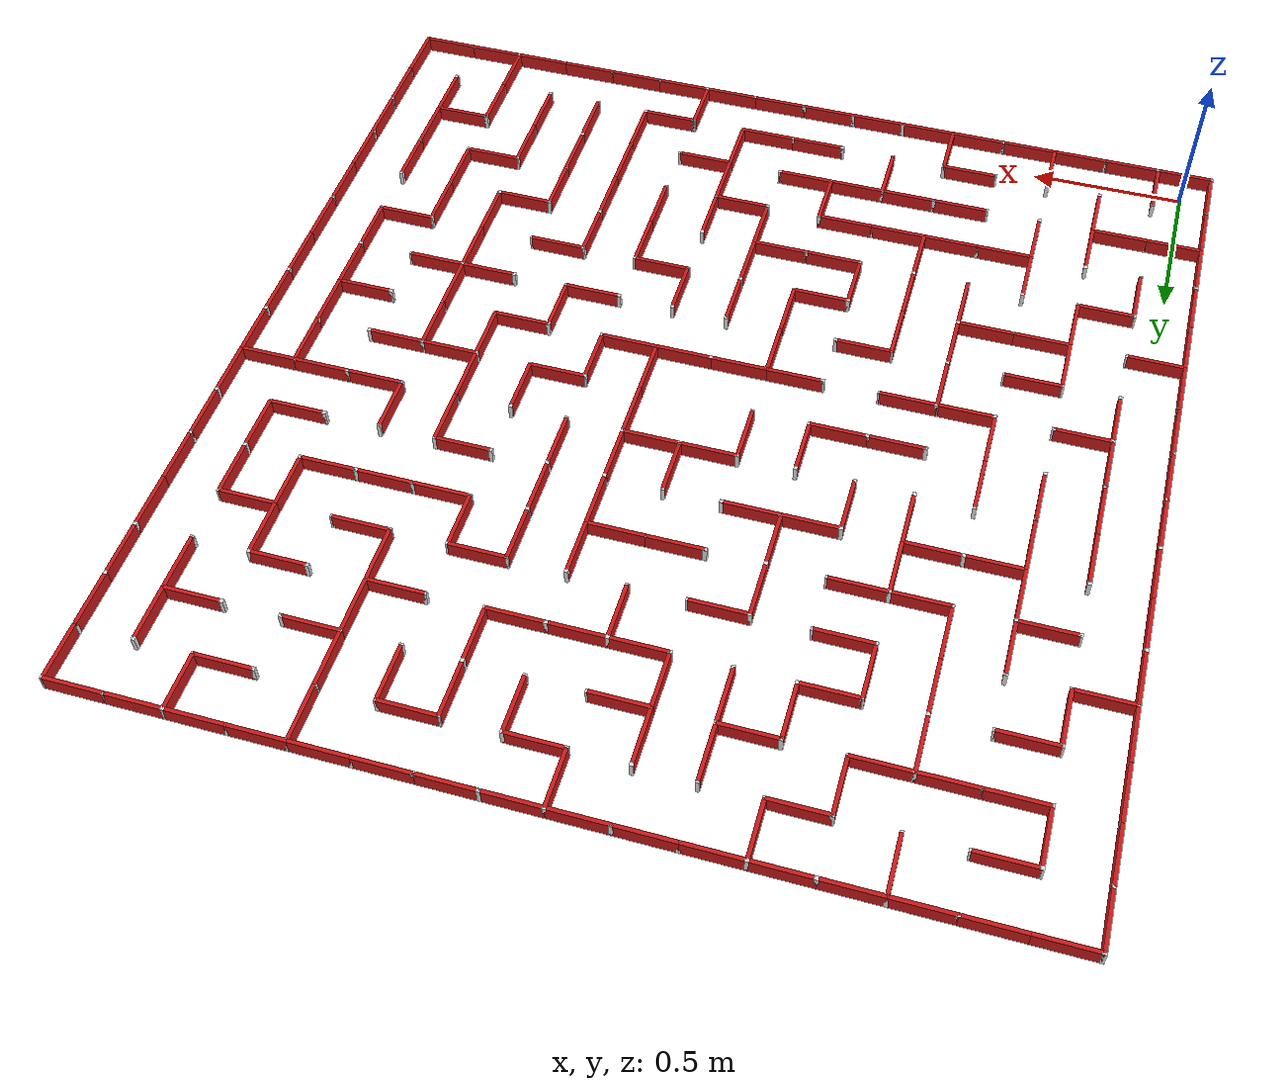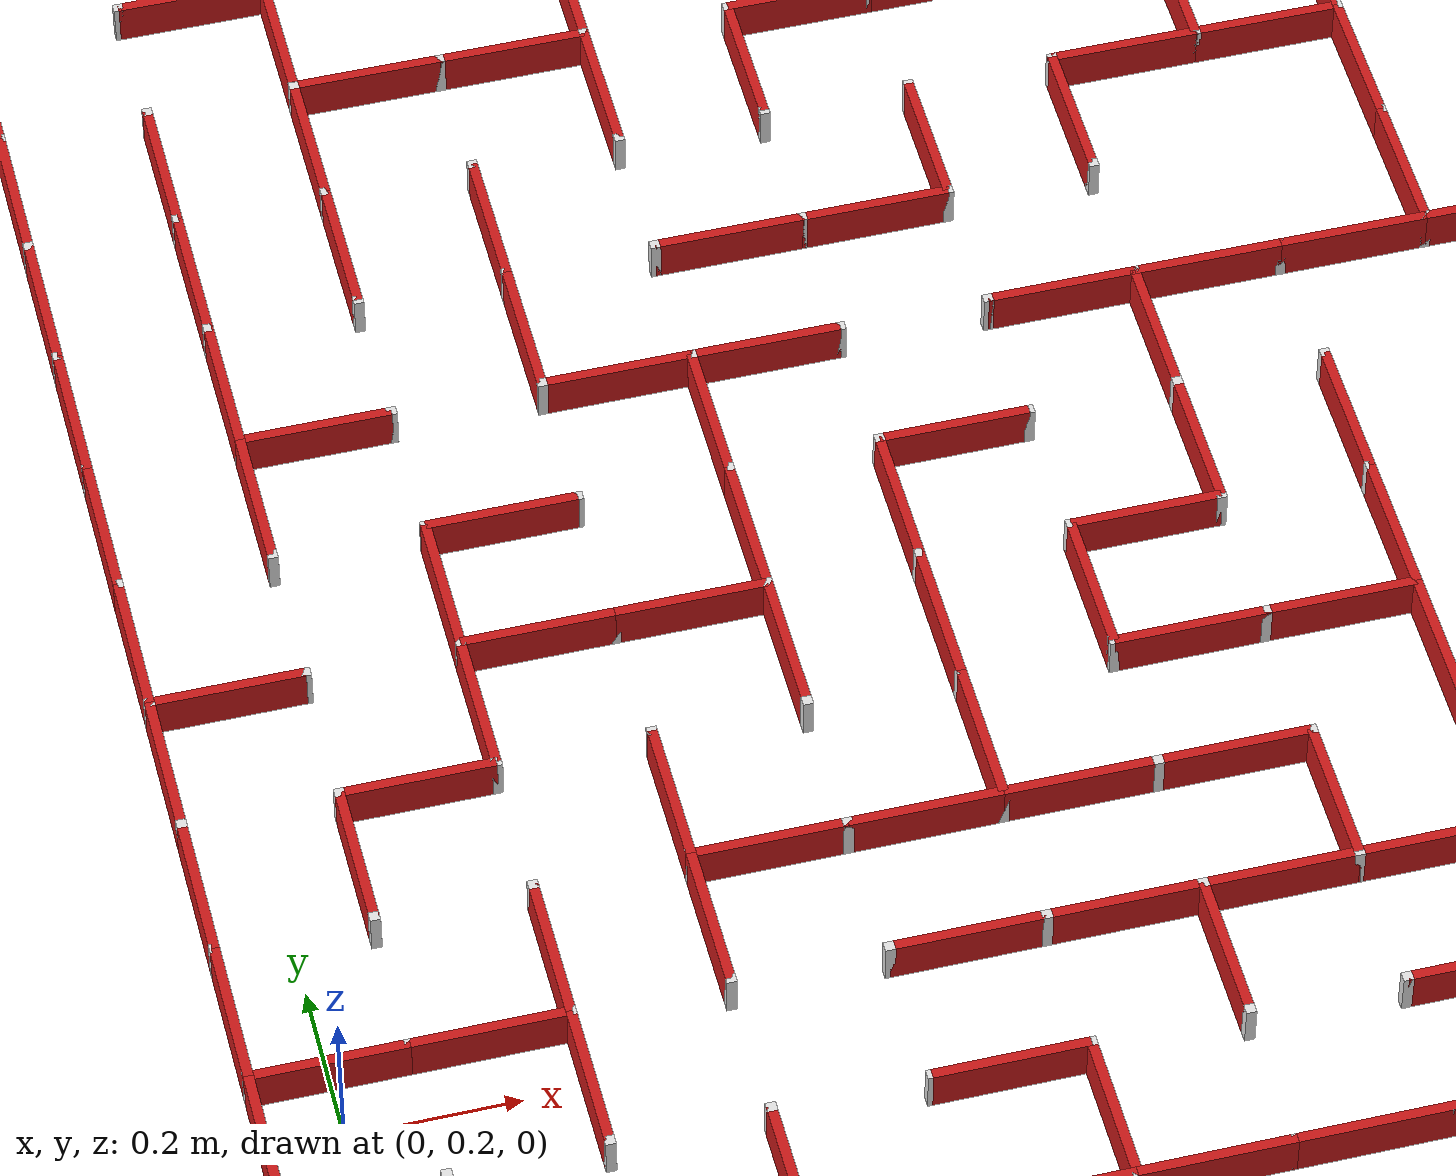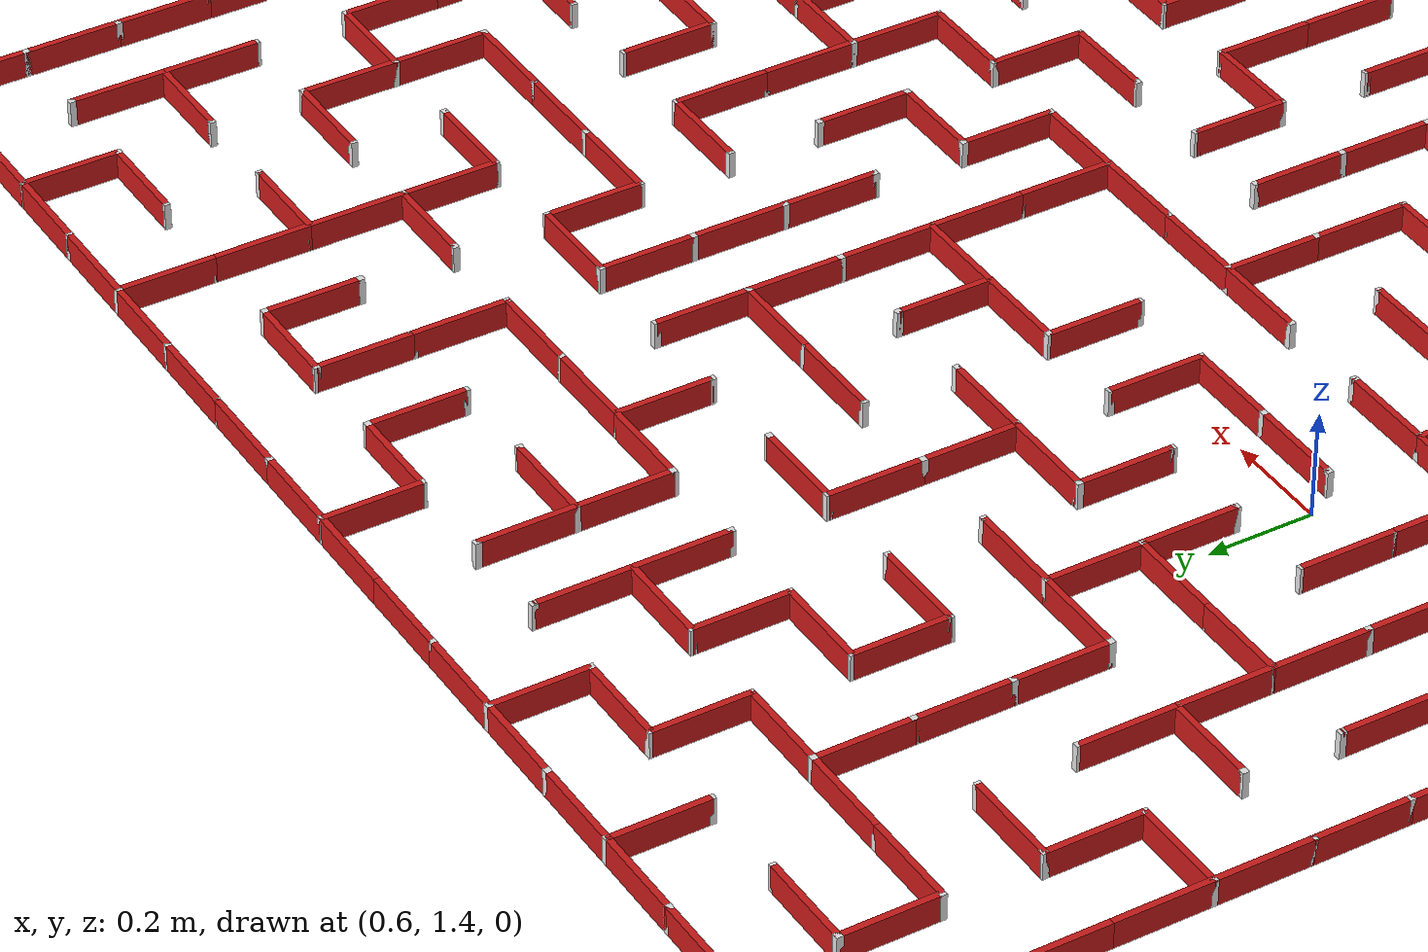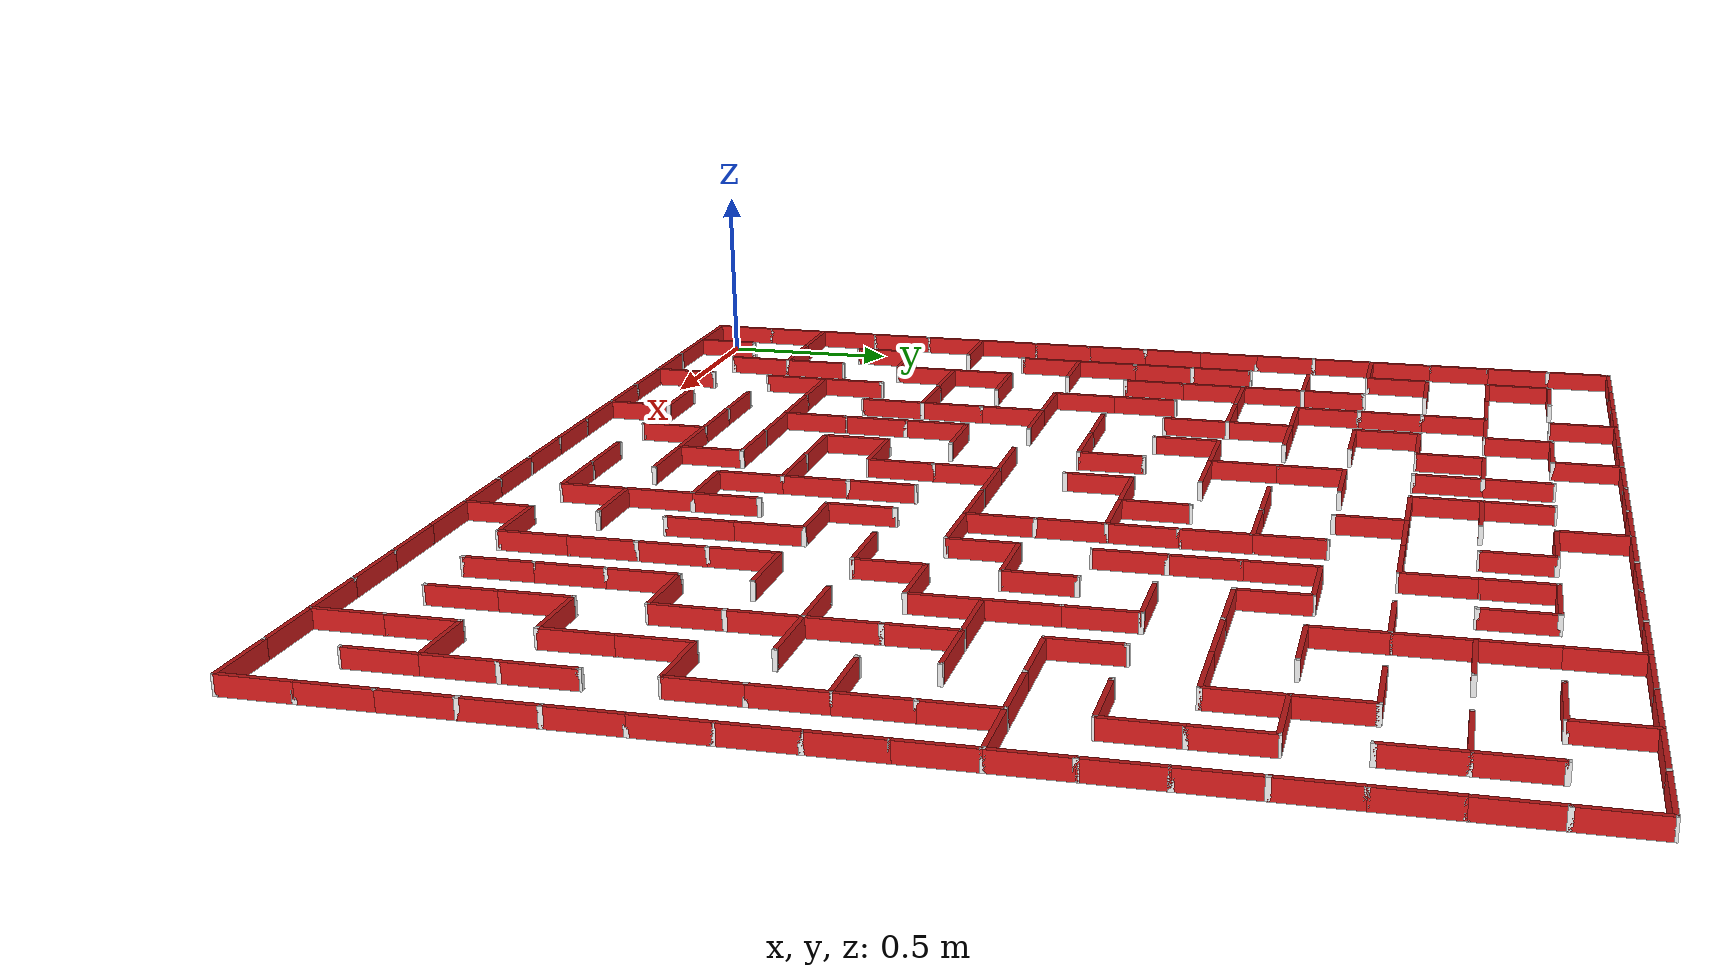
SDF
<?xml version="1.0"?>
<sdf version="1.9">
  <model name="maze">
    <static>true</static>
    <link name="walls">
      <collision name="c0"><pose>0.0900 0.0000 0.0250 0 0 0</pose>
        <geometry><box><size>0.0120 0.1800 0.0500</size></box></geometry></collision>
      <visual name="v0"><pose>0.0900 0.0000 0.0250 0 0 0</pose>
        <geometry><box><size>0.0120 0.1800 0.0500</size></box></geometry>
        <material><ambient>0.8 0.1 0.1 1</ambient><diffuse>0.8 0.1 0.1 1</diffuse></material></visual>
      <collision name="c1"><pose>0.0000 0.2700 0.0250 0 0 0</pose>
        <geometry><box><size>0.1800 0.0120 0.0500</size></box></geometry></collision>
      <visual name="v1"><pose>0.0000 0.2700 0.0250 0 0 0</pose>
        <geometry><box><size>0.1800 0.0120 0.0500</size></box></geometry>
        <material><ambient>0.8 0.1 0.1 1</ambient><diffuse>0.8 0.1 0.1 1</diffuse></material></visual>
      <collision name="c2"><pose>0.0900 0.5400 0.0250 0 0 0</pose>
        <geometry><box><size>0.0120 0.1800 0.0500</size></box></geometry></collision>
      <visual name="v2"><pose>0.0900 0.5400 0.0250 0 0 0</pose>
        <geometry><box><size>0.0120 0.1800 0.0500</size></box></geometry>
        <material><ambient>0.8 0.1 0.1 1</ambient><diffuse>0.8 0.1 0.1 1</diffuse></material></visual>
      <collision name="c3"><pose>0.0000 0.8100 0.0250 0 0 0</pose>
        <geometry><box><size>0.1800 0.0120 0.0500</size></box></geometry></collision>
      <visual name="v3"><pose>0.0000 0.8100 0.0250 0 0 0</pose>
        <geometry><box><size>0.1800 0.0120 0.0500</size></box></geometry>
        <material><ambient>0.8 0.1 0.1 1</ambient><diffuse>0.8 0.1 0.1 1</diffuse></material></visual>
      <collision name="c4"><pose>0.0900 1.0800 0.0250 0 0 0</pose>
        <geometry><box><size>0.0120 0.1800 0.0500</size></box></geometry></collision>
      <visual name="v4"><pose>0.0900 1.0800 0.0250 0 0 0</pose>
        <geometry><box><size>0.0120 0.1800 0.0500</size></box></geometry>
        <material><ambient>0.8 0.1 0.1 1</ambient><diffuse>0.8 0.1 0.1 1</diffuse></material></visual>
      <collision name="c5"><pose>0.0900 1.2600 0.0250 0 0 0</pose>
        <geometry><box><size>0.0120 0.1800 0.0500</size></box></geometry></collision>
      <visual name="v5"><pose>0.0900 1.2600 0.0250 0 0 0</pose>
        <geometry><box><size>0.0120 0.1800 0.0500</size></box></geometry>
        <material><ambient>0.8 0.1 0.1 1</ambient><diffuse>0.8 0.1 0.1 1</diffuse></material></visual>
      <collision name="c6"><pose>0.0900 1.4400 0.0250 0 0 0</pose>
        <geometry><box><size>0.0120 0.1800 0.0500</size></box></geometry></collision>
      <visual name="v6"><pose>0.0900 1.4400 0.0250 0 0 0</pose>
        <geometry><box><size>0.0120 0.1800 0.0500</size></box></geometry>
        <material><ambient>0.8 0.1 0.1 1</ambient><diffuse>0.8 0.1 0.1 1</diffuse></material></visual>
      <collision name="c7"><pose>0.0900 1.6200 0.0250 0 0 0</pose>
        <geometry><box><size>0.0120 0.1800 0.0500</size></box></geometry></collision>
      <visual name="v7"><pose>0.0900 1.6200 0.0250 0 0 0</pose>
        <geometry><box><size>0.0120 0.1800 0.0500</size></box></geometry>
        <material><ambient>0.8 0.1 0.1 1</ambient><diffuse>0.8 0.1 0.1 1</diffuse></material></visual>
      <collision name="c8"><pose>0.0000 2.0700 0.0250 0 0 0</pose>
        <geometry><box><size>0.1800 0.0120 0.0500</size></box></geometry></collision>
      <visual name="v8"><pose>0.0000 2.0700 0.0250 0 0 0</pose>
        <geometry><box><size>0.1800 0.0120 0.0500</size></box></geometry>
        <material><ambient>0.8 0.1 0.1 1</ambient><diffuse>0.8 0.1 0.1 1</diffuse></material></visual>
      <collision name="c9"><pose>0.0900 2.1600 0.0250 0 0 0</pose>
        <geometry><box><size>0.0120 0.1800 0.0500</size></box></geometry></collision>
      <visual name="v9"><pose>0.0900 2.1600 0.0250 0 0 0</pose>
        <geometry><box><size>0.0120 0.1800 0.0500</size></box></geometry>
        <material><ambient>0.8 0.1 0.1 1</ambient><diffuse>0.8 0.1 0.1 1</diffuse></material></visual>
      <collision name="c10"><pose>0.0900 2.5200 0.0250 0 0 0</pose>
        <geometry><box><size>0.0120 0.1800 0.0500</size></box></geometry></collision>
      <visual name="v10"><pose>0.0900 2.5200 0.0250 0 0 0</pose>
        <geometry><box><size>0.0120 0.1800 0.0500</size></box></geometry>
        <material><ambient>0.8 0.1 0.1 1</ambient><diffuse>0.8 0.1 0.1 1</diffuse></material></visual>
      <collision name="c11"><pose>0.0000 2.7900 0.0250 0 0 0</pose>
        <geometry><box><size>0.1800 0.0120 0.0500</size></box></geometry></collision>
      <visual name="v11"><pose>0.0000 2.7900 0.0250 0 0 0</pose>
        <geometry><box><size>0.1800 0.0120 0.0500</size></box></geometry>
        <material><ambient>0.8 0.1 0.1 1</ambient><diffuse>0.8 0.1 0.1 1</diffuse></material></visual>
      <collision name="c12"><pose>0.2700 0.1800 0.0250 0 0 0</pose>
        <geometry><box><size>0.0120 0.1800 0.0500</size></box></geometry></collision>
      <visual name="v12"><pose>0.2700 0.1800 0.0250 0 0 0</pose>
        <geometry><box><size>0.0120 0.1800 0.0500</size></box></geometry>
        <material><ambient>0.8 0.1 0.1 1</ambient><diffuse>0.8 0.1 0.1 1</diffuse></material></visual>
      <collision name="c13"><pose>0.1800 0.2700 0.0250 0 0 0</pose>
        <geometry><box><size>0.1800 0.0120 0.0500</size></box></geometry></collision>
      <visual name="v13"><pose>0.1800 0.2700 0.0250 0 0 0</pose>
        <geometry><box><size>0.1800 0.0120 0.0500</size></box></geometry>
        <material><ambient>0.8 0.1 0.1 1</ambient><diffuse>0.8 0.1 0.1 1</diffuse></material></visual>
      <collision name="c14"><pose>0.2700 0.3600 0.0250 0 0 0</pose>
        <geometry><box><size>0.0120 0.1800 0.0500</size></box></geometry></collision>
      <visual name="v14"><pose>0.2700 0.3600 0.0250 0 0 0</pose>
        <geometry><box><size>0.0120 0.1800 0.0500</size></box></geometry>
        <material><ambient>0.8 0.1 0.1 1</ambient><diffuse>0.8 0.1 0.1 1</diffuse></material></visual>
      <collision name="c15"><pose>0.1800 0.6300 0.0250 0 0 0</pose>
        <geometry><box><size>0.1800 0.0120 0.0500</size></box></geometry></collision>
      <visual name="v15"><pose>0.1800 0.6300 0.0250 0 0 0</pose>
        <geometry><box><size>0.1800 0.0120 0.0500</size></box></geometry>
        <material><ambient>0.8 0.1 0.1 1</ambient><diffuse>0.8 0.1 0.1 1</diffuse></material></visual>
      <collision name="c16"><pose>0.2700 0.7200 0.0250 0 0 0</pose>
        <geometry><box><size>0.0120 0.1800 0.0500</size></box></geometry></collision>
      <visual name="v16"><pose>0.2700 0.7200 0.0250 0 0 0</pose>
        <geometry><box><size>0.0120 0.1800 0.0500</size></box></geometry>
        <material><ambient>0.8 0.1 0.1 1</ambient><diffuse>0.8 0.1 0.1 1</diffuse></material></visual>
      <collision name="c17"><pose>0.2700 0.9000 0.0250 0 0 0</pose>
        <geometry><box><size>0.0120 0.1800 0.0500</size></box></geometry></collision>
      <visual name="v17"><pose>0.2700 0.9000 0.0250 0 0 0</pose>
        <geometry><box><size>0.0120 0.1800 0.0500</size></box></geometry>
        <material><ambient>0.8 0.1 0.1 1</ambient><diffuse>0.8 0.1 0.1 1</diffuse></material></visual>
      <collision name="c18"><pose>0.1800 1.1700 0.0250 0 0 0</pose>
        <geometry><box><size>0.1800 0.0120 0.0500</size></box></geometry></collision>
      <visual name="v18"><pose>0.1800 1.1700 0.0250 0 0 0</pose>
        <geometry><box><size>0.1800 0.0120 0.0500</size></box></geometry>
        <material><ambient>0.8 0.1 0.1 1</ambient><diffuse>0.8 0.1 0.1 1</diffuse></material></visual>
      <collision name="c19"><pose>0.2700 1.4400 0.0250 0 0 0</pose>
        <geometry><box><size>0.0120 0.1800 0.0500</size></box></geometry></collision>
      <visual name="v19"><pose>0.2700 1.4400 0.0250 0 0 0</pose>
        <geometry><box><size>0.0120 0.1800 0.0500</size></box></geometry>
        <material><ambient>0.8 0.1 0.1 1</ambient><diffuse>0.8 0.1 0.1 1</diffuse></material></visual>
      <collision name="c20"><pose>0.2700 1.6200 0.0250 0 0 0</pose>
        <geometry><box><size>0.0120 0.1800 0.0500</size></box></geometry></collision>
      <visual name="v20"><pose>0.2700 1.6200 0.0250 0 0 0</pose>
        <geometry><box><size>0.0120 0.1800 0.0500</size></box></geometry>
        <material><ambient>0.8 0.1 0.1 1</ambient><diffuse>0.8 0.1 0.1 1</diffuse></material></visual>
      <collision name="c21"><pose>0.2700 1.8000 0.0250 0 0 0</pose>
        <geometry><box><size>0.0120 0.1800 0.0500</size></box></geometry></collision>
      <visual name="v21"><pose>0.2700 1.8000 0.0250 0 0 0</pose>
        <geometry><box><size>0.0120 0.1800 0.0500</size></box></geometry>
        <material><ambient>0.8 0.1 0.1 1</ambient><diffuse>0.8 0.1 0.1 1</diffuse></material></visual>
      <collision name="c22"><pose>0.1800 1.8900 0.0250 0 0 0</pose>
        <geometry><box><size>0.1800 0.0120 0.0500</size></box></geometry></collision>
      <visual name="v22"><pose>0.1800 1.8900 0.0250 0 0 0</pose>
        <geometry><box><size>0.1800 0.0120 0.0500</size></box></geometry>
        <material><ambient>0.8 0.1 0.1 1</ambient><diffuse>0.8 0.1 0.1 1</diffuse></material></visual>
      <collision name="c23"><pose>0.2700 1.9800 0.0250 0 0 0</pose>
        <geometry><box><size>0.0120 0.1800 0.0500</size></box></geometry></collision>
      <visual name="v23"><pose>0.2700 1.9800 0.0250 0 0 0</pose>
        <geometry><box><size>0.0120 0.1800 0.0500</size></box></geometry>
        <material><ambient>0.8 0.1 0.1 1</ambient><diffuse>0.8 0.1 0.1 1</diffuse></material></visual>
      <collision name="c24"><pose>0.1800 2.2500 0.0250 0 0 0</pose>
        <geometry><box><size>0.1800 0.0120 0.0500</size></box></geometry></collision>
      <visual name="v24"><pose>0.1800 2.2500 0.0250 0 0 0</pose>
        <geometry><box><size>0.1800 0.0120 0.0500</size></box></geometry>
        <material><ambient>0.8 0.1 0.1 1</ambient><diffuse>0.8 0.1 0.1 1</diffuse></material></visual>
      <collision name="c25"><pose>0.1800 2.4300 0.0250 0 0 0</pose>
        <geometry><box><size>0.1800 0.0120 0.0500</size></box></geometry></collision>
      <visual name="v25"><pose>0.1800 2.4300 0.0250 0 0 0</pose>
        <geometry><box><size>0.1800 0.0120 0.0500</size></box></geometry>
        <material><ambient>0.8 0.1 0.1 1</ambient><diffuse>0.8 0.1 0.1 1</diffuse></material></visual>
      <collision name="c26"><pose>0.1800 2.6100 0.0250 0 0 0</pose>
        <geometry><box><size>0.1800 0.0120 0.0500</size></box></geometry></collision>
      <visual name="v26"><pose>0.1800 2.6100 0.0250 0 0 0</pose>
        <geometry><box><size>0.1800 0.0120 0.0500</size></box></geometry>
        <material><ambient>0.8 0.1 0.1 1</ambient><diffuse>0.8 0.1 0.1 1</diffuse></material></visual>
      <collision name="c27"><pose>0.1800 2.7900 0.0250 0 0 0</pose>
        <geometry><box><size>0.1800 0.0120 0.0500</size></box></geometry></collision>
      <visual name="v27"><pose>0.1800 2.7900 0.0250 0 0 0</pose>
        <geometry><box><size>0.1800 0.0120 0.0500</size></box></geometry>
        <material><ambient>0.8 0.1 0.1 1</ambient><diffuse>0.8 0.1 0.1 1</diffuse></material></visual>
      <collision name="c28"><pose>0.4500 0.0000 0.0250 0 0 0</pose>
        <geometry><box><size>0.0120 0.1800 0.0500</size></box></geometry></collision>
      <visual name="v28"><pose>0.4500 0.0000 0.0250 0 0 0</pose>
        <geometry><box><size>0.0120 0.1800 0.0500</size></box></geometry>
        <material><ambient>0.8 0.1 0.1 1</ambient><diffuse>0.8 0.1 0.1 1</diffuse></material></visual>
      <collision name="c29"><pose>0.4500 0.3600 0.0250 0 0 0</pose>
        <geometry><box><size>0.0120 0.1800 0.0500</size></box></geometry></collision>
      <visual name="v29"><pose>0.4500 0.3600 0.0250 0 0 0</pose>
        <geometry><box><size>0.0120 0.1800 0.0500</size></box></geometry>
        <material><ambient>0.8 0.1 0.1 1</ambient><diffuse>0.8 0.1 0.1 1</diffuse></material></visual>
      <collision name="c30"><pose>0.4500 0.5400 0.0250 0 0 0</pose>
        <geometry><box><size>0.0120 0.1800 0.0500</size></box></geometry></collision>
      <visual name="v30"><pose>0.4500 0.5400 0.0250 0 0 0</pose>
        <geometry><box><size>0.0120 0.1800 0.0500</size></box></geometry>
        <material><ambient>0.8 0.1 0.1 1</ambient><diffuse>0.8 0.1 0.1 1</diffuse></material></visual>
      <collision name="c31"><pose>0.3600 0.8100 0.0250 0 0 0</pose>
        <geometry><box><size>0.1800 0.0120 0.0500</size></box></geometry></collision>
      <visual name="v31"><pose>0.3600 0.8100 0.0250 0 0 0</pose>
        <geometry><box><size>0.1800 0.0120 0.0500</size></box></geometry>
        <material><ambient>0.8 0.1 0.1 1</ambient><diffuse>0.8 0.1 0.1 1</diffuse></material></visual>
      <collision name="c32"><pose>0.3600 0.9900 0.0250 0 0 0</pose>
        <geometry><box><size>0.1800 0.0120 0.0500</size></box></geometry></collision>
      <visual name="v32"><pose>0.3600 0.9900 0.0250 0 0 0</pose>
        <geometry><box><size>0.1800 0.0120 0.0500</size></box></geometry>
        <material><ambient>0.8 0.1 0.1 1</ambient><diffuse>0.8 0.1 0.1 1</diffuse></material></visual>
      <collision name="c33"><pose>0.4500 1.2600 0.0250 0 0 0</pose>
        <geometry><box><size>0.0120 0.1800 0.0500</size></box></geometry></collision>
      <visual name="v33"><pose>0.4500 1.2600 0.0250 0 0 0</pose>
        <geometry><box><size>0.0120 0.1800 0.0500</size></box></geometry>
        <material><ambient>0.8 0.1 0.1 1</ambient><diffuse>0.8 0.1 0.1 1</diffuse></material></visual>
      <collision name="c34"><pose>0.4500 1.4400 0.0250 0 0 0</pose>
        <geometry><box><size>0.0120 0.1800 0.0500</size></box></geometry></collision>
      <visual name="v34"><pose>0.4500 1.4400 0.0250 0 0 0</pose>
        <geometry><box><size>0.0120 0.1800 0.0500</size></box></geometry>
        <material><ambient>0.8 0.1 0.1 1</ambient><diffuse>0.8 0.1 0.1 1</diffuse></material></visual>
      <collision name="c35"><pose>0.3600 1.7100 0.0250 0 0 0</pose>
        <geometry><box><size>0.1800 0.0120 0.0500</size></box></geometry></collision>
      <visual name="v35"><pose>0.3600 1.7100 0.0250 0 0 0</pose>
        <geometry><box><size>0.1800 0.0120 0.0500</size></box></geometry>
        <material><ambient>0.8 0.1 0.1 1</ambient><diffuse>0.8 0.1 0.1 1</diffuse></material></visual>
      <collision name="c36"><pose>0.4500 1.9800 0.0250 0 0 0</pose>
        <geometry><box><size>0.0120 0.1800 0.0500</size></box></geometry></collision>
      <visual name="v36"><pose>0.4500 1.9800 0.0250 0 0 0</pose>
        <geometry><box><size>0.0120 0.1800 0.0500</size></box></geometry>
        <material><ambient>0.8 0.1 0.1 1</ambient><diffuse>0.8 0.1 0.1 1</diffuse></material></visual>
      <collision name="c37"><pose>0.4500 2.1600 0.0250 0 0 0</pose>
        <geometry><box><size>0.0120 0.1800 0.0500</size></box></geometry></collision>
      <visual name="v37"><pose>0.4500 2.1600 0.0250 0 0 0</pose>
        <geometry><box><size>0.0120 0.1800 0.0500</size></box></geometry>
        <material><ambient>0.8 0.1 0.1 1</ambient><diffuse>0.8 0.1 0.1 1</diffuse></material></visual>
      <collision name="c38"><pose>0.4500 2.3400 0.0250 0 0 0</pose>
        <geometry><box><size>0.0120 0.1800 0.0500</size></box></geometry></collision>
      <visual name="v38"><pose>0.4500 2.3400 0.0250 0 0 0</pose>
        <geometry><box><size>0.0120 0.1800 0.0500</size></box></geometry>
        <material><ambient>0.8 0.1 0.1 1</ambient><diffuse>0.8 0.1 0.1 1</diffuse></material></visual>
      <collision name="c39"><pose>0.3600 2.4300 0.0250 0 0 0</pose>
        <geometry><box><size>0.1800 0.0120 0.0500</size></box></geometry></collision>
      <visual name="v39"><pose>0.3600 2.4300 0.0250 0 0 0</pose>
        <geometry><box><size>0.1800 0.0120 0.0500</size></box></geometry>
        <material><ambient>0.8 0.1 0.1 1</ambient><diffuse>0.8 0.1 0.1 1</diffuse></material></visual>
      <collision name="c40"><pose>0.4500 2.7000 0.0250 0 0 0</pose>
        <geometry><box><size>0.0120 0.1800 0.0500</size></box></geometry></collision>
      <visual name="v40"><pose>0.4500 2.7000 0.0250 0 0 0</pose>
        <geometry><box><size>0.0120 0.1800 0.0500</size></box></geometry>
        <material><ambient>0.8 0.1 0.1 1</ambient><diffuse>0.8 0.1 0.1 1</diffuse></material></visual>
      <collision name="c41"><pose>0.3600 2.7900 0.0250 0 0 0</pose>
        <geometry><box><size>0.1800 0.0120 0.0500</size></box></geometry></collision>
      <visual name="v41"><pose>0.3600 2.7900 0.0250 0 0 0</pose>
        <geometry><box><size>0.1800 0.0120 0.0500</size></box></geometry>
        <material><ambient>0.8 0.1 0.1 1</ambient><diffuse>0.8 0.1 0.1 1</diffuse></material></visual>
      <collision name="c42"><pose>0.5400 0.4500 0.0250 0 0 0</pose>
        <geometry><box><size>0.1800 0.0120 0.0500</size></box></geometry></collision>
      <visual name="v42"><pose>0.5400 0.4500 0.0250 0 0 0</pose>
        <geometry><box><size>0.1800 0.0120 0.0500</size></box></geometry>
        <material><ambient>0.8 0.1 0.1 1</ambient><diffuse>0.8 0.1 0.1 1</diffuse></material></visual>
      <collision name="c43"><pose>0.6300 0.7200 0.0250 0 0 0</pose>
        <geometry><box><size>0.0120 0.1800 0.0500</size></box></geometry></collision>
      <visual name="v43"><pose>0.6300 0.7200 0.0250 0 0 0</pose>
        <geometry><box><size>0.0120 0.1800 0.0500</size></box></geometry>
        <material><ambient>0.8 0.1 0.1 1</ambient><diffuse>0.8 0.1 0.1 1</diffuse></material></visual>
      <collision name="c44"><pose>0.5400 0.8100 0.0250 0 0 0</pose>
        <geometry><box><size>0.1800 0.0120 0.0500</size></box></geometry></collision>
      <visual name="v44"><pose>0.5400 0.8100 0.0250 0 0 0</pose>
        <geometry><box><size>0.1800 0.0120 0.0500</size></box></geometry>
        <material><ambient>0.8 0.1 0.1 1</ambient><diffuse>0.8 0.1 0.1 1</diffuse></material></visual>
      <collision name="c45"><pose>0.6300 0.9000 0.0250 0 0 0</pose>
        <geometry><box><size>0.0120 0.1800 0.0500</size></box></geometry></collision>
      <visual name="v45"><pose>0.6300 0.9000 0.0250 0 0 0</pose>
        <geometry><box><size>0.0120 0.1800 0.0500</size></box></geometry>
        <material><ambient>0.8 0.1 0.1 1</ambient><diffuse>0.8 0.1 0.1 1</diffuse></material></visual>
      <collision name="c46"><pose>0.6300 1.0800 0.0250 0 0 0</pose>
        <geometry><box><size>0.0120 0.1800 0.0500</size></box></geometry></collision>
      <visual name="v46"><pose>0.6300 1.0800 0.0250 0 0 0</pose>
        <geometry><box><size>0.0120 0.1800 0.0500</size></box></geometry>
        <material><ambient>0.8 0.1 0.1 1</ambient><diffuse>0.8 0.1 0.1 1</diffuse></material></visual>
      <collision name="c47"><pose>0.5400 1.1700 0.0250 0 0 0</pose>
        <geometry><box><size>0.1800 0.0120 0.0500</size></box></geometry></collision>
      <visual name="v47"><pose>0.5400 1.1700 0.0250 0 0 0</pose>
        <geometry><box><size>0.1800 0.0120 0.0500</size></box></geometry>
        <material><ambient>0.8 0.1 0.1 1</ambient><diffuse>0.8 0.1 0.1 1</diffuse></material></visual>
      <collision name="c48"><pose>0.6300 1.6200 0.0250 0 0 0</pose>
        <geometry><box><size>0.0120 0.1800 0.0500</size></box></geometry></collision>
      <visual name="v48"><pose>0.6300 1.6200 0.0250 0 0 0</pose>
        <geometry><box><size>0.0120 0.1800 0.0500</size></box></geometry>
        <material><ambient>0.8 0.1 0.1 1</ambient><diffuse>0.8 0.1 0.1 1</diffuse></material></visual>
      <collision name="c49"><pose>0.5400 1.7100 0.0250 0 0 0</pose>
        <geometry><box><size>0.1800 0.0120 0.0500</size></box></geometry></collision>
      <visual name="v49"><pose>0.5400 1.7100 0.0250 0 0 0</pose>
        <geometry><box><size>0.1800 0.0120 0.0500</size></box></geometry>
        <material><ambient>0.8 0.1 0.1 1</ambient><diffuse>0.8 0.1 0.1 1</diffuse></material></visual>
      <collision name="c50"><pose>0.6300 1.8000 0.0250 0 0 0</pose>
        <geometry><box><size>0.0120 0.1800 0.0500</size></box></geometry></collision>
      <visual name="v50"><pose>0.6300 1.8000 0.0250 0 0 0</pose>
        <geometry><box><size>0.0120 0.1800 0.0500</size></box></geometry>
        <material><ambient>0.8 0.1 0.1 1</ambient><diffuse>0.8 0.1 0.1 1</diffuse></material></visual>
      <collision name="c51"><pose>0.5400 1.8900 0.0250 0 0 0</pose>
        <geometry><box><size>0.1800 0.0120 0.0500</size></box></geometry></collision>
      <visual name="v51"><pose>0.5400 1.8900 0.0250 0 0 0</pose>
        <geometry><box><size>0.1800 0.0120 0.0500</size></box></geometry>
        <material><ambient>0.8 0.1 0.1 1</ambient><diffuse>0.8 0.1 0.1 1</diffuse></material></visual>
      <collision name="c52"><pose>0.6300 2.1600 0.0250 0 0 0</pose>
        <geometry><box><size>0.0120 0.1800 0.0500</size></box></geometry></collision>
      <visual name="v52"><pose>0.6300 2.1600 0.0250 0 0 0</pose>
        <geometry><box><size>0.0120 0.1800 0.0500</size></box></geometry>
        <material><ambient>0.8 0.1 0.1 1</ambient><diffuse>0.8 0.1 0.1 1</diffuse></material></visual>
      <collision name="c53"><pose>0.5400 2.4300 0.0250 0 0 0</pose>
        <geometry><box><size>0.1800 0.0120 0.0500</size></box></geometry></collision>
      <visual name="v53"><pose>0.5400 2.4300 0.0250 0 0 0</pose>
        <geometry><box><size>0.1800 0.0120 0.0500</size></box></geometry>
        <material><ambient>0.8 0.1 0.1 1</ambient><diffuse>0.8 0.1 0.1 1</diffuse></material></visual>
      <collision name="c54"><pose>0.6300 2.5200 0.0250 0 0 0</pose>
        <geometry><box><size>0.0120 0.1800 0.0500</size></box></geometry></collision>
      <visual name="v54"><pose>0.6300 2.5200 0.0250 0 0 0</pose>
        <geometry><box><size>0.0120 0.1800 0.0500</size></box></geometry>
        <material><ambient>0.8 0.1 0.1 1</ambient><diffuse>0.8 0.1 0.1 1</diffuse></material></visual>
      <collision name="c55"><pose>0.5400 2.7900 0.0250 0 0 0</pose>
        <geometry><box><size>0.1800 0.0120 0.0500</size></box></geometry></collision>
      <visual name="v55"><pose>0.5400 2.7900 0.0250 0 0 0</pose>
        <geometry><box><size>0.1800 0.0120 0.0500</size></box></geometry>
        <material><ambient>0.8 0.1 0.1 1</ambient><diffuse>0.8 0.1 0.1 1</diffuse></material></visual>
      <collision name="c56"><pose>0.8100 0.0000 0.0250 0 0 0</pose>
        <geometry><box><size>0.0120 0.1800 0.0500</size></box></geometry></collision>
      <visual name="v56"><pose>0.8100 0.0000 0.0250 0 0 0</pose>
        <geometry><box><size>0.0120 0.1800 0.0500</size></box></geometry>
        <material><ambient>0.8 0.1 0.1 1</ambient><diffuse>0.8 0.1 0.1 1</diffuse></material></visual>
      <collision name="c57"><pose>0.7200 0.0900 0.0250 0 0 0</pose>
        <geometry><box><size>0.1800 0.0120 0.0500</size></box></geometry></collision>
      <visual name="v57"><pose>0.7200 0.0900 0.0250 0 0 0</pose>
        <geometry><box><size>0.1800 0.0120 0.0500</size></box></geometry>
        <material><ambient>0.8 0.1 0.1 1</ambient><diffuse>0.8 0.1 0.1 1</diffuse></material></visual>
      <collision name="c58"><pose>0.7200 0.2700 0.0250 0 0 0</pose>
        <geometry><box><size>0.1800 0.0120 0.0500</size></box></geometry></collision>
      <visual name="v58"><pose>0.7200 0.2700 0.0250 0 0 0</pose>
        <geometry><box><size>0.1800 0.0120 0.0500</size></box></geometry>
        <material><ambient>0.8 0.1 0.1 1</ambient><diffuse>0.8 0.1 0.1 1</diffuse></material></visual>
      <collision name="c59"><pose>0.7200 0.4500 0.0250 0 0 0</pose>
        <geometry><box><size>0.1800 0.0120 0.0500</size></box></geometry></collision>
      <visual name="v59"><pose>0.7200 0.4500 0.0250 0 0 0</pose>
        <geometry><box><size>0.1800 0.0120 0.0500</size></box></geometry>
        <material><ambient>0.8 0.1 0.1 1</ambient><diffuse>0.8 0.1 0.1 1</diffuse></material></visual>
      <collision name="c60"><pose>0.8100 0.5400 0.0250 0 0 0</pose>
        <geometry><box><size>0.0120 0.1800 0.0500</size></box></geometry></collision>
      <visual name="v60"><pose>0.8100 0.5400 0.0250 0 0 0</pose>
        <geometry><box><size>0.0120 0.1800 0.0500</size></box></geometry>
        <material><ambient>0.8 0.1 0.1 1</ambient><diffuse>0.8 0.1 0.1 1</diffuse></material></visual>
      <collision name="c61"><pose>0.8100 0.7200 0.0250 0 0 0</pose>
        <geometry><box><size>0.0120 0.1800 0.0500</size></box></geometry></collision>
      <visual name="v61"><pose>0.8100 0.7200 0.0250 0 0 0</pose>
        <geometry><box><size>0.0120 0.1800 0.0500</size></box></geometry>
        <material><ambient>0.8 0.1 0.1 1</ambient><diffuse>0.8 0.1 0.1 1</diffuse></material></visual>
      <collision name="c62"><pose>0.8100 0.9000 0.0250 0 0 0</pose>
        <geometry><box><size>0.0120 0.1800 0.0500</size></box></geometry></collision>
      <visual name="v62"><pose>0.8100 0.9000 0.0250 0 0 0</pose>
        <geometry><box><size>0.0120 0.1800 0.0500</size></box></geometry>
        <material><ambient>0.8 0.1 0.1 1</ambient><diffuse>0.8 0.1 0.1 1</diffuse></material></visual>
      <collision name="c63"><pose>0.7200 1.1700 0.0250 0 0 0</pose>
        <geometry><box><size>0.1800 0.0120 0.0500</size></box></geometry></collision>
      <visual name="v63"><pose>0.7200 1.1700 0.0250 0 0 0</pose>
        <geometry><box><size>0.1800 0.0120 0.0500</size></box></geometry>
        <material><ambient>0.8 0.1 0.1 1</ambient><diffuse>0.8 0.1 0.1 1</diffuse></material></visual>
      <collision name="c64"><pose>0.7200 1.3500 0.0250 0 0 0</pose>
        <geometry><box><size>0.1800 0.0120 0.0500</size></box></geometry></collision>
      <visual name="v64"><pose>0.7200 1.3500 0.0250 0 0 0</pose>
        <geometry><box><size>0.1800 0.0120 0.0500</size></box></geometry>
        <material><ambient>0.8 0.1 0.1 1</ambient><diffuse>0.8 0.1 0.1 1</diffuse></material></visual>
      <collision name="c65"><pose>0.8100 1.6200 0.0250 0 0 0</pose>
        <geometry><box><size>0.0120 0.1800 0.0500</size></box></geometry></collision>
      <visual name="v65"><pose>0.8100 1.6200 0.0250 0 0 0</pose>
        <geometry><box><size>0.0120 0.1800 0.0500</size></box></geometry>
        <material><ambient>0.8 0.1 0.1 1</ambient><diffuse>0.8 0.1 0.1 1</diffuse></material></visual>
      <collision name="c66"><pose>0.7200 1.8900 0.0250 0 0 0</pose>
        <geometry><box><size>0.1800 0.0120 0.0500</size></box></geometry></collision>
      <visual name="v66"><pose>0.7200 1.8900 0.0250 0 0 0</pose>
        <geometry><box><size>0.1800 0.0120 0.0500</size></box></geometry>
        <material><ambient>0.8 0.1 0.1 1</ambient><diffuse>0.8 0.1 0.1 1</diffuse></material></visual>
      <collision name="c67"><pose>0.7200 2.0700 0.0250 0 0 0</pose>
        <geometry><box><size>0.1800 0.0120 0.0500</size></box></geometry></collision>
      <visual name="v67"><pose>0.7200 2.0700 0.0250 0 0 0</pose>
        <geometry><box><size>0.1800 0.0120 0.0500</size></box></geometry>
        <material><ambient>0.8 0.1 0.1 1</ambient><diffuse>0.8 0.1 0.1 1</diffuse></material></visual>
      <collision name="c68"><pose>0.7200 2.2500 0.0250 0 0 0</pose>
        <geometry><box><size>0.1800 0.0120 0.0500</size></box></geometry></collision>
      <visual name="v68"><pose>0.7200 2.2500 0.0250 0 0 0</pose>
        <geometry><box><size>0.1800 0.0120 0.0500</size></box></geometry>
        <material><ambient>0.8 0.1 0.1 1</ambient><diffuse>0.8 0.1 0.1 1</diffuse></material></visual>
      <collision name="c69"><pose>0.8100 2.3400 0.0250 0 0 0</pose>
        <geometry><box><size>0.0120 0.1800 0.0500</size></box></geometry></collision>
      <visual name="v69"><pose>0.8100 2.3400 0.0250 0 0 0</pose>
        <geometry><box><size>0.0120 0.1800 0.0500</size></box></geometry>
        <material><ambient>0.8 0.1 0.1 1</ambient><diffuse>0.8 0.1 0.1 1</diffuse></material></visual>
      <collision name="c70"><pose>0.7200 2.6100 0.0250 0 0 0</pose>
        <geometry><box><size>0.1800 0.0120 0.0500</size></box></geometry></collision>
      <visual name="v70"><pose>0.7200 2.6100 0.0250 0 0 0</pose>
        <geometry><box><size>0.1800 0.0120 0.0500</size></box></geometry>
        <material><ambient>0.8 0.1 0.1 1</ambient><diffuse>0.8 0.1 0.1 1</diffuse></material></visual>
      <collision name="c71"><pose>0.8100 2.7000 0.0250 0 0 0</pose>
        <geometry><box><size>0.0120 0.1800 0.0500</size></box></geometry></collision>
      <visual name="v71"><pose>0.8100 2.7000 0.0250 0 0 0</pose>
        <geometry><box><size>0.0120 0.1800 0.0500</size></box></geometry>
        <material><ambient>0.8 0.1 0.1 1</ambient><diffuse>0.8 0.1 0.1 1</diffuse></material></visual>
      <collision name="c72"><pose>0.7200 2.7900 0.0250 0 0 0</pose>
        <geometry><box><size>0.1800 0.0120 0.0500</size></box></geometry></collision>
      <visual name="v72"><pose>0.7200 2.7900 0.0250 0 0 0</pose>
        <geometry><box><size>0.1800 0.0120 0.0500</size></box></geometry>
        <material><ambient>0.8 0.1 0.1 1</ambient><diffuse>0.8 0.1 0.1 1</diffuse></material></visual>
      <collision name="c73"><pose>0.9900 0.1800 0.0250 0 0 0</pose>
        <geometry><box><size>0.0120 0.1800 0.0500</size></box></geometry></collision>
      <visual name="v73"><pose>0.9900 0.1800 0.0250 0 0 0</pose>
        <geometry><box><size>0.0120 0.1800 0.0500</size></box></geometry>
        <material><ambient>0.8 0.1 0.1 1</ambient><diffuse>0.8 0.1 0.1 1</diffuse></material></visual>
      <collision name="c74"><pose>0.9000 0.2700 0.0250 0 0 0</pose>
        <geometry><box><size>0.1800 0.0120 0.0500</size></box></geometry></collision>
      <visual name="v74"><pose>0.9000 0.2700 0.0250 0 0 0</pose>
        <geometry><box><size>0.1800 0.0120 0.0500</size></box></geometry>
        <material><ambient>0.8 0.1 0.1 1</ambient><diffuse>0.8 0.1 0.1 1</diffuse></material></visual>
      <collision name="c75"><pose>0.9000 0.4500 0.0250 0 0 0</pose>
        <geometry><box><size>0.1800 0.0120 0.0500</size></box></geometry></collision>
      <visual name="v75"><pose>0.9000 0.4500 0.0250 0 0 0</pose>
        <geometry><box><size>0.1800 0.0120 0.0500</size></box></geometry>
        <material><ambient>0.8 0.1 0.1 1</ambient><diffuse>0.8 0.1 0.1 1</diffuse></material></visual>
      <collision name="c76"><pose>0.9900 0.7200 0.0250 0 0 0</pose>
        <geometry><box><size>0.0120 0.1800 0.0500</size></box></geometry></collision>
      <visual name="v76"><pose>0.9900 0.7200 0.0250 0 0 0</pose>
        <geometry><box><size>0.0120 0.1800 0.0500</size></box></geometry>
        <material><ambient>0.8 0.1 0.1 1</ambient><diffuse>0.8 0.1 0.1 1</diffuse></material></visual>
      <collision name="c77"><pose>0.9000 0.9900 0.0250 0 0 0</pose>
        <geometry><box><size>0.1800 0.0120 0.0500</size></box></geometry></collision>
      <visual name="v77"><pose>0.9000 0.9900 0.0250 0 0 0</pose>
        <geometry><box><size>0.1800 0.0120 0.0500</size></box></geometry>
        <material><ambient>0.8 0.1 0.1 1</ambient><diffuse>0.8 0.1 0.1 1</diffuse></material></visual>
      <collision name="c78"><pose>0.9000 1.3500 0.0250 0 0 0</pose>
        <geometry><box><size>0.1800 0.0120 0.0500</size></box></geometry></collision>
      <visual name="v78"><pose>0.9000 1.3500 0.0250 0 0 0</pose>
        <geometry><box><size>0.1800 0.0120 0.0500</size></box></geometry>
        <material><ambient>0.8 0.1 0.1 1</ambient><diffuse>0.8 0.1 0.1 1</diffuse></material></visual>
      <collision name="c79"><pose>0.9900 1.4400 0.0250 0 0 0</pose>
        <geometry><box><size>0.0120 0.1800 0.0500</size></box></geometry></collision>
      <visual name="v79"><pose>0.9900 1.4400 0.0250 0 0 0</pose>
        <geometry><box><size>0.0120 0.1800 0.0500</size></box></geometry>
        <material><ambient>0.8 0.1 0.1 1</ambient><diffuse>0.8 0.1 0.1 1</diffuse></material></visual>
      <collision name="c80"><pose>0.9000 1.7100 0.0250 0 0 0</pose>
        <geometry><box><size>0.1800 0.0120 0.0500</size></box></geometry></collision>
      <visual name="v80"><pose>0.9000 1.7100 0.0250 0 0 0</pose>
        <geometry><box><size>0.1800 0.0120 0.0500</size></box></geometry>
        <material><ambient>0.8 0.1 0.1 1</ambient><diffuse>0.8 0.1 0.1 1</diffuse></material></visual>
      <collision name="c81"><pose>0.9900 1.8000 0.0250 0 0 0</pose>
        <geometry><box><size>0.0120 0.1800 0.0500</size></box></geometry></collision>
      <visual name="v81"><pose>0.9900 1.8000 0.0250 0 0 0</pose>
        <geometry><box><size>0.0120 0.1800 0.0500</size></box></geometry>
        <material><ambient>0.8 0.1 0.1 1</ambient><diffuse>0.8 0.1 0.1 1</diffuse></material></visual>
      <collision name="c82"><pose>0.9900 1.9800 0.0250 0 0 0</pose>
        <geometry><box><size>0.0120 0.1800 0.0500</size></box></geometry></collision>
      <visual name="v82"><pose>0.9900 1.9800 0.0250 0 0 0</pose>
        <geometry><box><size>0.0120 0.1800 0.0500</size></box></geometry>
        <material><ambient>0.8 0.1 0.1 1</ambient><diffuse>0.8 0.1 0.1 1</diffuse></material></visual>
      <collision name="c83"><pose>0.9900 2.3400 0.0250 0 0 0</pose>
        <geometry><box><size>0.0120 0.1800 0.0500</size></box></geometry></collision>
      <visual name="v83"><pose>0.9900 2.3400 0.0250 0 0 0</pose>
        <geometry><box><size>0.0120 0.1800 0.0500</size></box></geometry>
        <material><ambient>0.8 0.1 0.1 1</ambient><diffuse>0.8 0.1 0.1 1</diffuse></material></visual>
      <collision name="c84"><pose>0.9000 2.4300 0.0250 0 0 0</pose>
        <geometry><box><size>0.1800 0.0120 0.0500</size></box></geometry></collision>
      <visual name="v84"><pose>0.9000 2.4300 0.0250 0 0 0</pose>
        <geometry><box><size>0.1800 0.0120 0.0500</size></box></geometry>
        <material><ambient>0.8 0.1 0.1 1</ambient><diffuse>0.8 0.1 0.1 1</diffuse></material></visual>
      <collision name="c85"><pose>0.9900 2.5200 0.0250 0 0 0</pose>
        <geometry><box><size>0.0120 0.1800 0.0500</size></box></geometry></collision>
      <visual name="v85"><pose>0.9900 2.5200 0.0250 0 0 0</pose>
        <geometry><box><size>0.0120 0.1800 0.0500</size></box></geometry>
        <material><ambient>0.8 0.1 0.1 1</ambient><diffuse>0.8 0.1 0.1 1</diffuse></material></visual>
      <collision name="c86"><pose>0.9000 2.7900 0.0250 0 0 0</pose>
        <geometry><box><size>0.1800 0.0120 0.0500</size></box></geometry></collision>
      <visual name="v86"><pose>0.9000 2.7900 0.0250 0 0 0</pose>
        <geometry><box><size>0.1800 0.0120 0.0500</size></box></geometry>
        <material><ambient>0.8 0.1 0.1 1</ambient><diffuse>0.8 0.1 0.1 1</diffuse></material></visual>
      <collision name="c87"><pose>1.0800 0.2700 0.0250 0 0 0</pose>
        <geometry><box><size>0.1800 0.0120 0.0500</size></box></geometry></collision>
      <visual name="v87"><pose>1.0800 0.2700 0.0250 0 0 0</pose>
        <geometry><box><size>0.1800 0.0120 0.0500</size></box></geometry>
        <material><ambient>0.8 0.1 0.1 1</ambient><diffuse>0.8 0.1 0.1 1</diffuse></material></visual>
      <collision name="c88"><pose>1.1700 0.3600 0.0250 0 0 0</pose>
        <geometry><box><size>0.0120 0.1800 0.0500</size></box></geometry></collision>
      <visual name="v88"><pose>1.1700 0.3600 0.0250 0 0 0</pose>
        <geometry><box><size>0.0120 0.1800 0.0500</size></box></geometry>
        <material><ambient>0.8 0.1 0.1 1</ambient><diffuse>0.8 0.1 0.1 1</diffuse></material></visual>
      <collision name="c89"><pose>1.0800 0.4500 0.0250 0 0 0</pose>
        <geometry><box><size>0.1800 0.0120 0.0500</size></box></geometry></collision>
      <visual name="v89"><pose>1.0800 0.4500 0.0250 0 0 0</pose>
        <geometry><box><size>0.1800 0.0120 0.0500</size></box></geometry>
        <material><ambient>0.8 0.1 0.1 1</ambient><diffuse>0.8 0.1 0.1 1</diffuse></material></visual>
      <collision name="c90"><pose>1.0800 0.6300 0.0250 0 0 0</pose>
        <geometry><box><size>0.1800 0.0120 0.0500</size></box></geometry></collision>
      <visual name="v90"><pose>1.0800 0.6300 0.0250 0 0 0</pose>
        <geometry><box><size>0.1800 0.0120 0.0500</size></box></geometry>
        <material><ambient>0.8 0.1 0.1 1</ambient><diffuse>0.8 0.1 0.1 1</diffuse></material></visual>
      <collision name="c91"><pose>1.0800 0.8100 0.0250 0 0 0</pose>
        <geometry><box><size>0.1800 0.0120 0.0500</size></box></geometry></collision>
      <visual name="v91"><pose>1.0800 0.8100 0.0250 0 0 0</pose>
        <geometry><box><size>0.1800 0.0120 0.0500</size></box></geometry>
        <material><ambient>0.8 0.1 0.1 1</ambient><diffuse>0.8 0.1 0.1 1</diffuse></material></visual>
      <collision name="c92"><pose>1.1700 0.9000 0.0250 0 0 0</pose>
        <geometry><box><size>0.0120 0.1800 0.0500</size></box></geometry></collision>
      <visual name="v92"><pose>1.1700 0.9000 0.0250 0 0 0</pose>
        <geometry><box><size>0.0120 0.1800 0.0500</size></box></geometry>
        <material><ambient>0.8 0.1 0.1 1</ambient><diffuse>0.8 0.1 0.1 1</diffuse></material></visual>
      <collision name="c93"><pose>1.1700 1.0800 0.0250 0 0 0</pose>
        <geometry><box><size>0.0120 0.1800 0.0500</size></box></geometry></collision>
      <visual name="v93"><pose>1.1700 1.0800 0.0250 0 0 0</pose>
        <geometry><box><size>0.0120 0.1800 0.0500</size></box></geometry>
        <material><ambient>0.8 0.1 0.1 1</ambient><diffuse>0.8 0.1 0.1 1</diffuse></material></visual>
      <collision name="c94"><pose>1.0800 1.1700 0.0250 0 0 0</pose>
        <geometry><box><size>0.1800 0.0120 0.0500</size></box></geometry></collision>
      <visual name="v94"><pose>1.0800 1.1700 0.0250 0 0 0</pose>
        <geometry><box><size>0.1800 0.0120 0.0500</size></box></geometry>
        <material><ambient>0.8 0.1 0.1 1</ambient><diffuse>0.8 0.1 0.1 1</diffuse></material></visual>
      <collision name="c95"><pose>1.1700 1.4400 0.0250 0 0 0</pose>
        <geometry><box><size>0.0120 0.1800 0.0500</size></box></geometry></collision>
      <visual name="v95"><pose>1.1700 1.4400 0.0250 0 0 0</pose>
        <geometry><box><size>0.0120 0.1800 0.0500</size></box></geometry>
        <material><ambient>0.8 0.1 0.1 1</ambient><diffuse>0.8 0.1 0.1 1</diffuse></material></visual>
      <collision name="c96"><pose>1.0800 1.7100 0.0250 0 0 0</pose>
        <geometry><box><size>0.1800 0.0120 0.0500</size></box></geometry></collision>
      <visual name="v96"><pose>1.0800 1.7100 0.0250 0 0 0</pose>
        <geometry><box><size>0.1800 0.0120 0.0500</size></box></geometry>
        <material><ambient>0.8 0.1 0.1 1</ambient><diffuse>0.8 0.1 0.1 1</diffuse></material></visual>
      <collision name="c97"><pose>1.0800 2.0700 0.0250 0 0 0</pose>
        <geometry><box><size>0.1800 0.0120 0.0500</size></box></geometry></collision>
      <visual name="v97"><pose>1.0800 2.0700 0.0250 0 0 0</pose>
        <geometry><box><size>0.1800 0.0120 0.0500</size></box></geometry>
        <material><ambient>0.8 0.1 0.1 1</ambient><diffuse>0.8 0.1 0.1 1</diffuse></material></visual>
      <collision name="c98"><pose>1.1700 2.3400 0.0250 0 0 0</pose>
        <geometry><box><size>0.0120 0.1800 0.0500</size></box></geometry></collision>
      <visual name="v98"><pose>1.1700 2.3400 0.0250 0 0 0</pose>
        <geometry><box><size>0.0120 0.1800 0.0500</size></box></geometry>
        <material><ambient>0.8 0.1 0.1 1</ambient><diffuse>0.8 0.1 0.1 1</diffuse></material></visual>
      <collision name="c99"><pose>1.1700 2.5200 0.0250 0 0 0</pose>
        <geometry><box><size>0.0120 0.1800 0.0500</size></box></geometry></collision>
      <visual name="v99"><pose>1.1700 2.5200 0.0250 0 0 0</pose>
        <geometry><box><size>0.0120 0.1800 0.0500</size></box></geometry>
        <material><ambient>0.8 0.1 0.1 1</ambient><diffuse>0.8 0.1 0.1 1</diffuse></material></visual>
      <collision name="c100"><pose>1.0800 2.7900 0.0250 0 0 0</pose>
        <geometry><box><size>0.1800 0.0120 0.0500</size></box></geometry></collision>
      <visual name="v100"><pose>1.0800 2.7900 0.0250 0 0 0</pose>
        <geometry><box><size>0.1800 0.0120 0.0500</size></box></geometry>
        <material><ambient>0.8 0.1 0.1 1</ambient><diffuse>0.8 0.1 0.1 1</diffuse></material></visual>
      <collision name="c101"><pose>1.2600 0.0900 0.0250 0 0 0</pose>
        <geometry><box><size>0.1800 0.0120 0.0500</size></box></geometry></collision>
      <visual name="v101"><pose>1.2600 0.0900 0.0250 0 0 0</pose>
        <geometry><box><size>0.1800 0.0120 0.0500</size></box></geometry>
        <material><ambient>0.8 0.1 0.1 1</ambient><diffuse>0.8 0.1 0.1 1</diffuse></material></visual>
      <collision name="c102"><pose>1.2600 0.2700 0.0250 0 0 0</pose>
        <geometry><box><size>0.1800 0.0120 0.0500</size></box></geometry></collision>
      <visual name="v102"><pose>1.2600 0.2700 0.0250 0 0 0</pose>
        <geometry><box><size>0.1800 0.0120 0.0500</size></box></geometry>
        <material><ambient>0.8 0.1 0.1 1</ambient><diffuse>0.8 0.1 0.1 1</diffuse></material></visual>
      <collision name="c103"><pose>1.3500 0.5400 0.0250 0 0 0</pose>
        <geometry><box><size>0.0120 0.1800 0.0500</size></box></geometry></collision>
      <visual name="v103"><pose>1.3500 0.5400 0.0250 0 0 0</pose>
        <geometry><box><size>0.0120 0.1800 0.0500</size></box></geometry>
        <material><ambient>0.8 0.1 0.1 1</ambient><diffuse>0.8 0.1 0.1 1</diffuse></material></visual>
      <collision name="c104"><pose>1.2600 0.6300 0.0250 0 0 0</pose>
        <geometry><box><size>0.1800 0.0120 0.0500</size></box></geometry></collision>
      <visual name="v104"><pose>1.2600 0.6300 0.0250 0 0 0</pose>
        <geometry><box><size>0.1800 0.0120 0.0500</size></box></geometry>
        <material><ambient>0.8 0.1 0.1 1</ambient><diffuse>0.8 0.1 0.1 1</diffuse></material></visual>
      <collision name="c105"><pose>1.3500 0.7200 0.0250 0 0 0</pose>
        <geometry><box><size>0.0120 0.1800 0.0500</size></box></geometry></collision>
      <visual name="v105"><pose>1.3500 0.7200 0.0250 0 0 0</pose>
        <geometry><box><size>0.0120 0.1800 0.0500</size></box></geometry>
        <material><ambient>0.8 0.1 0.1 1</ambient><diffuse>0.8 0.1 0.1 1</diffuse></material></visual>
      <collision name="c106"><pose>1.3500 0.9000 0.0250 0 0 0</pose>
        <geometry><box><size>0.0120 0.1800 0.0500</size></box></geometry></collision>
      <visual name="v106"><pose>1.3500 0.9000 0.0250 0 0 0</pose>
        <geometry><box><size>0.0120 0.1800 0.0500</size></box></geometry>
        <material><ambient>0.8 0.1 0.1 1</ambient><diffuse>0.8 0.1 0.1 1</diffuse></material></visual>
      <collision name="c107"><pose>1.2600 1.1700 0.0250 0 0 0</pose>
        <geometry><box><size>0.1800 0.0120 0.0500</size></box></geometry></collision>
      <visual name="v107"><pose>1.2600 1.1700 0.0250 0 0 0</pose>
        <geometry><box><size>0.1800 0.0120 0.0500</size></box></geometry>
        <material><ambient>0.8 0.1 0.1 1</ambient><diffuse>0.8 0.1 0.1 1</diffuse></material></visual>
      <collision name="c108"><pose>1.2600 1.5300 0.0250 0 0 0</pose>
        <geometry><box><size>0.1800 0.0120 0.0500</size></box></geometry></collision>
      <visual name="v108"><pose>1.2600 1.5300 0.0250 0 0 0</pose>
        <geometry><box><size>0.1800 0.0120 0.0500</size></box></geometry>
        <material><ambient>0.8 0.1 0.1 1</ambient><diffuse>0.8 0.1 0.1 1</diffuse></material></visual>
      <collision name="c109"><pose>1.3500 1.6200 0.0250 0 0 0</pose>
        <geometry><box><size>0.0120 0.1800 0.0500</size></box></geometry></collision>
      <visual name="v109"><pose>1.3500 1.6200 0.0250 0 0 0</pose>
        <geometry><box><size>0.0120 0.1800 0.0500</size></box></geometry>
        <material><ambient>0.8 0.1 0.1 1</ambient><diffuse>0.8 0.1 0.1 1</diffuse></material></visual>
      <collision name="c110"><pose>1.2600 1.8900 0.0250 0 0 0</pose>
        <geometry><box><size>0.1800 0.0120 0.0500</size></box></geometry></collision>
      <visual name="v110"><pose>1.2600 1.8900 0.0250 0 0 0</pose>
        <geometry><box><size>0.1800 0.0120 0.0500</size></box></geometry>
        <material><ambient>0.8 0.1 0.1 1</ambient><diffuse>0.8 0.1 0.1 1</diffuse></material></visual>
      <collision name="c111"><pose>1.3500 2.1600 0.0250 0 0 0</pose>
        <geometry><box><size>0.0120 0.1800 0.0500</size></box></geometry></collision>
      <visual name="v111"><pose>1.3500 2.1600 0.0250 0 0 0</pose>
        <geometry><box><size>0.0120 0.1800 0.0500</size></box></geometry>
        <material><ambient>0.8 0.1 0.1 1</ambient><diffuse>0.8 0.1 0.1 1</diffuse></material></visual>
      <collision name="c112"><pose>1.2600 2.2500 0.0250 0 0 0</pose>
        <geometry><box><size>0.1800 0.0120 0.0500</size></box></geometry></collision>
      <visual name="v112"><pose>1.2600 2.2500 0.0250 0 0 0</pose>
        <geometry><box><size>0.1800 0.0120 0.0500</size></box></geometry>
        <material><ambient>0.8 0.1 0.1 1</ambient><diffuse>0.8 0.1 0.1 1</diffuse></material></visual>
      <collision name="c113"><pose>1.2600 2.4300 0.0250 0 0 0</pose>
        <geometry><box><size>0.1800 0.0120 0.0500</size></box></geometry></collision>
      <visual name="v113"><pose>1.2600 2.4300 0.0250 0 0 0</pose>
        <geometry><box><size>0.1800 0.0120 0.0500</size></box></geometry>
        <material><ambient>0.8 0.1 0.1 1</ambient><diffuse>0.8 0.1 0.1 1</diffuse></material></visual>
      <collision name="c114"><pose>1.3500 2.7000 0.0250 0 0 0</pose>
        <geometry><box><size>0.0120 0.1800 0.0500</size></box></geometry></collision>
      <visual name="v114"><pose>1.3500 2.7000 0.0250 0 0 0</pose>
        <geometry><box><size>0.0120 0.1800 0.0500</size></box></geometry>
        <material><ambient>0.8 0.1 0.1 1</ambient><diffuse>0.8 0.1 0.1 1</diffuse></material></visual>
      <collision name="c115"><pose>1.2600 2.7900 0.0250 0 0 0</pose>
        <geometry><box><size>0.1800 0.0120 0.0500</size></box></geometry></collision>
      <visual name="v115"><pose>1.2600 2.7900 0.0250 0 0 0</pose>
        <geometry><box><size>0.1800 0.0120 0.0500</size></box></geometry>
        <material><ambient>0.8 0.1 0.1 1</ambient><diffuse>0.8 0.1 0.1 1</diffuse></material></visual>
      <collision name="c116"><pose>1.4400 0.0900 0.0250 0 0 0</pose>
        <geometry><box><size>0.1800 0.0120 0.0500</size></box></geometry></collision>
      <visual name="v116"><pose>1.4400 0.0900 0.0250 0 0 0</pose>
        <geometry><box><size>0.1800 0.0120 0.0500</size></box></geometry>
        <material><ambient>0.8 0.1 0.1 1</ambient><diffuse>0.8 0.1 0.1 1</diffuse></material></visual>
      <collision name="c117"><pose>1.5300 0.1800 0.0250 0 0 0</pose>
        <geometry><box><size>0.0120 0.1800 0.0500</size></box></geometry></collision>
      <visual name="v117"><pose>1.5300 0.1800 0.0250 0 0 0</pose>
        <geometry><box><size>0.0120 0.1800 0.0500</size></box></geometry>
        <material><ambient>0.8 0.1 0.1 1</ambient><diffuse>0.8 0.1 0.1 1</diffuse></material></visual>
      <collision name="c118"><pose>1.5300 0.3600 0.0250 0 0 0</pose>
        <geometry><box><size>0.0120 0.1800 0.0500</size></box></geometry></collision>
      <visual name="v118"><pose>1.5300 0.3600 0.0250 0 0 0</pose>
        <geometry><box><size>0.0120 0.1800 0.0500</size></box></geometry>
        <material><ambient>0.8 0.1 0.1 1</ambient><diffuse>0.8 0.1 0.1 1</diffuse></material></visual>
      <collision name="c119"><pose>1.4400 0.4500 0.0250 0 0 0</pose>
        <geometry><box><size>0.1800 0.0120 0.0500</size></box></geometry></collision>
      <visual name="v119"><pose>1.4400 0.4500 0.0250 0 0 0</pose>
        <geometry><box><size>0.1800 0.0120 0.0500</size></box></geometry>
        <material><ambient>0.8 0.1 0.1 1</ambient><diffuse>0.8 0.1 0.1 1</diffuse></material></visual>
      <collision name="c120"><pose>1.5300 0.5400 0.0250 0 0 0</pose>
        <geometry><box><size>0.0120 0.1800 0.0500</size></box></geometry></collision>
      <visual name="v120"><pose>1.5300 0.5400 0.0250 0 0 0</pose>
        <geometry><box><size>0.0120 0.1800 0.0500</size></box></geometry>
        <material><ambient>0.8 0.1 0.1 1</ambient><diffuse>0.8 0.1 0.1 1</diffuse></material></visual>
      <collision name="c121"><pose>1.5300 0.9000 0.0250 0 0 0</pose>
        <geometry><box><size>0.0120 0.1800 0.0500</size></box></geometry></collision>
      <visual name="v121"><pose>1.5300 0.9000 0.0250 0 0 0</pose>
        <geometry><box><size>0.0120 0.1800 0.0500</size></box></geometry>
        <material><ambient>0.8 0.1 0.1 1</ambient><diffuse>0.8 0.1 0.1 1</diffuse></material></visual>
      <collision name="c122"><pose>1.4400 1.1700 0.0250 0 0 0</pose>
        <geometry><box><size>0.1800 0.0120 0.0500</size></box></geometry></collision>
      <visual name="v122"><pose>1.4400 1.1700 0.0250 0 0 0</pose>
        <geometry><box><size>0.1800 0.0120 0.0500</size></box></geometry>
        <material><ambient>0.8 0.1 0.1 1</ambient><diffuse>0.8 0.1 0.1 1</diffuse></material></visual>
      <collision name="c123"><pose>1.5300 1.2600 0.0250 0 0 0</pose>
        <geometry><box><size>0.0120 0.1800 0.0500</size></box></geometry></collision>
      <visual name="v123"><pose>1.5300 1.2600 0.0250 0 0 0</pose>
        <geometry><box><size>0.0120 0.1800 0.0500</size></box></geometry>
        <material><ambient>0.8 0.1 0.1 1</ambient><diffuse>0.8 0.1 0.1 1</diffuse></material></visual>
      <collision name="c124"><pose>1.5300 1.4400 0.0250 0 0 0</pose>
        <geometry><box><size>0.0120 0.1800 0.0500</size></box></geometry></collision>
      <visual name="v124"><pose>1.5300 1.4400 0.0250 0 0 0</pose>
        <geometry><box><size>0.0120 0.1800 0.0500</size></box></geometry>
        <material><ambient>0.8 0.1 0.1 1</ambient><diffuse>0.8 0.1 0.1 1</diffuse></material></visual>
      <collision name="c125"><pose>1.4400 1.5300 0.0250 0 0 0</pose>
        <geometry><box><size>0.1800 0.0120 0.0500</size></box></geometry></collision>
      <visual name="v125"><pose>1.4400 1.5300 0.0250 0 0 0</pose>
        <geometry><box><size>0.1800 0.0120 0.0500</size></box></geometry>
        <material><ambient>0.8 0.1 0.1 1</ambient><diffuse>0.8 0.1 0.1 1</diffuse></material></visual>
      <collision name="c126"><pose>1.5300 1.6200 0.0250 0 0 0</pose>
        <geometry><box><size>0.0120 0.1800 0.0500</size></box></geometry></collision>
      <visual name="v126"><pose>1.5300 1.6200 0.0250 0 0 0</pose>
        <geometry><box><size>0.0120 0.1800 0.0500</size></box></geometry>
        <material><ambient>0.8 0.1 0.1 1</ambient><diffuse>0.8 0.1 0.1 1</diffuse></material></visual>
      <collision name="c127"><pose>1.5300 1.8000 0.0250 0 0 0</pose>
        <geometry><box><size>0.0120 0.1800 0.0500</size></box></geometry></collision>
      <visual name="v127"><pose>1.5300 1.8000 0.0250 0 0 0</pose>
        <geometry><box><size>0.0120 0.1800 0.0500</size></box></geometry>
        <material><ambient>0.8 0.1 0.1 1</ambient><diffuse>0.8 0.1 0.1 1</diffuse></material></visual>
      <collision name="c128"><pose>1.4400 1.8900 0.0250 0 0 0</pose>
        <geometry><box><size>0.1800 0.0120 0.0500</size></box></geometry></collision>
      <visual name="v128"><pose>1.4400 1.8900 0.0250 0 0 0</pose>
        <geometry><box><size>0.1800 0.0120 0.0500</size></box></geometry>
        <material><ambient>0.8 0.1 0.1 1</ambient><diffuse>0.8 0.1 0.1 1</diffuse></material></visual>
      <collision name="c129"><pose>1.5300 1.9800 0.0250 0 0 0</pose>
        <geometry><box><size>0.0120 0.1800 0.0500</size></box></geometry></collision>
      <visual name="v129"><pose>1.5300 1.9800 0.0250 0 0 0</pose>
        <geometry><box><size>0.0120 0.1800 0.0500</size></box></geometry>
        <material><ambient>0.8 0.1 0.1 1</ambient><diffuse>0.8 0.1 0.1 1</diffuse></material></visual>
      <collision name="c130"><pose>1.4400 2.2500 0.0250 0 0 0</pose>
        <geometry><box><size>0.1800 0.0120 0.0500</size></box></geometry></collision>
      <visual name="v130"><pose>1.4400 2.2500 0.0250 0 0 0</pose>
        <geometry><box><size>0.1800 0.0120 0.0500</size></box></geometry>
        <material><ambient>0.8 0.1 0.1 1</ambient><diffuse>0.8 0.1 0.1 1</diffuse></material></visual>
      <collision name="c131"><pose>1.5300 2.5200 0.0250 0 0 0</pose>
        <geometry><box><size>0.0120 0.1800 0.0500</size></box></geometry></collision>
      <visual name="v131"><pose>1.5300 2.5200 0.0250 0 0 0</pose>
        <geometry><box><size>0.0120 0.1800 0.0500</size></box></geometry>
        <material><ambient>0.8 0.1 0.1 1</ambient><diffuse>0.8 0.1 0.1 1</diffuse></material></visual>
      <collision name="c132"><pose>1.4400 2.6100 0.0250 0 0 0</pose>
        <geometry><box><size>0.1800 0.0120 0.0500</size></box></geometry></collision>
      <visual name="v132"><pose>1.4400 2.6100 0.0250 0 0 0</pose>
        <geometry><box><size>0.1800 0.0120 0.0500</size></box></geometry>
        <material><ambient>0.8 0.1 0.1 1</ambient><diffuse>0.8 0.1 0.1 1</diffuse></material></visual>
      <collision name="c133"><pose>1.4400 2.7900 0.0250 0 0 0</pose>
        <geometry><box><size>0.1800 0.0120 0.0500</size></box></geometry></collision>
      <visual name="v133"><pose>1.4400 2.7900 0.0250 0 0 0</pose>
        <geometry><box><size>0.1800 0.0120 0.0500</size></box></geometry>
        <material><ambient>0.8 0.1 0.1 1</ambient><diffuse>0.8 0.1 0.1 1</diffuse></material></visual>
      <collision name="c134"><pose>1.7100 0.0000 0.0250 0 0 0</pose>
        <geometry><box><size>0.0120 0.1800 0.0500</size></box></geometry></collision>
      <visual name="v134"><pose>1.7100 0.0000 0.0250 0 0 0</pose>
        <geometry><box><size>0.0120 0.1800 0.0500</size></box></geometry>
        <material><ambient>0.8 0.1 0.1 1</ambient><diffuse>0.8 0.1 0.1 1</diffuse></material></visual>
      <collision name="c135"><pose>1.6200 0.2700 0.0250 0 0 0</pose>
        <geometry><box><size>0.1800 0.0120 0.0500</size></box></geometry></collision>
      <visual name="v135"><pose>1.6200 0.2700 0.0250 0 0 0</pose>
        <geometry><box><size>0.1800 0.0120 0.0500</size></box></geometry>
        <material><ambient>0.8 0.1 0.1 1</ambient><diffuse>0.8 0.1 0.1 1</diffuse></material></visual>
      <collision name="c136"><pose>1.7100 0.5400 0.0250 0 0 0</pose>
        <geometry><box><size>0.0120 0.1800 0.0500</size></box></geometry></collision>
      <visual name="v136"><pose>1.7100 0.5400 0.0250 0 0 0</pose>
        <geometry><box><size>0.0120 0.1800 0.0500</size></box></geometry>
        <material><ambient>0.8 0.1 0.1 1</ambient><diffuse>0.8 0.1 0.1 1</diffuse></material></visual>
      <collision name="c137"><pose>1.7100 0.7200 0.0250 0 0 0</pose>
        <geometry><box><size>0.0120 0.1800 0.0500</size></box></geometry></collision>
      <visual name="v137"><pose>1.7100 0.7200 0.0250 0 0 0</pose>
        <geometry><box><size>0.0120 0.1800 0.0500</size></box></geometry>
        <material><ambient>0.8 0.1 0.1 1</ambient><diffuse>0.8 0.1 0.1 1</diffuse></material></visual>
      <collision name="c138"><pose>1.6200 0.8100 0.0250 0 0 0</pose>
        <geometry><box><size>0.1800 0.0120 0.0500</size></box></geometry></collision>
      <visual name="v138"><pose>1.6200 0.8100 0.0250 0 0 0</pose>
        <geometry><box><size>0.1800 0.0120 0.0500</size></box></geometry>
        <material><ambient>0.8 0.1 0.1 1</ambient><diffuse>0.8 0.1 0.1 1</diffuse></material></visual>
      <collision name="c139"><pose>1.6200 1.1700 0.0250 0 0 0</pose>
        <geometry><box><size>0.1800 0.0120 0.0500</size></box></geometry></collision>
      <visual name="v139"><pose>1.6200 1.1700 0.0250 0 0 0</pose>
        <geometry><box><size>0.1800 0.0120 0.0500</size></box></geometry>
        <material><ambient>0.8 0.1 0.1 1</ambient><diffuse>0.8 0.1 0.1 1</diffuse></material></visual>
      <collision name="c140"><pose>1.7100 1.2600 0.0250 0 0 0</pose>
        <geometry><box><size>0.0120 0.1800 0.0500</size></box></geometry></collision>
      <visual name="v140"><pose>1.7100 1.2600 0.0250 0 0 0</pose>
        <geometry><box><size>0.0120 0.1800 0.0500</size></box></geometry>
        <material><ambient>0.8 0.1 0.1 1</ambient><diffuse>0.8 0.1 0.1 1</diffuse></material></visual>
      <collision name="c141"><pose>1.7100 1.6200 0.0250 0 0 0</pose>
        <geometry><box><size>0.0120 0.1800 0.0500</size></box></geometry></collision>
      <visual name="v141"><pose>1.7100 1.6200 0.0250 0 0 0</pose>
        <geometry><box><size>0.0120 0.1800 0.0500</size></box></geometry>
        <material><ambient>0.8 0.1 0.1 1</ambient><diffuse>0.8 0.1 0.1 1</diffuse></material></visual>
      <collision name="c142"><pose>1.7100 1.8000 0.0250 0 0 0</pose>
        <geometry><box><size>0.0120 0.1800 0.0500</size></box></geometry></collision>
      <visual name="v142"><pose>1.7100 1.8000 0.0250 0 0 0</pose>
        <geometry><box><size>0.0120 0.1800 0.0500</size></box></geometry>
        <material><ambient>0.8 0.1 0.1 1</ambient><diffuse>0.8 0.1 0.1 1</diffuse></material></visual>
      <collision name="c143"><pose>1.7100 1.9800 0.0250 0 0 0</pose>
        <geometry><box><size>0.0120 0.1800 0.0500</size></box></geometry></collision>
      <visual name="v143"><pose>1.7100 1.9800 0.0250 0 0 0</pose>
        <geometry><box><size>0.0120 0.1800 0.0500</size></box></geometry>
        <material><ambient>0.8 0.1 0.1 1</ambient><diffuse>0.8 0.1 0.1 1</diffuse></material></visual>
      <collision name="c144"><pose>1.6200 2.2500 0.0250 0 0 0</pose>
        <geometry><box><size>0.1800 0.0120 0.0500</size></box></geometry></collision>
      <visual name="v144"><pose>1.6200 2.2500 0.0250 0 0 0</pose>
        <geometry><box><size>0.1800 0.0120 0.0500</size></box></geometry>
        <material><ambient>0.8 0.1 0.1 1</ambient><diffuse>0.8 0.1 0.1 1</diffuse></material></visual>
      <collision name="c145"><pose>1.7100 2.3400 0.0250 0 0 0</pose>
        <geometry><box><size>0.0120 0.1800 0.0500</size></box></geometry></collision>
      <visual name="v145"><pose>1.7100 2.3400 0.0250 0 0 0</pose>
        <geometry><box><size>0.0120 0.1800 0.0500</size></box></geometry>
        <material><ambient>0.8 0.1 0.1 1</ambient><diffuse>0.8 0.1 0.1 1</diffuse></material></visual>
      <collision name="c146"><pose>1.7100 2.5200 0.0250 0 0 0</pose>
        <geometry><box><size>0.0120 0.1800 0.0500</size></box></geometry></collision>
      <visual name="v146"><pose>1.7100 2.5200 0.0250 0 0 0</pose>
        <geometry><box><size>0.0120 0.1800 0.0500</size></box></geometry>
        <material><ambient>0.8 0.1 0.1 1</ambient><diffuse>0.8 0.1 0.1 1</diffuse></material></visual>
      <collision name="c147"><pose>1.6200 2.7900 0.0250 0 0 0</pose>
        <geometry><box><size>0.1800 0.0120 0.0500</size></box></geometry></collision>
      <visual name="v147"><pose>1.6200 2.7900 0.0250 0 0 0</pose>
        <geometry><box><size>0.1800 0.0120 0.0500</size></box></geometry>
        <material><ambient>0.8 0.1 0.1 1</ambient><diffuse>0.8 0.1 0.1 1</diffuse></material></visual>
      <collision name="c148"><pose>1.8000 0.0900 0.0250 0 0 0</pose>
        <geometry><box><size>0.1800 0.0120 0.0500</size></box></geometry></collision>
      <visual name="v148"><pose>1.8000 0.0900 0.0250 0 0 0</pose>
        <geometry><box><size>0.1800 0.0120 0.0500</size></box></geometry>
        <material><ambient>0.8 0.1 0.1 1</ambient><diffuse>0.8 0.1 0.1 1</diffuse></material></visual>
      <collision name="c149"><pose>1.8900 0.1800 0.0250 0 0 0</pose>
        <geometry><box><size>0.0120 0.1800 0.0500</size></box></geometry></collision>
      <visual name="v149"><pose>1.8900 0.1800 0.0250 0 0 0</pose>
        <geometry><box><size>0.0120 0.1800 0.0500</size></box></geometry>
        <material><ambient>0.8 0.1 0.1 1</ambient><diffuse>0.8 0.1 0.1 1</diffuse></material></visual>
      <collision name="c150"><pose>1.8900 0.3600 0.0250 0 0 0</pose>
        <geometry><box><size>0.0120 0.1800 0.0500</size></box></geometry></collision>
      <visual name="v150"><pose>1.8900 0.3600 0.0250 0 0 0</pose>
        <geometry><box><size>0.0120 0.1800 0.0500</size></box></geometry>
        <material><ambient>0.8 0.1 0.1 1</ambient><diffuse>0.8 0.1 0.1 1</diffuse></material></visual>
      <collision name="c151"><pose>1.8900 0.5400 0.0250 0 0 0</pose>
        <geometry><box><size>0.0120 0.1800 0.0500</size></box></geometry></collision>
      <visual name="v151"><pose>1.8900 0.5400 0.0250 0 0 0</pose>
        <geometry><box><size>0.0120 0.1800 0.0500</size></box></geometry>
        <material><ambient>0.8 0.1 0.1 1</ambient><diffuse>0.8 0.1 0.1 1</diffuse></material></visual>
      <collision name="c152"><pose>1.8900 0.7200 0.0250 0 0 0</pose>
        <geometry><box><size>0.0120 0.1800 0.0500</size></box></geometry></collision>
      <visual name="v152"><pose>1.8900 0.7200 0.0250 0 0 0</pose>
        <geometry><box><size>0.0120 0.1800 0.0500</size></box></geometry>
        <material><ambient>0.8 0.1 0.1 1</ambient><diffuse>0.8 0.1 0.1 1</diffuse></material></visual>
      <collision name="c153"><pose>1.8000 0.9900 0.0250 0 0 0</pose>
        <geometry><box><size>0.1800 0.0120 0.0500</size></box></geometry></collision>
      <visual name="v153"><pose>1.8000 0.9900 0.0250 0 0 0</pose>
        <geometry><box><size>0.1800 0.0120 0.0500</size></box></geometry>
        <material><ambient>0.8 0.1 0.1 1</ambient><diffuse>0.8 0.1 0.1 1</diffuse></material></visual>
      <collision name="c154"><pose>1.8900 1.0800 0.0250 0 0 0</pose>
        <geometry><box><size>0.0120 0.1800 0.0500</size></box></geometry></collision>
      <visual name="v154"><pose>1.8900 1.0800 0.0250 0 0 0</pose>
        <geometry><box><size>0.0120 0.1800 0.0500</size></box></geometry>
        <material><ambient>0.8 0.1 0.1 1</ambient><diffuse>0.8 0.1 0.1 1</diffuse></material></visual>
      <collision name="c155"><pose>1.8000 1.3500 0.0250 0 0 0</pose>
        <geometry><box><size>0.1800 0.0120 0.0500</size></box></geometry></collision>
      <visual name="v155"><pose>1.8000 1.3500 0.0250 0 0 0</pose>
        <geometry><box><size>0.1800 0.0120 0.0500</size></box></geometry>
        <material><ambient>0.8 0.1 0.1 1</ambient><diffuse>0.8 0.1 0.1 1</diffuse></material></visual>
      <collision name="c156"><pose>1.8900 1.4400 0.0250 0 0 0</pose>
        <geometry><box><size>0.0120 0.1800 0.0500</size></box></geometry></collision>
      <visual name="v156"><pose>1.8900 1.4400 0.0250 0 0 0</pose>
        <geometry><box><size>0.0120 0.1800 0.0500</size></box></geometry>
        <material><ambient>0.8 0.1 0.1 1</ambient><diffuse>0.8 0.1 0.1 1</diffuse></material></visual>
      <collision name="c157"><pose>1.8900 1.9800 0.0250 0 0 0</pose>
        <geometry><box><size>0.0120 0.1800 0.0500</size></box></geometry></collision>
      <visual name="v157"><pose>1.8900 1.9800 0.0250 0 0 0</pose>
        <geometry><box><size>0.0120 0.1800 0.0500</size></box></geometry>
        <material><ambient>0.8 0.1 0.1 1</ambient><diffuse>0.8 0.1 0.1 1</diffuse></material></visual>
      <collision name="c158"><pose>1.8000 2.0700 0.0250 0 0 0</pose>
        <geometry><box><size>0.1800 0.0120 0.0500</size></box></geometry></collision>
      <visual name="v158"><pose>1.8000 2.0700 0.0250 0 0 0</pose>
        <geometry><box><size>0.1800 0.0120 0.0500</size></box></geometry>
        <material><ambient>0.8 0.1 0.1 1</ambient><diffuse>0.8 0.1 0.1 1</diffuse></material></visual>
      <collision name="c159"><pose>1.8900 2.5200 0.0250 0 0 0</pose>
        <geometry><box><size>0.0120 0.1800 0.0500</size></box></geometry></collision>
      <visual name="v159"><pose>1.8900 2.5200 0.0250 0 0 0</pose>
        <geometry><box><size>0.0120 0.1800 0.0500</size></box></geometry>
        <material><ambient>0.8 0.1 0.1 1</ambient><diffuse>0.8 0.1 0.1 1</diffuse></material></visual>
      <collision name="c160"><pose>1.8000 2.6100 0.0250 0 0 0</pose>
        <geometry><box><size>0.1800 0.0120 0.0500</size></box></geometry></collision>
      <visual name="v160"><pose>1.8000 2.6100 0.0250 0 0 0</pose>
        <geometry><box><size>0.1800 0.0120 0.0500</size></box></geometry>
        <material><ambient>0.8 0.1 0.1 1</ambient><diffuse>0.8 0.1 0.1 1</diffuse></material></visual>
      <collision name="c161"><pose>1.8000 2.7900 0.0250 0 0 0</pose>
        <geometry><box><size>0.1800 0.0120 0.0500</size></box></geometry></collision>
      <visual name="v161"><pose>1.8000 2.7900 0.0250 0 0 0</pose>
        <geometry><box><size>0.1800 0.0120 0.0500</size></box></geometry>
        <material><ambient>0.8 0.1 0.1 1</ambient><diffuse>0.8 0.1 0.1 1</diffuse></material></visual>
      <collision name="c162"><pose>2.0700 0.1800 0.0250 0 0 0</pose>
        <geometry><box><size>0.0120 0.1800 0.0500</size></box></geometry></collision>
      <visual name="v162"><pose>2.0700 0.1800 0.0250 0 0 0</pose>
        <geometry><box><size>0.0120 0.1800 0.0500</size></box></geometry>
        <material><ambient>0.8 0.1 0.1 1</ambient><diffuse>0.8 0.1 0.1 1</diffuse></material></visual>
      <collision name="c163"><pose>2.0700 0.3600 0.0250 0 0 0</pose>
        <geometry><box><size>0.0120 0.1800 0.0500</size></box></geometry></collision>
      <visual name="v163"><pose>2.0700 0.3600 0.0250 0 0 0</pose>
        <geometry><box><size>0.0120 0.1800 0.0500</size></box></geometry>
        <material><ambient>0.8 0.1 0.1 1</ambient><diffuse>0.8 0.1 0.1 1</diffuse></material></visual>
      <collision name="c164"><pose>2.0700 0.5400 0.0250 0 0 0</pose>
        <geometry><box><size>0.0120 0.1800 0.0500</size></box></geometry></collision>
      <visual name="v164"><pose>2.0700 0.5400 0.0250 0 0 0</pose>
        <geometry><box><size>0.0120 0.1800 0.0500</size></box></geometry>
        <material><ambient>0.8 0.1 0.1 1</ambient><diffuse>0.8 0.1 0.1 1</diffuse></material></visual>
      <collision name="c165"><pose>1.9800 0.8100 0.0250 0 0 0</pose>
        <geometry><box><size>0.1800 0.0120 0.0500</size></box></geometry></collision>
      <visual name="v165"><pose>1.9800 0.8100 0.0250 0 0 0</pose>
        <geometry><box><size>0.1800 0.0120 0.0500</size></box></geometry>
        <material><ambient>0.8 0.1 0.1 1</ambient><diffuse>0.8 0.1 0.1 1</diffuse></material></visual>
      <collision name="c166"><pose>1.9800 1.1700 0.0250 0 0 0</pose>
        <geometry><box><size>0.1800 0.0120 0.0500</size></box></geometry></collision>
      <visual name="v166"><pose>1.9800 1.1700 0.0250 0 0 0</pose>
        <geometry><box><size>0.1800 0.0120 0.0500</size></box></geometry>
        <material><ambient>0.8 0.1 0.1 1</ambient><diffuse>0.8 0.1 0.1 1</diffuse></material></visual>
      <collision name="c167"><pose>2.0700 1.2600 0.0250 0 0 0</pose>
        <geometry><box><size>0.0120 0.1800 0.0500</size></box></geometry></collision>
      <visual name="v167"><pose>2.0700 1.2600 0.0250 0 0 0</pose>
        <geometry><box><size>0.0120 0.1800 0.0500</size></box></geometry>
        <material><ambient>0.8 0.1 0.1 1</ambient><diffuse>0.8 0.1 0.1 1</diffuse></material></visual>
      <collision name="c168"><pose>2.0700 1.4400 0.0250 0 0 0</pose>
        <geometry><box><size>0.0120 0.1800 0.0500</size></box></geometry></collision>
      <visual name="v168"><pose>2.0700 1.4400 0.0250 0 0 0</pose>
        <geometry><box><size>0.0120 0.1800 0.0500</size></box></geometry>
        <material><ambient>0.8 0.1 0.1 1</ambient><diffuse>0.8 0.1 0.1 1</diffuse></material></visual>
      <collision name="c169"><pose>2.0700 1.6200 0.0250 0 0 0</pose>
        <geometry><box><size>0.0120 0.1800 0.0500</size></box></geometry></collision>
      <visual name="v169"><pose>2.0700 1.6200 0.0250 0 0 0</pose>
        <geometry><box><size>0.0120 0.1800 0.0500</size></box></geometry>
        <material><ambient>0.8 0.1 0.1 1</ambient><diffuse>0.8 0.1 0.1 1</diffuse></material></visual>
      <collision name="c170"><pose>1.9800 1.7100 0.0250 0 0 0</pose>
        <geometry><box><size>0.1800 0.0120 0.0500</size></box></geometry></collision>
      <visual name="v170"><pose>1.9800 1.7100 0.0250 0 0 0</pose>
        <geometry><box><size>0.1800 0.0120 0.0500</size></box></geometry>
        <material><ambient>0.8 0.1 0.1 1</ambient><diffuse>0.8 0.1 0.1 1</diffuse></material></visual>
      <collision name="c171"><pose>1.9800 1.8900 0.0250 0 0 0</pose>
        <geometry><box><size>0.1800 0.0120 0.0500</size></box></geometry></collision>
      <visual name="v171"><pose>1.9800 1.8900 0.0250 0 0 0</pose>
        <geometry><box><size>0.1800 0.0120 0.0500</size></box></geometry>
        <material><ambient>0.8 0.1 0.1 1</ambient><diffuse>0.8 0.1 0.1 1</diffuse></material></visual>
      <collision name="c172"><pose>2.0700 2.1600 0.0250 0 0 0</pose>
        <geometry><box><size>0.0120 0.1800 0.0500</size></box></geometry></collision>
      <visual name="v172"><pose>2.0700 2.1600 0.0250 0 0 0</pose>
        <geometry><box><size>0.0120 0.1800 0.0500</size></box></geometry>
        <material><ambient>0.8 0.1 0.1 1</ambient><diffuse>0.8 0.1 0.1 1</diffuse></material></visual>
      <collision name="c173"><pose>1.9800 2.2500 0.0250 0 0 0</pose>
        <geometry><box><size>0.1800 0.0120 0.0500</size></box></geometry></collision>
      <visual name="v173"><pose>1.9800 2.2500 0.0250 0 0 0</pose>
        <geometry><box><size>0.1800 0.0120 0.0500</size></box></geometry>
        <material><ambient>0.8 0.1 0.1 1</ambient><diffuse>0.8 0.1 0.1 1</diffuse></material></visual>
      <collision name="c174"><pose>2.0700 2.3400 0.0250 0 0 0</pose>
        <geometry><box><size>0.0120 0.1800 0.0500</size></box></geometry></collision>
      <visual name="v174"><pose>2.0700 2.3400 0.0250 0 0 0</pose>
        <geometry><box><size>0.0120 0.1800 0.0500</size></box></geometry>
        <material><ambient>0.8 0.1 0.1 1</ambient><diffuse>0.8 0.1 0.1 1</diffuse></material></visual>
      <collision name="c175"><pose>2.0700 2.5200 0.0250 0 0 0</pose>
        <geometry><box><size>0.0120 0.1800 0.0500</size></box></geometry></collision>
      <visual name="v175"><pose>2.0700 2.5200 0.0250 0 0 0</pose>
        <geometry><box><size>0.0120 0.1800 0.0500</size></box></geometry>
        <material><ambient>0.8 0.1 0.1 1</ambient><diffuse>0.8 0.1 0.1 1</diffuse></material></visual>
      <collision name="c176"><pose>2.0700 2.7000 0.0250 0 0 0</pose>
        <geometry><box><size>0.0120 0.1800 0.0500</size></box></geometry></collision>
      <visual name="v176"><pose>2.0700 2.7000 0.0250 0 0 0</pose>
        <geometry><box><size>0.0120 0.1800 0.0500</size></box></geometry>
        <material><ambient>0.8 0.1 0.1 1</ambient><diffuse>0.8 0.1 0.1 1</diffuse></material></visual>
      <collision name="c177"><pose>1.9800 2.7900 0.0250 0 0 0</pose>
        <geometry><box><size>0.1800 0.0120 0.0500</size></box></geometry></collision>
      <visual name="v177"><pose>1.9800 2.7900 0.0250 0 0 0</pose>
        <geometry><box><size>0.1800 0.0120 0.0500</size></box></geometry>
        <material><ambient>0.8 0.1 0.1 1</ambient><diffuse>0.8 0.1 0.1 1</diffuse></material></visual>
      <collision name="c178"><pose>2.2500 0.1800 0.0250 0 0 0</pose>
        <geometry><box><size>0.0120 0.1800 0.0500</size></box></geometry></collision>
      <visual name="v178"><pose>2.2500 0.1800 0.0250 0 0 0</pose>
        <geometry><box><size>0.0120 0.1800 0.0500</size></box></geometry>
        <material><ambient>0.8 0.1 0.1 1</ambient><diffuse>0.8 0.1 0.1 1</diffuse></material></visual>
      <collision name="c179"><pose>2.2500 0.3600 0.0250 0 0 0</pose>
        <geometry><box><size>0.0120 0.1800 0.0500</size></box></geometry></collision>
      <visual name="v179"><pose>2.2500 0.3600 0.0250 0 0 0</pose>
        <geometry><box><size>0.0120 0.1800 0.0500</size></box></geometry>
        <material><ambient>0.8 0.1 0.1 1</ambient><diffuse>0.8 0.1 0.1 1</diffuse></material></visual>
      <collision name="c180"><pose>2.1600 0.6300 0.0250 0 0 0</pose>
        <geometry><box><size>0.1800 0.0120 0.0500</size></box></geometry></collision>
      <visual name="v180"><pose>2.1600 0.6300 0.0250 0 0 0</pose>
        <geometry><box><size>0.1800 0.0120 0.0500</size></box></geometry>
        <material><ambient>0.8 0.1 0.1 1</ambient><diffuse>0.8 0.1 0.1 1</diffuse></material></visual>
      <collision name="c181"><pose>2.2500 0.7200 0.0250 0 0 0</pose>
        <geometry><box><size>0.0120 0.1800 0.0500</size></box></geometry></collision>
      <visual name="v181"><pose>2.2500 0.7200 0.0250 0 0 0</pose>
        <geometry><box><size>0.0120 0.1800 0.0500</size></box></geometry>
        <material><ambient>0.8 0.1 0.1 1</ambient><diffuse>0.8 0.1 0.1 1</diffuse></material></visual>
      <collision name="c182"><pose>2.2500 0.9000 0.0250 0 0 0</pose>
        <geometry><box><size>0.0120 0.1800 0.0500</size></box></geometry></collision>
      <visual name="v182"><pose>2.2500 0.9000 0.0250 0 0 0</pose>
        <geometry><box><size>0.0120 0.1800 0.0500</size></box></geometry>
        <material><ambient>0.8 0.1 0.1 1</ambient><diffuse>0.8 0.1 0.1 1</diffuse></material></visual>
      <collision name="c183"><pose>2.1600 0.9900 0.0250 0 0 0</pose>
        <geometry><box><size>0.1800 0.0120 0.0500</size></box></geometry></collision>
      <visual name="v183"><pose>2.1600 0.9900 0.0250 0 0 0</pose>
        <geometry><box><size>0.1800 0.0120 0.0500</size></box></geometry>
        <material><ambient>0.8 0.1 0.1 1</ambient><diffuse>0.8 0.1 0.1 1</diffuse></material></visual>
      <collision name="c184"><pose>2.2500 1.0800 0.0250 0 0 0</pose>
        <geometry><box><size>0.0120 0.1800 0.0500</size></box></geometry></collision>
      <visual name="v184"><pose>2.2500 1.0800 0.0250 0 0 0</pose>
        <geometry><box><size>0.0120 0.1800 0.0500</size></box></geometry>
        <material><ambient>0.8 0.1 0.1 1</ambient><diffuse>0.8 0.1 0.1 1</diffuse></material></visual>
      <collision name="c185"><pose>2.2500 1.2600 0.0250 0 0 0</pose>
        <geometry><box><size>0.0120 0.1800 0.0500</size></box></geometry></collision>
      <visual name="v185"><pose>2.2500 1.2600 0.0250 0 0 0</pose>
        <geometry><box><size>0.0120 0.1800 0.0500</size></box></geometry>
        <material><ambient>0.8 0.1 0.1 1</ambient><diffuse>0.8 0.1 0.1 1</diffuse></material></visual>
      <collision name="c186"><pose>2.1600 1.3500 0.0250 0 0 0</pose>
        <geometry><box><size>0.1800 0.0120 0.0500</size></box></geometry></collision>
      <visual name="v186"><pose>2.1600 1.3500 0.0250 0 0 0</pose>
        <geometry><box><size>0.1800 0.0120 0.0500</size></box></geometry>
        <material><ambient>0.8 0.1 0.1 1</ambient><diffuse>0.8 0.1 0.1 1</diffuse></material></visual>
      <collision name="c187"><pose>2.2500 1.6200 0.0250 0 0 0</pose>
        <geometry><box><size>0.0120 0.1800 0.0500</size></box></geometry></collision>
      <visual name="v187"><pose>2.2500 1.6200 0.0250 0 0 0</pose>
        <geometry><box><size>0.0120 0.1800 0.0500</size></box></geometry>
        <material><ambient>0.8 0.1 0.1 1</ambient><diffuse>0.8 0.1 0.1 1</diffuse></material></visual>
      <collision name="c188"><pose>2.1600 1.8900 0.0250 0 0 0</pose>
        <geometry><box><size>0.1800 0.0120 0.0500</size></box></geometry></collision>
      <visual name="v188"><pose>2.1600 1.8900 0.0250 0 0 0</pose>
        <geometry><box><size>0.1800 0.0120 0.0500</size></box></geometry>
        <material><ambient>0.8 0.1 0.1 1</ambient><diffuse>0.8 0.1 0.1 1</diffuse></material></visual>
      <collision name="c189"><pose>2.1600 2.0700 0.0250 0 0 0</pose>
        <geometry><box><size>0.1800 0.0120 0.0500</size></box></geometry></collision>
      <visual name="v189"><pose>2.1600 2.0700 0.0250 0 0 0</pose>
        <geometry><box><size>0.1800 0.0120 0.0500</size></box></geometry>
        <material><ambient>0.8 0.1 0.1 1</ambient><diffuse>0.8 0.1 0.1 1</diffuse></material></visual>
      <collision name="c190"><pose>2.1600 2.4300 0.0250 0 0 0</pose>
        <geometry><box><size>0.1800 0.0120 0.0500</size></box></geometry></collision>
      <visual name="v190"><pose>2.1600 2.4300 0.0250 0 0 0</pose>
        <geometry><box><size>0.1800 0.0120 0.0500</size></box></geometry>
        <material><ambient>0.8 0.1 0.1 1</ambient><diffuse>0.8 0.1 0.1 1</diffuse></material></visual>
      <collision name="c191"><pose>2.1600 2.7900 0.0250 0 0 0</pose>
        <geometry><box><size>0.1800 0.0120 0.0500</size></box></geometry></collision>
      <visual name="v191"><pose>2.1600 2.7900 0.0250 0 0 0</pose>
        <geometry><box><size>0.1800 0.0120 0.0500</size></box></geometry>
        <material><ambient>0.8 0.1 0.1 1</ambient><diffuse>0.8 0.1 0.1 1</diffuse></material></visual>
      <collision name="c192"><pose>2.4300 0.0000 0.0250 0 0 0</pose>
        <geometry><box><size>0.0120 0.1800 0.0500</size></box></geometry></collision>
      <visual name="v192"><pose>2.4300 0.0000 0.0250 0 0 0</pose>
        <geometry><box><size>0.0120 0.1800 0.0500</size></box></geometry>
        <material><ambient>0.8 0.1 0.1 1</ambient><diffuse>0.8 0.1 0.1 1</diffuse></material></visual>
      <collision name="c193"><pose>2.4300 0.1800 0.0250 0 0 0</pose>
        <geometry><box><size>0.0120 0.1800 0.0500</size></box></geometry></collision>
      <visual name="v193"><pose>2.4300 0.1800 0.0250 0 0 0</pose>
        <geometry><box><size>0.0120 0.1800 0.0500</size></box></geometry>
        <material><ambient>0.8 0.1 0.1 1</ambient><diffuse>0.8 0.1 0.1 1</diffuse></material></visual>
      <collision name="c194"><pose>2.3400 0.4500 0.0250 0 0 0</pose>
        <geometry><box><size>0.1800 0.0120 0.0500</size></box></geometry></collision>
      <visual name="v194"><pose>2.3400 0.4500 0.0250 0 0 0</pose>
        <geometry><box><size>0.1800 0.0120 0.0500</size></box></geometry>
        <material><ambient>0.8 0.1 0.1 1</ambient><diffuse>0.8 0.1 0.1 1</diffuse></material></visual>
      <collision name="c195"><pose>2.4300 0.5400 0.0250 0 0 0</pose>
        <geometry><box><size>0.0120 0.1800 0.0500</size></box></geometry></collision>
      <visual name="v195"><pose>2.4300 0.5400 0.0250 0 0 0</pose>
        <geometry><box><size>0.0120 0.1800 0.0500</size></box></geometry>
        <material><ambient>0.8 0.1 0.1 1</ambient><diffuse>0.8 0.1 0.1 1</diffuse></material></visual>
      <collision name="c196"><pose>2.4300 0.7200 0.0250 0 0 0</pose>
        <geometry><box><size>0.0120 0.1800 0.0500</size></box></geometry></collision>
      <visual name="v196"><pose>2.4300 0.7200 0.0250 0 0 0</pose>
        <geometry><box><size>0.0120 0.1800 0.0500</size></box></geometry>
        <material><ambient>0.8 0.1 0.1 1</ambient><diffuse>0.8 0.1 0.1 1</diffuse></material></visual>
      <collision name="c197"><pose>2.3400 0.9900 0.0250 0 0 0</pose>
        <geometry><box><size>0.1800 0.0120 0.0500</size></box></geometry></collision>
      <visual name="v197"><pose>2.3400 0.9900 0.0250 0 0 0</pose>
        <geometry><box><size>0.1800 0.0120 0.0500</size></box></geometry>
        <material><ambient>0.8 0.1 0.1 1</ambient><diffuse>0.8 0.1 0.1 1</diffuse></material></visual>
      <collision name="c198"><pose>2.3400 1.3500 0.0250 0 0 0</pose>
        <geometry><box><size>0.1800 0.0120 0.0500</size></box></geometry></collision>
      <visual name="v198"><pose>2.3400 1.3500 0.0250 0 0 0</pose>
        <geometry><box><size>0.1800 0.0120 0.0500</size></box></geometry>
        <material><ambient>0.8 0.1 0.1 1</ambient><diffuse>0.8 0.1 0.1 1</diffuse></material></visual>
      <collision name="c199"><pose>2.3400 1.5300 0.0250 0 0 0</pose>
        <geometry><box><size>0.1800 0.0120 0.0500</size></box></geometry></collision>
      <visual name="v199"><pose>2.3400 1.5300 0.0250 0 0 0</pose>
        <geometry><box><size>0.1800 0.0120 0.0500</size></box></geometry>
        <material><ambient>0.8 0.1 0.1 1</ambient><diffuse>0.8 0.1 0.1 1</diffuse></material></visual>
      <collision name="c200"><pose>2.3400 1.8900 0.0250 0 0 0</pose>
        <geometry><box><size>0.1800 0.0120 0.0500</size></box></geometry></collision>
      <visual name="v200"><pose>2.3400 1.8900 0.0250 0 0 0</pose>
        <geometry><box><size>0.1800 0.0120 0.0500</size></box></geometry>
        <material><ambient>0.8 0.1 0.1 1</ambient><diffuse>0.8 0.1 0.1 1</diffuse></material></visual>
      <collision name="c201"><pose>2.4300 1.9800 0.0250 0 0 0</pose>
        <geometry><box><size>0.0120 0.1800 0.0500</size></box></geometry></collision>
      <visual name="v201"><pose>2.4300 1.9800 0.0250 0 0 0</pose>
        <geometry><box><size>0.0120 0.1800 0.0500</size></box></geometry>
        <material><ambient>0.8 0.1 0.1 1</ambient><diffuse>0.8 0.1 0.1 1</diffuse></material></visual>
      <collision name="c202"><pose>2.4300 2.1600 0.0250 0 0 0</pose>
        <geometry><box><size>0.0120 0.1800 0.0500</size></box></geometry></collision>
      <visual name="v202"><pose>2.4300 2.1600 0.0250 0 0 0</pose>
        <geometry><box><size>0.0120 0.1800 0.0500</size></box></geometry>
        <material><ambient>0.8 0.1 0.1 1</ambient><diffuse>0.8 0.1 0.1 1</diffuse></material></visual>
      <collision name="c203"><pose>2.3400 2.2500 0.0250 0 0 0</pose>
        <geometry><box><size>0.1800 0.0120 0.0500</size></box></geometry></collision>
      <visual name="v203"><pose>2.3400 2.2500 0.0250 0 0 0</pose>
        <geometry><box><size>0.1800 0.0120 0.0500</size></box></geometry>
        <material><ambient>0.8 0.1 0.1 1</ambient><diffuse>0.8 0.1 0.1 1</diffuse></material></visual>
      <collision name="c204"><pose>2.3400 2.6100 0.0250 0 0 0</pose>
        <geometry><box><size>0.1800 0.0120 0.0500</size></box></geometry></collision>
      <visual name="v204"><pose>2.3400 2.6100 0.0250 0 0 0</pose>
        <geometry><box><size>0.1800 0.0120 0.0500</size></box></geometry>
        <material><ambient>0.8 0.1 0.1 1</ambient><diffuse>0.8 0.1 0.1 1</diffuse></material></visual>
      <collision name="c205"><pose>2.4300 2.7000 0.0250 0 0 0</pose>
        <geometry><box><size>0.0120 0.1800 0.0500</size></box></geometry></collision>
      <visual name="v205"><pose>2.4300 2.7000 0.0250 0 0 0</pose>
        <geometry><box><size>0.0120 0.1800 0.0500</size></box></geometry>
        <material><ambient>0.8 0.1 0.1 1</ambient><diffuse>0.8 0.1 0.1 1</diffuse></material></visual>
      <collision name="c206"><pose>2.3400 2.7900 0.0250 0 0 0</pose>
        <geometry><box><size>0.1800 0.0120 0.0500</size></box></geometry></collision>
      <visual name="v206"><pose>2.3400 2.7900 0.0250 0 0 0</pose>
        <geometry><box><size>0.1800 0.0120 0.0500</size></box></geometry>
        <material><ambient>0.8 0.1 0.1 1</ambient><diffuse>0.8 0.1 0.1 1</diffuse></material></visual>
      <collision name="c207"><pose>2.6100 0.1800 0.0250 0 0 0</pose>
        <geometry><box><size>0.0120 0.1800 0.0500</size></box></geometry></collision>
      <visual name="v207"><pose>2.6100 0.1800 0.0250 0 0 0</pose>
        <geometry><box><size>0.0120 0.1800 0.0500</size></box></geometry>
        <material><ambient>0.8 0.1 0.1 1</ambient><diffuse>0.8 0.1 0.1 1</diffuse></material></visual>
      <collision name="c208"><pose>2.5200 0.2700 0.0250 0 0 0</pose>
        <geometry><box><size>0.1800 0.0120 0.0500</size></box></geometry></collision>
      <visual name="v208"><pose>2.5200 0.2700 0.0250 0 0 0</pose>
        <geometry><box><size>0.1800 0.0120 0.0500</size></box></geometry>
        <material><ambient>0.8 0.1 0.1 1</ambient><diffuse>0.8 0.1 0.1 1</diffuse></material></visual>
      <collision name="c209"><pose>2.6100 0.3600 0.0250 0 0 0</pose>
        <geometry><box><size>0.0120 0.1800 0.0500</size></box></geometry></collision>
      <visual name="v209"><pose>2.6100 0.3600 0.0250 0 0 0</pose>
        <geometry><box><size>0.0120 0.1800 0.0500</size></box></geometry>
        <material><ambient>0.8 0.1 0.1 1</ambient><diffuse>0.8 0.1 0.1 1</diffuse></material></visual>
      <collision name="c210"><pose>2.6100 0.5400 0.0250 0 0 0</pose>
        <geometry><box><size>0.0120 0.1800 0.0500</size></box></geometry></collision>
      <visual name="v210"><pose>2.6100 0.5400 0.0250 0 0 0</pose>
        <geometry><box><size>0.0120 0.1800 0.0500</size></box></geometry>
        <material><ambient>0.8 0.1 0.1 1</ambient><diffuse>0.8 0.1 0.1 1</diffuse></material></visual>
      <collision name="c211"><pose>2.5200 0.8100 0.0250 0 0 0</pose>
        <geometry><box><size>0.1800 0.0120 0.0500</size></box></geometry></collision>
      <visual name="v211"><pose>2.5200 0.8100 0.0250 0 0 0</pose>
        <geometry><box><size>0.1800 0.0120 0.0500</size></box></geometry>
        <material><ambient>0.8 0.1 0.1 1</ambient><diffuse>0.8 0.1 0.1 1</diffuse></material></visual>
      <collision name="c212"><pose>2.6100 0.9000 0.0250 0 0 0</pose>
        <geometry><box><size>0.0120 0.1800 0.0500</size></box></geometry></collision>
      <visual name="v212"><pose>2.6100 0.9000 0.0250 0 0 0</pose>
        <geometry><box><size>0.0120 0.1800 0.0500</size></box></geometry>
        <material><ambient>0.8 0.1 0.1 1</ambient><diffuse>0.8 0.1 0.1 1</diffuse></material></visual>
      <collision name="c213"><pose>2.6100 1.0800 0.0250 0 0 0</pose>
        <geometry><box><size>0.0120 0.1800 0.0500</size></box></geometry></collision>
      <visual name="v213"><pose>2.6100 1.0800 0.0250 0 0 0</pose>
        <geometry><box><size>0.0120 0.1800 0.0500</size></box></geometry>
        <material><ambient>0.8 0.1 0.1 1</ambient><diffuse>0.8 0.1 0.1 1</diffuse></material></visual>
      <collision name="c214"><pose>2.5200 1.1700 0.0250 0 0 0</pose>
        <geometry><box><size>0.1800 0.0120 0.0500</size></box></geometry></collision>
      <visual name="v214"><pose>2.5200 1.1700 0.0250 0 0 0</pose>
        <geometry><box><size>0.1800 0.0120 0.0500</size></box></geometry>
        <material><ambient>0.8 0.1 0.1 1</ambient><diffuse>0.8 0.1 0.1 1</diffuse></material></visual>
      <collision name="c215"><pose>2.6100 1.2600 0.0250 0 0 0</pose>
        <geometry><box><size>0.0120 0.1800 0.0500</size></box></geometry></collision>
      <visual name="v215"><pose>2.6100 1.2600 0.0250 0 0 0</pose>
        <geometry><box><size>0.0120 0.1800 0.0500</size></box></geometry>
        <material><ambient>0.8 0.1 0.1 1</ambient><diffuse>0.8 0.1 0.1 1</diffuse></material></visual>
      <collision name="c216"><pose>2.6100 1.4400 0.0250 0 0 0</pose>
        <geometry><box><size>0.0120 0.1800 0.0500</size></box></geometry></collision>
      <visual name="v216"><pose>2.6100 1.4400 0.0250 0 0 0</pose>
        <geometry><box><size>0.0120 0.1800 0.0500</size></box></geometry>
        <material><ambient>0.8 0.1 0.1 1</ambient><diffuse>0.8 0.1 0.1 1</diffuse></material></visual>
      <collision name="c217"><pose>2.5200 1.5300 0.0250 0 0 0</pose>
        <geometry><box><size>0.1800 0.0120 0.0500</size></box></geometry></collision>
      <visual name="v217"><pose>2.5200 1.5300 0.0250 0 0 0</pose>
        <geometry><box><size>0.1800 0.0120 0.0500</size></box></geometry>
        <material><ambient>0.8 0.1 0.1 1</ambient><diffuse>0.8 0.1 0.1 1</diffuse></material></visual>
      <collision name="c218"><pose>2.5200 1.7100 0.0250 0 0 0</pose>
        <geometry><box><size>0.1800 0.0120 0.0500</size></box></geometry></collision>
      <visual name="v218"><pose>2.5200 1.7100 0.0250 0 0 0</pose>
        <geometry><box><size>0.1800 0.0120 0.0500</size></box></geometry>
        <material><ambient>0.8 0.1 0.1 1</ambient><diffuse>0.8 0.1 0.1 1</diffuse></material></visual>
      <collision name="c219"><pose>2.6100 1.8000 0.0250 0 0 0</pose>
        <geometry><box><size>0.0120 0.1800 0.0500</size></box></geometry></collision>
      <visual name="v219"><pose>2.6100 1.8000 0.0250 0 0 0</pose>
        <geometry><box><size>0.0120 0.1800 0.0500</size></box></geometry>
        <material><ambient>0.8 0.1 0.1 1</ambient><diffuse>0.8 0.1 0.1 1</diffuse></material></visual>
      <collision name="c220"><pose>2.6100 1.9800 0.0250 0 0 0</pose>
        <geometry><box><size>0.0120 0.1800 0.0500</size></box></geometry></collision>
      <visual name="v220"><pose>2.6100 1.9800 0.0250 0 0 0</pose>
        <geometry><box><size>0.0120 0.1800 0.0500</size></box></geometry>
        <material><ambient>0.8 0.1 0.1 1</ambient><diffuse>0.8 0.1 0.1 1</diffuse></material></visual>
      <collision name="c221"><pose>2.5200 2.0700 0.0250 0 0 0</pose>
        <geometry><box><size>0.1800 0.0120 0.0500</size></box></geometry></collision>
      <visual name="v221"><pose>2.5200 2.0700 0.0250 0 0 0</pose>
        <geometry><box><size>0.1800 0.0120 0.0500</size></box></geometry>
        <material><ambient>0.8 0.1 0.1 1</ambient><diffuse>0.8 0.1 0.1 1</diffuse></material></visual>
      <collision name="c222"><pose>2.6100 2.3400 0.0250 0 0 0</pose>
        <geometry><box><size>0.0120 0.1800 0.0500</size></box></geometry></collision>
      <visual name="v222"><pose>2.6100 2.3400 0.0250 0 0 0</pose>
        <geometry><box><size>0.0120 0.1800 0.0500</size></box></geometry>
        <material><ambient>0.8 0.1 0.1 1</ambient><diffuse>0.8 0.1 0.1 1</diffuse></material></visual>
      <collision name="c223"><pose>2.5200 2.4300 0.0250 0 0 0</pose>
        <geometry><box><size>0.1800 0.0120 0.0500</size></box></geometry></collision>
      <visual name="v223"><pose>2.5200 2.4300 0.0250 0 0 0</pose>
        <geometry><box><size>0.1800 0.0120 0.0500</size></box></geometry>
        <material><ambient>0.8 0.1 0.1 1</ambient><diffuse>0.8 0.1 0.1 1</diffuse></material></visual>
      <collision name="c224"><pose>2.6100 2.5200 0.0250 0 0 0</pose>
        <geometry><box><size>0.0120 0.1800 0.0500</size></box></geometry></collision>
      <visual name="v224"><pose>2.6100 2.5200 0.0250 0 0 0</pose>
        <geometry><box><size>0.0120 0.1800 0.0500</size></box></geometry>
        <material><ambient>0.8 0.1 0.1 1</ambient><diffuse>0.8 0.1 0.1 1</diffuse></material></visual>
      <collision name="c225"><pose>2.5200 2.7900 0.0250 0 0 0</pose>
        <geometry><box><size>0.1800 0.0120 0.0500</size></box></geometry></collision>
      <visual name="v225"><pose>2.5200 2.7900 0.0250 0 0 0</pose>
        <geometry><box><size>0.1800 0.0120 0.0500</size></box></geometry>
        <material><ambient>0.8 0.1 0.1 1</ambient><diffuse>0.8 0.1 0.1 1</diffuse></material></visual>
      <collision name="c226"><pose>2.7900 0.0000 0.0250 0 0 0</pose>
        <geometry><box><size>0.0120 0.1800 0.0500</size></box></geometry></collision>
      <visual name="v226"><pose>2.7900 0.0000 0.0250 0 0 0</pose>
        <geometry><box><size>0.0120 0.1800 0.0500</size></box></geometry>
        <material><ambient>0.8 0.1 0.1 1</ambient><diffuse>0.8 0.1 0.1 1</diffuse></material></visual>
      <collision name="c227"><pose>2.7900 0.1800 0.0250 0 0 0</pose>
        <geometry><box><size>0.0120 0.1800 0.0500</size></box></geometry></collision>
      <visual name="v227"><pose>2.7900 0.1800 0.0250 0 0 0</pose>
        <geometry><box><size>0.0120 0.1800 0.0500</size></box></geometry>
        <material><ambient>0.8 0.1 0.1 1</ambient><diffuse>0.8 0.1 0.1 1</diffuse></material></visual>
      <collision name="c228"><pose>2.7900 0.3600 0.0250 0 0 0</pose>
        <geometry><box><size>0.0120 0.1800 0.0500</size></box></geometry></collision>
      <visual name="v228"><pose>2.7900 0.3600 0.0250 0 0 0</pose>
        <geometry><box><size>0.0120 0.1800 0.0500</size></box></geometry>
        <material><ambient>0.8 0.1 0.1 1</ambient><diffuse>0.8 0.1 0.1 1</diffuse></material></visual>
      <collision name="c229"><pose>2.7900 0.5400 0.0250 0 0 0</pose>
        <geometry><box><size>0.0120 0.1800 0.0500</size></box></geometry></collision>
      <visual name="v229"><pose>2.7900 0.5400 0.0250 0 0 0</pose>
        <geometry><box><size>0.0120 0.1800 0.0500</size></box></geometry>
        <material><ambient>0.8 0.1 0.1 1</ambient><diffuse>0.8 0.1 0.1 1</diffuse></material></visual>
      <collision name="c230"><pose>2.7900 0.7200 0.0250 0 0 0</pose>
        <geometry><box><size>0.0120 0.1800 0.0500</size></box></geometry></collision>
      <visual name="v230"><pose>2.7900 0.7200 0.0250 0 0 0</pose>
        <geometry><box><size>0.0120 0.1800 0.0500</size></box></geometry>
        <material><ambient>0.8 0.1 0.1 1</ambient><diffuse>0.8 0.1 0.1 1</diffuse></material></visual>
      <collision name="c231"><pose>2.7900 0.9000 0.0250 0 0 0</pose>
        <geometry><box><size>0.0120 0.1800 0.0500</size></box></geometry></collision>
      <visual name="v231"><pose>2.7900 0.9000 0.0250 0 0 0</pose>
        <geometry><box><size>0.0120 0.1800 0.0500</size></box></geometry>
        <material><ambient>0.8 0.1 0.1 1</ambient><diffuse>0.8 0.1 0.1 1</diffuse></material></visual>
      <collision name="c232"><pose>2.7900 1.0800 0.0250 0 0 0</pose>
        <geometry><box><size>0.0120 0.1800 0.0500</size></box></geometry></collision>
      <visual name="v232"><pose>2.7900 1.0800 0.0250 0 0 0</pose>
        <geometry><box><size>0.0120 0.1800 0.0500</size></box></geometry>
        <material><ambient>0.8 0.1 0.1 1</ambient><diffuse>0.8 0.1 0.1 1</diffuse></material></visual>
      <collision name="c233"><pose>2.7900 1.2600 0.0250 0 0 0</pose>
        <geometry><box><size>0.0120 0.1800 0.0500</size></box></geometry></collision>
      <visual name="v233"><pose>2.7900 1.2600 0.0250 0 0 0</pose>
        <geometry><box><size>0.0120 0.1800 0.0500</size></box></geometry>
        <material><ambient>0.8 0.1 0.1 1</ambient><diffuse>0.8 0.1 0.1 1</diffuse></material></visual>
      <collision name="c234"><pose>2.7900 1.4400 0.0250 0 0 0</pose>
        <geometry><box><size>0.0120 0.1800 0.0500</size></box></geometry></collision>
      <visual name="v234"><pose>2.7900 1.4400 0.0250 0 0 0</pose>
        <geometry><box><size>0.0120 0.1800 0.0500</size></box></geometry>
        <material><ambient>0.8 0.1 0.1 1</ambient><diffuse>0.8 0.1 0.1 1</diffuse></material></visual>
      <collision name="c235"><pose>2.7000 1.5300 0.0250 0 0 0</pose>
        <geometry><box><size>0.1800 0.0120 0.0500</size></box></geometry></collision>
      <visual name="v235"><pose>2.7000 1.5300 0.0250 0 0 0</pose>
        <geometry><box><size>0.1800 0.0120 0.0500</size></box></geometry>
        <material><ambient>0.8 0.1 0.1 1</ambient><diffuse>0.8 0.1 0.1 1</diffuse></material></visual>
      <collision name="c236"><pose>2.7900 1.6200 0.0250 0 0 0</pose>
        <geometry><box><size>0.0120 0.1800 0.0500</size></box></geometry></collision>
      <visual name="v236"><pose>2.7900 1.6200 0.0250 0 0 0</pose>
        <geometry><box><size>0.0120 0.1800 0.0500</size></box></geometry>
        <material><ambient>0.8 0.1 0.1 1</ambient><diffuse>0.8 0.1 0.1 1</diffuse></material></visual>
      <collision name="c237"><pose>2.7900 1.8000 0.0250 0 0 0</pose>
        <geometry><box><size>0.0120 0.1800 0.0500</size></box></geometry></collision>
      <visual name="v237"><pose>2.7900 1.8000 0.0250 0 0 0</pose>
        <geometry><box><size>0.0120 0.1800 0.0500</size></box></geometry>
        <material><ambient>0.8 0.1 0.1 1</ambient><diffuse>0.8 0.1 0.1 1</diffuse></material></visual>
      <collision name="c238"><pose>2.7900 1.9800 0.0250 0 0 0</pose>
        <geometry><box><size>0.0120 0.1800 0.0500</size></box></geometry></collision>
      <visual name="v238"><pose>2.7900 1.9800 0.0250 0 0 0</pose>
        <geometry><box><size>0.0120 0.1800 0.0500</size></box></geometry>
        <material><ambient>0.8 0.1 0.1 1</ambient><diffuse>0.8 0.1 0.1 1</diffuse></material></visual>
      <collision name="c239"><pose>2.7900 2.1600 0.0250 0 0 0</pose>
        <geometry><box><size>0.0120 0.1800 0.0500</size></box></geometry></collision>
      <visual name="v239"><pose>2.7900 2.1600 0.0250 0 0 0</pose>
        <geometry><box><size>0.0120 0.1800 0.0500</size></box></geometry>
        <material><ambient>0.8 0.1 0.1 1</ambient><diffuse>0.8 0.1 0.1 1</diffuse></material></visual>
      <collision name="c240"><pose>2.7900 2.3400 0.0250 0 0 0</pose>
        <geometry><box><size>0.0120 0.1800 0.0500</size></box></geometry></collision>
      <visual name="v240"><pose>2.7900 2.3400 0.0250 0 0 0</pose>
        <geometry><box><size>0.0120 0.1800 0.0500</size></box></geometry>
        <material><ambient>0.8 0.1 0.1 1</ambient><diffuse>0.8 0.1 0.1 1</diffuse></material></visual>
      <collision name="c241"><pose>2.7900 2.5200 0.0250 0 0 0</pose>
        <geometry><box><size>0.0120 0.1800 0.0500</size></box></geometry></collision>
      <visual name="v241"><pose>2.7900 2.5200 0.0250 0 0 0</pose>
        <geometry><box><size>0.0120 0.1800 0.0500</size></box></geometry>
        <material><ambient>0.8 0.1 0.1 1</ambient><diffuse>0.8 0.1 0.1 1</diffuse></material></visual>
      <collision name="c242"><pose>2.7900 2.7000 0.0250 0 0 0</pose>
        <geometry><box><size>0.0120 0.1800 0.0500</size></box></geometry></collision>
      <visual name="v242"><pose>2.7900 2.7000 0.0250 0 0 0</pose>
        <geometry><box><size>0.0120 0.1800 0.0500</size></box></geometry>
        <material><ambient>0.8 0.1 0.1 1</ambient><diffuse>0.8 0.1 0.1 1</diffuse></material></visual>
      <collision name="c243"><pose>2.7000 2.7900 0.0250 0 0 0</pose>
        <geometry><box><size>0.1800 0.0120 0.0500</size></box></geometry></collision>
      <visual name="v243"><pose>2.7000 2.7900 0.0250 0 0 0</pose>
        <geometry><box><size>0.1800 0.0120 0.0500</size></box></geometry>
        <material><ambient>0.8 0.1 0.1 1</ambient><diffuse>0.8 0.1 0.1 1</diffuse></material></visual>
      <collision name="c244"><pose>-0.0900 0.0000 0.0250 0 0 0</pose>
        <geometry><box><size>0.0120 0.1800 0.0500</size></box></geometry></collision>
      <visual name="v244"><pose>-0.0900 0.0000 0.0250 0 0 0</pose>
        <geometry><box><size>0.0120 0.1800 0.0500</size></box></geometry>
        <material><ambient>0.8 0.1 0.1 1</ambient><diffuse>0.8 0.1 0.1 1</diffuse></material></visual>
      <collision name="c245"><pose>-0.0900 0.1800 0.0250 0 0 0</pose>
        <geometry><box><size>0.0120 0.1800 0.0500</size></box></geometry></collision>
      <visual name="v245"><pose>-0.0900 0.1800 0.0250 0 0 0</pose>
        <geometry><box><size>0.0120 0.1800 0.0500</size></box></geometry>
        <material><ambient>0.8 0.1 0.1 1</ambient><diffuse>0.8 0.1 0.1 1</diffuse></material></visual>
      <collision name="c246"><pose>-0.0900 0.3600 0.0250 0 0 0</pose>
        <geometry><box><size>0.0120 0.1800 0.0500</size></box></geometry></collision>
      <visual name="v246"><pose>-0.0900 0.3600 0.0250 0 0 0</pose>
        <geometry><box><size>0.0120 0.1800 0.0500</size></box></geometry>
        <material><ambient>0.8 0.1 0.1 1</ambient><diffuse>0.8 0.1 0.1 1</diffuse></material></visual>
      <collision name="c247"><pose>-0.0900 0.5400 0.0250 0 0 0</pose>
        <geometry><box><size>0.0120 0.1800 0.0500</size></box></geometry></collision>
      <visual name="v247"><pose>-0.0900 0.5400 0.0250 0 0 0</pose>
        <geometry><box><size>0.0120 0.1800 0.0500</size></box></geometry>
        <material><ambient>0.8 0.1 0.1 1</ambient><diffuse>0.8 0.1 0.1 1</diffuse></material></visual>
      <collision name="c248"><pose>-0.0900 0.7200 0.0250 0 0 0</pose>
        <geometry><box><size>0.0120 0.1800 0.0500</size></box></geometry></collision>
      <visual name="v248"><pose>-0.0900 0.7200 0.0250 0 0 0</pose>
        <geometry><box><size>0.0120 0.1800 0.0500</size></box></geometry>
        <material><ambient>0.8 0.1 0.1 1</ambient><diffuse>0.8 0.1 0.1 1</diffuse></material></visual>
      <collision name="c249"><pose>-0.0900 0.9000 0.0250 0 0 0</pose>
        <geometry><box><size>0.0120 0.1800 0.0500</size></box></geometry></collision>
      <visual name="v249"><pose>-0.0900 0.9000 0.0250 0 0 0</pose>
        <geometry><box><size>0.0120 0.1800 0.0500</size></box></geometry>
        <material><ambient>0.8 0.1 0.1 1</ambient><diffuse>0.8 0.1 0.1 1</diffuse></material></visual>
      <collision name="c250"><pose>-0.0900 1.0800 0.0250 0 0 0</pose>
        <geometry><box><size>0.0120 0.1800 0.0500</size></box></geometry></collision>
      <visual name="v250"><pose>-0.0900 1.0800 0.0250 0 0 0</pose>
        <geometry><box><size>0.0120 0.1800 0.0500</size></box></geometry>
        <material><ambient>0.8 0.1 0.1 1</ambient><diffuse>0.8 0.1 0.1 1</diffuse></material></visual>
      <collision name="c251"><pose>-0.0900 1.2600 0.0250 0 0 0</pose>
        <geometry><box><size>0.0120 0.1800 0.0500</size></box></geometry></collision>
      <visual name="v251"><pose>-0.0900 1.2600 0.0250 0 0 0</pose>
        <geometry><box><size>0.0120 0.1800 0.0500</size></box></geometry>
        <material><ambient>0.8 0.1 0.1 1</ambient><diffuse>0.8 0.1 0.1 1</diffuse></material></visual>
      <collision name="c252"><pose>-0.0900 1.4400 0.0250 0 0 0</pose>
        <geometry><box><size>0.0120 0.1800 0.0500</size></box></geometry></collision>
      <visual name="v252"><pose>-0.0900 1.4400 0.0250 0 0 0</pose>
        <geometry><box><size>0.0120 0.1800 0.0500</size></box></geometry>
        <material><ambient>0.8 0.1 0.1 1</ambient><diffuse>0.8 0.1 0.1 1</diffuse></material></visual>
      <collision name="c253"><pose>-0.0900 1.6200 0.0250 0 0 0</pose>
        <geometry><box><size>0.0120 0.1800 0.0500</size></box></geometry></collision>
      <visual name="v253"><pose>-0.0900 1.6200 0.0250 0 0 0</pose>
        <geometry><box><size>0.0120 0.1800 0.0500</size></box></geometry>
        <material><ambient>0.8 0.1 0.1 1</ambient><diffuse>0.8 0.1 0.1 1</diffuse></material></visual>
      <collision name="c254"><pose>-0.0900 1.8000 0.0250 0 0 0</pose>
        <geometry><box><size>0.0120 0.1800 0.0500</size></box></geometry></collision>
      <visual name="v254"><pose>-0.0900 1.8000 0.0250 0 0 0</pose>
        <geometry><box><size>0.0120 0.1800 0.0500</size></box></geometry>
        <material><ambient>0.8 0.1 0.1 1</ambient><diffuse>0.8 0.1 0.1 1</diffuse></material></visual>
      <collision name="c255"><pose>-0.0900 1.9800 0.0250 0 0 0</pose>
        <geometry><box><size>0.0120 0.1800 0.0500</size></box></geometry></collision>
      <visual name="v255"><pose>-0.0900 1.9800 0.0250 0 0 0</pose>
        <geometry><box><size>0.0120 0.1800 0.0500</size></box></geometry>
        <material><ambient>0.8 0.1 0.1 1</ambient><diffuse>0.8 0.1 0.1 1</diffuse></material></visual>
      <collision name="c256"><pose>-0.0900 2.1600 0.0250 0 0 0</pose>
        <geometry><box><size>0.0120 0.1800 0.0500</size></box></geometry></collision>
      <visual name="v256"><pose>-0.0900 2.1600 0.0250 0 0 0</pose>
        <geometry><box><size>0.0120 0.1800 0.0500</size></box></geometry>
        <material><ambient>0.8 0.1 0.1 1</ambient><diffuse>0.8 0.1 0.1 1</diffuse></material></visual>
      <collision name="c257"><pose>-0.0900 2.3400 0.0250 0 0 0</pose>
        <geometry><box><size>0.0120 0.1800 0.0500</size></box></geometry></collision>
      <visual name="v257"><pose>-0.0900 2.3400 0.0250 0 0 0</pose>
        <geometry><box><size>0.0120 0.1800 0.0500</size></box></geometry>
        <material><ambient>0.8 0.1 0.1 1</ambient><diffuse>0.8 0.1 0.1 1</diffuse></material></visual>
      <collision name="c258"><pose>-0.0900 2.5200 0.0250 0 0 0</pose>
        <geometry><box><size>0.0120 0.1800 0.0500</size></box></geometry></collision>
      <visual name="v258"><pose>-0.0900 2.5200 0.0250 0 0 0</pose>
        <geometry><box><size>0.0120 0.1800 0.0500</size></box></geometry>
        <material><ambient>0.8 0.1 0.1 1</ambient><diffuse>0.8 0.1 0.1 1</diffuse></material></visual>
      <collision name="c259"><pose>-0.0900 2.7000 0.0250 0 0 0</pose>
        <geometry><box><size>0.0120 0.1800 0.0500</size></box></geometry></collision>
      <visual name="v259"><pose>-0.0900 2.7000 0.0250 0 0 0</pose>
        <geometry><box><size>0.0120 0.1800 0.0500</size></box></geometry>
        <material><ambient>0.8 0.1 0.1 1</ambient><diffuse>0.8 0.1 0.1 1</diffuse></material></visual>
      <collision name="c260"><pose>0.0000 -0.0900 0.0250 0 0 0</pose>
        <geometry><box><size>0.1800 0.0120 0.0500</size></box></geometry></collision>
      <visual name="v260"><pose>0.0000 -0.0900 0.0250 0 0 0</pose>
        <geometry><box><size>0.1800 0.0120 0.0500</size></box></geometry>
        <material><ambient>0.8 0.1 0.1 1</ambient><diffuse>0.8 0.1 0.1 1</diffuse></material></visual>
      <collision name="c261"><pose>0.1800 -0.0900 0.0250 0 0 0</pose>
        <geometry><box><size>0.1800 0.0120 0.0500</size></box></geometry></collision>
      <visual name="v261"><pose>0.1800 -0.0900 0.0250 0 0 0</pose>
        <geometry><box><size>0.1800 0.0120 0.0500</size></box></geometry>
        <material><ambient>0.8 0.1 0.1 1</ambient><diffuse>0.8 0.1 0.1 1</diffuse></material></visual>
      <collision name="c262"><pose>0.3600 -0.0900 0.0250 0 0 0</pose>
        <geometry><box><size>0.1800 0.0120 0.0500</size></box></geometry></collision>
      <visual name="v262"><pose>0.3600 -0.0900 0.0250 0 0 0</pose>
        <geometry><box><size>0.1800 0.0120 0.0500</size></box></geometry>
        <material><ambient>0.8 0.1 0.1 1</ambient><diffuse>0.8 0.1 0.1 1</diffuse></material></visual>
      <collision name="c263"><pose>0.5400 -0.0900 0.0250 0 0 0</pose>
        <geometry><box><size>0.1800 0.0120 0.0500</size></box></geometry></collision>
      <visual name="v263"><pose>0.5400 -0.0900 0.0250 0 0 0</pose>
        <geometry><box><size>0.1800 0.0120 0.0500</size></box></geometry>
        <material><ambient>0.8 0.1 0.1 1</ambient><diffuse>0.8 0.1 0.1 1</diffuse></material></visual>
      <collision name="c264"><pose>0.7200 -0.0900 0.0250 0 0 0</pose>
        <geometry><box><size>0.1800 0.0120 0.0500</size></box></geometry></collision>
      <visual name="v264"><pose>0.7200 -0.0900 0.0250 0 0 0</pose>
        <geometry><box><size>0.1800 0.0120 0.0500</size></box></geometry>
        <material><ambient>0.8 0.1 0.1 1</ambient><diffuse>0.8 0.1 0.1 1</diffuse></material></visual>
      <collision name="c265"><pose>0.9000 -0.0900 0.0250 0 0 0</pose>
        <geometry><box><size>0.1800 0.0120 0.0500</size></box></geometry></collision>
      <visual name="v265"><pose>0.9000 -0.0900 0.0250 0 0 0</pose>
        <geometry><box><size>0.1800 0.0120 0.0500</size></box></geometry>
        <material><ambient>0.8 0.1 0.1 1</ambient><diffuse>0.8 0.1 0.1 1</diffuse></material></visual>
      <collision name="c266"><pose>1.0800 -0.0900 0.0250 0 0 0</pose>
        <geometry><box><size>0.1800 0.0120 0.0500</size></box></geometry></collision>
      <visual name="v266"><pose>1.0800 -0.0900 0.0250 0 0 0</pose>
        <geometry><box><size>0.1800 0.0120 0.0500</size></box></geometry>
        <material><ambient>0.8 0.1 0.1 1</ambient><diffuse>0.8 0.1 0.1 1</diffuse></material></visual>
      <collision name="c267"><pose>1.2600 -0.0900 0.0250 0 0 0</pose>
        <geometry><box><size>0.1800 0.0120 0.0500</size></box></geometry></collision>
      <visual name="v267"><pose>1.2600 -0.0900 0.0250 0 0 0</pose>
        <geometry><box><size>0.1800 0.0120 0.0500</size></box></geometry>
        <material><ambient>0.8 0.1 0.1 1</ambient><diffuse>0.8 0.1 0.1 1</diffuse></material></visual>
      <collision name="c268"><pose>1.4400 -0.0900 0.0250 0 0 0</pose>
        <geometry><box><size>0.1800 0.0120 0.0500</size></box></geometry></collision>
      <visual name="v268"><pose>1.4400 -0.0900 0.0250 0 0 0</pose>
        <geometry><box><size>0.1800 0.0120 0.0500</size></box></geometry>
        <material><ambient>0.8 0.1 0.1 1</ambient><diffuse>0.8 0.1 0.1 1</diffuse></material></visual>
      <collision name="c269"><pose>1.6200 -0.0900 0.0250 0 0 0</pose>
        <geometry><box><size>0.1800 0.0120 0.0500</size></box></geometry></collision>
      <visual name="v269"><pose>1.6200 -0.0900 0.0250 0 0 0</pose>
        <geometry><box><size>0.1800 0.0120 0.0500</size></box></geometry>
        <material><ambient>0.8 0.1 0.1 1</ambient><diffuse>0.8 0.1 0.1 1</diffuse></material></visual>
      <collision name="c270"><pose>1.8000 -0.0900 0.0250 0 0 0</pose>
        <geometry><box><size>0.1800 0.0120 0.0500</size></box></geometry></collision>
      <visual name="v270"><pose>1.8000 -0.0900 0.0250 0 0 0</pose>
        <geometry><box><size>0.1800 0.0120 0.0500</size></box></geometry>
        <material><ambient>0.8 0.1 0.1 1</ambient><diffuse>0.8 0.1 0.1 1</diffuse></material></visual>
      <collision name="c271"><pose>1.9800 -0.0900 0.0250 0 0 0</pose>
        <geometry><box><size>0.1800 0.0120 0.0500</size></box></geometry></collision>
      <visual name="v271"><pose>1.9800 -0.0900 0.0250 0 0 0</pose>
        <geometry><box><size>0.1800 0.0120 0.0500</size></box></geometry>
        <material><ambient>0.8 0.1 0.1 1</ambient><diffuse>0.8 0.1 0.1 1</diffuse></material></visual>
      <collision name="c272"><pose>2.1600 -0.0900 0.0250 0 0 0</pose>
        <geometry><box><size>0.1800 0.0120 0.0500</size></box></geometry></collision>
      <visual name="v272"><pose>2.1600 -0.0900 0.0250 0 0 0</pose>
        <geometry><box><size>0.1800 0.0120 0.0500</size></box></geometry>
        <material><ambient>0.8 0.1 0.1 1</ambient><diffuse>0.8 0.1 0.1 1</diffuse></material></visual>
      <collision name="c273"><pose>2.3400 -0.0900 0.0250 0 0 0</pose>
        <geometry><box><size>0.1800 0.0120 0.0500</size></box></geometry></collision>
      <visual name="v273"><pose>2.3400 -0.0900 0.0250 0 0 0</pose>
        <geometry><box><size>0.1800 0.0120 0.0500</size></box></geometry>
        <material><ambient>0.8 0.1 0.1 1</ambient><diffuse>0.8 0.1 0.1 1</diffuse></material></visual>
      <collision name="c274"><pose>2.5200 -0.0900 0.0250 0 0 0</pose>
        <geometry><box><size>0.1800 0.0120 0.0500</size></box></geometry></collision>
      <visual name="v274"><pose>2.5200 -0.0900 0.0250 0 0 0</pose>
        <geometry><box><size>0.1800 0.0120 0.0500</size></box></geometry>
        <material><ambient>0.8 0.1 0.1 1</ambient><diffuse>0.8 0.1 0.1 1</diffuse></material></visual>
      <collision name="c275"><pose>2.7000 -0.0900 0.0250 0 0 0</pose>
        <geometry><box><size>0.1800 0.0120 0.0500</size></box></geometry></collision>
      <visual name="v275"><pose>2.7000 -0.0900 0.0250 0 0 0</pose>
        <geometry><box><size>0.1800 0.0120 0.0500</size></box></geometry>
        <material><ambient>0.8 0.1 0.1 1</ambient><diffuse>0.8 0.1 0.1 1</diffuse></material></visual>
      <collision name="c276"><pose>-0.0900 -0.0900 0.0250 0 0 0</pose>
        <geometry><box><size>0.0120 0.0120 0.0500</size></box></geometry></collision>
      <visual name="v276"><pose>-0.0900 -0.0900 0.0250 0 0 0</pose>
        <geometry><box><size>0.0120 0.0120 0.0500</size></box></geometry>
        <material><ambient>0.9 0.9 0.9 1</ambient><diffuse>0.9 0.9 0.9 1</diffuse></material></visual>
      <collision name="c277"><pose>-0.0900 0.0900 0.0250 0 0 0</pose>
        <geometry><box><size>0.0120 0.0120 0.0500</size></box></geometry></collision>
      <visual name="v277"><pose>-0.0900 0.0900 0.0250 0 0 0</pose>
        <geometry><box><size>0.0120 0.0120 0.0500</size></box></geometry>
        <material><ambient>0.9 0.9 0.9 1</ambient><diffuse>0.9 0.9 0.9 1</diffuse></material></visual>
      <collision name="c278"><pose>-0.0900 0.2700 0.0250 0 0 0</pose>
        <geometry><box><size>0.0120 0.0120 0.0500</size></box></geometry></collision>
      <visual name="v278"><pose>-0.0900 0.2700 0.0250 0 0 0</pose>
        <geometry><box><size>0.0120 0.0120 0.0500</size></box></geometry>
        <material><ambient>0.9 0.9 0.9 1</ambient><diffuse>0.9 0.9 0.9 1</diffuse></material></visual>
      <collision name="c279"><pose>-0.0900 0.4500 0.0250 0 0 0</pose>
        <geometry><box><size>0.0120 0.0120 0.0500</size></box></geometry></collision>
      <visual name="v279"><pose>-0.0900 0.4500 0.0250 0 0 0</pose>
        <geometry><box><size>0.0120 0.0120 0.0500</size></box></geometry>
        <material><ambient>0.9 0.9 0.9 1</ambient><diffuse>0.9 0.9 0.9 1</diffuse></material></visual>
      <collision name="c280"><pose>-0.0900 0.6300 0.0250 0 0 0</pose>
        <geometry><box><size>0.0120 0.0120 0.0500</size></box></geometry></collision>
      <visual name="v280"><pose>-0.0900 0.6300 0.0250 0 0 0</pose>
        <geometry><box><size>0.0120 0.0120 0.0500</size></box></geometry>
        <material><ambient>0.9 0.9 0.9 1</ambient><diffuse>0.9 0.9 0.9 1</diffuse></material></visual>
      <collision name="c281"><pose>-0.0900 0.8100 0.0250 0 0 0</pose>
        <geometry><box><size>0.0120 0.0120 0.0500</size></box></geometry></collision>
      <visual name="v281"><pose>-0.0900 0.8100 0.0250 0 0 0</pose>
        <geometry><box><size>0.0120 0.0120 0.0500</size></box></geometry>
        <material><ambient>0.9 0.9 0.9 1</ambient><diffuse>0.9 0.9 0.9 1</diffuse></material></visual>
      <collision name="c282"><pose>-0.0900 0.9900 0.0250 0 0 0</pose>
        <geometry><box><size>0.0120 0.0120 0.0500</size></box></geometry></collision>
      <visual name="v282"><pose>-0.0900 0.9900 0.0250 0 0 0</pose>
        <geometry><box><size>0.0120 0.0120 0.0500</size></box></geometry>
        <material><ambient>0.9 0.9 0.9 1</ambient><diffuse>0.9 0.9 0.9 1</diffuse></material></visual>
      <collision name="c283"><pose>-0.0900 1.1700 0.0250 0 0 0</pose>
        <geometry><box><size>0.0120 0.0120 0.0500</size></box></geometry></collision>
      <visual name="v283"><pose>-0.0900 1.1700 0.0250 0 0 0</pose>
        <geometry><box><size>0.0120 0.0120 0.0500</size></box></geometry>
        <material><ambient>0.9 0.9 0.9 1</ambient><diffuse>0.9 0.9 0.9 1</diffuse></material></visual>
      <collision name="c284"><pose>-0.0900 1.3500 0.0250 0 0 0</pose>
        <geometry><box><size>0.0120 0.0120 0.0500</size></box></geometry></collision>
      <visual name="v284"><pose>-0.0900 1.3500 0.0250 0 0 0</pose>
        <geometry><box><size>0.0120 0.0120 0.0500</size></box></geometry>
        <material><ambient>0.9 0.9 0.9 1</ambient><diffuse>0.9 0.9 0.9 1</diffuse></material></visual>
      <collision name="c285"><pose>-0.0900 1.5300 0.0250 0 0 0</pose>
        <geometry><box><size>0.0120 0.0120 0.0500</size></box></geometry></collision>
      <visual name="v285"><pose>-0.0900 1.5300 0.0250 0 0 0</pose>
        <geometry><box><size>0.0120 0.0120 0.0500</size></box></geometry>
        <material><ambient>0.9 0.9 0.9 1</ambient><diffuse>0.9 0.9 0.9 1</diffuse></material></visual>
      <collision name="c286"><pose>-0.0900 1.7100 0.0250 0 0 0</pose>
        <geometry><box><size>0.0120 0.0120 0.0500</size></box></geometry></collision>
      <visual name="v286"><pose>-0.0900 1.7100 0.0250 0 0 0</pose>
        <geometry><box><size>0.0120 0.0120 0.0500</size></box></geometry>
        <material><ambient>0.9 0.9 0.9 1</ambient><diffuse>0.9 0.9 0.9 1</diffuse></material></visual>
      <collision name="c287"><pose>-0.0900 1.8900 0.0250 0 0 0</pose>
        <geometry><box><size>0.0120 0.0120 0.0500</size></box></geometry></collision>
      <visual name="v287"><pose>-0.0900 1.8900 0.0250 0 0 0</pose>
        <geometry><box><size>0.0120 0.0120 0.0500</size></box></geometry>
        <material><ambient>0.9 0.9 0.9 1</ambient><diffuse>0.9 0.9 0.9 1</diffuse></material></visual>
      <collision name="c288"><pose>-0.0900 2.0700 0.0250 0 0 0</pose>
        <geometry><box><size>0.0120 0.0120 0.0500</size></box></geometry></collision>
      <visual name="v288"><pose>-0.0900 2.0700 0.0250 0 0 0</pose>
        <geometry><box><size>0.0120 0.0120 0.0500</size></box></geometry>
        <material><ambient>0.9 0.9 0.9 1</ambient><diffuse>0.9 0.9 0.9 1</diffuse></material></visual>
      <collision name="c289"><pose>-0.0900 2.2500 0.0250 0 0 0</pose>
        <geometry><box><size>0.0120 0.0120 0.0500</size></box></geometry></collision>
      <visual name="v289"><pose>-0.0900 2.2500 0.0250 0 0 0</pose>
        <geometry><box><size>0.0120 0.0120 0.0500</size></box></geometry>
        <material><ambient>0.9 0.9 0.9 1</ambient><diffuse>0.9 0.9 0.9 1</diffuse></material></visual>
      <collision name="c290"><pose>-0.0900 2.4300 0.0250 0 0 0</pose>
        <geometry><box><size>0.0120 0.0120 0.0500</size></box></geometry></collision>
      <visual name="v290"><pose>-0.0900 2.4300 0.0250 0 0 0</pose>
        <geometry><box><size>0.0120 0.0120 0.0500</size></box></geometry>
        <material><ambient>0.9 0.9 0.9 1</ambient><diffuse>0.9 0.9 0.9 1</diffuse></material></visual>
      <collision name="c291"><pose>-0.0900 2.6100 0.0250 0 0 0</pose>
        <geometry><box><size>0.0120 0.0120 0.0500</size></box></geometry></collision>
      <visual name="v291"><pose>-0.0900 2.6100 0.0250 0 0 0</pose>
        <geometry><box><size>0.0120 0.0120 0.0500</size></box></geometry>
        <material><ambient>0.9 0.9 0.9 1</ambient><diffuse>0.9 0.9 0.9 1</diffuse></material></visual>
      <collision name="c292"><pose>-0.0900 2.7900 0.0250 0 0 0</pose>
        <geometry><box><size>0.0120 0.0120 0.0500</size></box></geometry></collision>
      <visual name="v292"><pose>-0.0900 2.7900 0.0250 0 0 0</pose>
        <geometry><box><size>0.0120 0.0120 0.0500</size></box></geometry>
        <material><ambient>0.9 0.9 0.9 1</ambient><diffuse>0.9 0.9 0.9 1</diffuse></material></visual>
      <collision name="c293"><pose>0.0900 -0.0900 0.0250 0 0 0</pose>
        <geometry><box><size>0.0120 0.0120 0.0500</size></box></geometry></collision>
      <visual name="v293"><pose>0.0900 -0.0900 0.0250 0 0 0</pose>
        <geometry><box><size>0.0120 0.0120 0.0500</size></box></geometry>
        <material><ambient>0.9 0.9 0.9 1</ambient><diffuse>0.9 0.9 0.9 1</diffuse></material></visual>
      <collision name="c294"><pose>0.0900 0.0900 0.0250 0 0 0</pose>
        <geometry><box><size>0.0120 0.0120 0.0500</size></box></geometry></collision>
      <visual name="v294"><pose>0.0900 0.0900 0.0250 0 0 0</pose>
        <geometry><box><size>0.0120 0.0120 0.0500</size></box></geometry>
        <material><ambient>0.9 0.9 0.9 1</ambient><diffuse>0.9 0.9 0.9 1</diffuse></material></visual>
      <collision name="c295"><pose>0.0900 0.2700 0.0250 0 0 0</pose>
        <geometry><box><size>0.0120 0.0120 0.0500</size></box></geometry></collision>
      <visual name="v295"><pose>0.0900 0.2700 0.0250 0 0 0</pose>
        <geometry><box><size>0.0120 0.0120 0.0500</size></box></geometry>
        <material><ambient>0.9 0.9 0.9 1</ambient><diffuse>0.9 0.9 0.9 1</diffuse></material></visual>
      <collision name="c296"><pose>0.0900 0.4500 0.0250 0 0 0</pose>
        <geometry><box><size>0.0120 0.0120 0.0500</size></box></geometry></collision>
      <visual name="v296"><pose>0.0900 0.4500 0.0250 0 0 0</pose>
        <geometry><box><size>0.0120 0.0120 0.0500</size></box></geometry>
        <material><ambient>0.9 0.9 0.9 1</ambient><diffuse>0.9 0.9 0.9 1</diffuse></material></visual>
      <collision name="c297"><pose>0.0900 0.6300 0.0250 0 0 0</pose>
        <geometry><box><size>0.0120 0.0120 0.0500</size></box></geometry></collision>
      <visual name="v297"><pose>0.0900 0.6300 0.0250 0 0 0</pose>
        <geometry><box><size>0.0120 0.0120 0.0500</size></box></geometry>
        <material><ambient>0.9 0.9 0.9 1</ambient><diffuse>0.9 0.9 0.9 1</diffuse></material></visual>
      <collision name="c298"><pose>0.0900 0.8100 0.0250 0 0 0</pose>
        <geometry><box><size>0.0120 0.0120 0.0500</size></box></geometry></collision>
      <visual name="v298"><pose>0.0900 0.8100 0.0250 0 0 0</pose>
        <geometry><box><size>0.0120 0.0120 0.0500</size></box></geometry>
        <material><ambient>0.9 0.9 0.9 1</ambient><diffuse>0.9 0.9 0.9 1</diffuse></material></visual>
      <collision name="c299"><pose>0.0900 0.9900 0.0250 0 0 0</pose>
        <geometry><box><size>0.0120 0.0120 0.0500</size></box></geometry></collision>
      <visual name="v299"><pose>0.0900 0.9900 0.0250 0 0 0</pose>
        <geometry><box><size>0.0120 0.0120 0.0500</size></box></geometry>
        <material><ambient>0.9 0.9 0.9 1</ambient><diffuse>0.9 0.9 0.9 1</diffuse></material></visual>
      <collision name="c300"><pose>0.0900 1.1700 0.0250 0 0 0</pose>
        <geometry><box><size>0.0120 0.0120 0.0500</size></box></geometry></collision>
      <visual name="v300"><pose>0.0900 1.1700 0.0250 0 0 0</pose>
        <geometry><box><size>0.0120 0.0120 0.0500</size></box></geometry>
        <material><ambient>0.9 0.9 0.9 1</ambient><diffuse>0.9 0.9 0.9 1</diffuse></material></visual>
      <collision name="c301"><pose>0.0900 1.3500 0.0250 0 0 0</pose>
        <geometry><box><size>0.0120 0.0120 0.0500</size></box></geometry></collision>
      <visual name="v301"><pose>0.0900 1.3500 0.0250 0 0 0</pose>
        <geometry><box><size>0.0120 0.0120 0.0500</size></box></geometry>
        <material><ambient>0.9 0.9 0.9 1</ambient><diffuse>0.9 0.9 0.9 1</diffuse></material></visual>
      <collision name="c302"><pose>0.0900 1.5300 0.0250 0 0 0</pose>
        <geometry><box><size>0.0120 0.0120 0.0500</size></box></geometry></collision>
      <visual name="v302"><pose>0.0900 1.5300 0.0250 0 0 0</pose>
        <geometry><box><size>0.0120 0.0120 0.0500</size></box></geometry>
        <material><ambient>0.9 0.9 0.9 1</ambient><diffuse>0.9 0.9 0.9 1</diffuse></material></visual>
      <collision name="c303"><pose>0.0900 1.7100 0.0250 0 0 0</pose>
        <geometry><box><size>0.0120 0.0120 0.0500</size></box></geometry></collision>
      <visual name="v303"><pose>0.0900 1.7100 0.0250 0 0 0</pose>
        <geometry><box><size>0.0120 0.0120 0.0500</size></box></geometry>
        <material><ambient>0.9 0.9 0.9 1</ambient><diffuse>0.9 0.9 0.9 1</diffuse></material></visual>
      <collision name="c304"><pose>0.0900 1.8900 0.0250 0 0 0</pose>
        <geometry><box><size>0.0120 0.0120 0.0500</size></box></geometry></collision>
      <visual name="v304"><pose>0.0900 1.8900 0.0250 0 0 0</pose>
        <geometry><box><size>0.0120 0.0120 0.0500</size></box></geometry>
        <material><ambient>0.9 0.9 0.9 1</ambient><diffuse>0.9 0.9 0.9 1</diffuse></material></visual>
      <collision name="c305"><pose>0.0900 2.0700 0.0250 0 0 0</pose>
        <geometry><box><size>0.0120 0.0120 0.0500</size></box></geometry></collision>
      <visual name="v305"><pose>0.0900 2.0700 0.0250 0 0 0</pose>
        <geometry><box><size>0.0120 0.0120 0.0500</size></box></geometry>
        <material><ambient>0.9 0.9 0.9 1</ambient><diffuse>0.9 0.9 0.9 1</diffuse></material></visual>
      <collision name="c306"><pose>0.0900 2.2500 0.0250 0 0 0</pose>
        <geometry><box><size>0.0120 0.0120 0.0500</size></box></geometry></collision>
      <visual name="v306"><pose>0.0900 2.2500 0.0250 0 0 0</pose>
        <geometry><box><size>0.0120 0.0120 0.0500</size></box></geometry>
        <material><ambient>0.9 0.9 0.9 1</ambient><diffuse>0.9 0.9 0.9 1</diffuse></material></visual>
      <collision name="c307"><pose>0.0900 2.4300 0.0250 0 0 0</pose>
        <geometry><box><size>0.0120 0.0120 0.0500</size></box></geometry></collision>
      <visual name="v307"><pose>0.0900 2.4300 0.0250 0 0 0</pose>
        <geometry><box><size>0.0120 0.0120 0.0500</size></box></geometry>
        <material><ambient>0.9 0.9 0.9 1</ambient><diffuse>0.9 0.9 0.9 1</diffuse></material></visual>
      <collision name="c308"><pose>0.0900 2.6100 0.0250 0 0 0</pose>
        <geometry><box><size>0.0120 0.0120 0.0500</size></box></geometry></collision>
      <visual name="v308"><pose>0.0900 2.6100 0.0250 0 0 0</pose>
        <geometry><box><size>0.0120 0.0120 0.0500</size></box></geometry>
        <material><ambient>0.9 0.9 0.9 1</ambient><diffuse>0.9 0.9 0.9 1</diffuse></material></visual>
      <collision name="c309"><pose>0.0900 2.7900 0.0250 0 0 0</pose>
        <geometry><box><size>0.0120 0.0120 0.0500</size></box></geometry></collision>
      <visual name="v309"><pose>0.0900 2.7900 0.0250 0 0 0</pose>
        <geometry><box><size>0.0120 0.0120 0.0500</size></box></geometry>
        <material><ambient>0.9 0.9 0.9 1</ambient><diffuse>0.9 0.9 0.9 1</diffuse></material></visual>
      <collision name="c310"><pose>0.2700 -0.0900 0.0250 0 0 0</pose>
        <geometry><box><size>0.0120 0.0120 0.0500</size></box></geometry></collision>
      <visual name="v310"><pose>0.2700 -0.0900 0.0250 0 0 0</pose>
        <geometry><box><size>0.0120 0.0120 0.0500</size></box></geometry>
        <material><ambient>0.9 0.9 0.9 1</ambient><diffuse>0.9 0.9 0.9 1</diffuse></material></visual>
      <collision name="c311"><pose>0.2700 0.0900 0.0250 0 0 0</pose>
        <geometry><box><size>0.0120 0.0120 0.0500</size></box></geometry></collision>
      <visual name="v311"><pose>0.2700 0.0900 0.0250 0 0 0</pose>
        <geometry><box><size>0.0120 0.0120 0.0500</size></box></geometry>
        <material><ambient>0.9 0.9 0.9 1</ambient><diffuse>0.9 0.9 0.9 1</diffuse></material></visual>
      <collision name="c312"><pose>0.2700 0.2700 0.0250 0 0 0</pose>
        <geometry><box><size>0.0120 0.0120 0.0500</size></box></geometry></collision>
      <visual name="v312"><pose>0.2700 0.2700 0.0250 0 0 0</pose>
        <geometry><box><size>0.0120 0.0120 0.0500</size></box></geometry>
        <material><ambient>0.9 0.9 0.9 1</ambient><diffuse>0.9 0.9 0.9 1</diffuse></material></visual>
      <collision name="c313"><pose>0.2700 0.4500 0.0250 0 0 0</pose>
        <geometry><box><size>0.0120 0.0120 0.0500</size></box></geometry></collision>
      <visual name="v313"><pose>0.2700 0.4500 0.0250 0 0 0</pose>
        <geometry><box><size>0.0120 0.0120 0.0500</size></box></geometry>
        <material><ambient>0.9 0.9 0.9 1</ambient><diffuse>0.9 0.9 0.9 1</diffuse></material></visual>
      <collision name="c314"><pose>0.2700 0.6300 0.0250 0 0 0</pose>
        <geometry><box><size>0.0120 0.0120 0.0500</size></box></geometry></collision>
      <visual name="v314"><pose>0.2700 0.6300 0.0250 0 0 0</pose>
        <geometry><box><size>0.0120 0.0120 0.0500</size></box></geometry>
        <material><ambient>0.9 0.9 0.9 1</ambient><diffuse>0.9 0.9 0.9 1</diffuse></material></visual>
      <collision name="c315"><pose>0.2700 0.8100 0.0250 0 0 0</pose>
        <geometry><box><size>0.0120 0.0120 0.0500</size></box></geometry></collision>
      <visual name="v315"><pose>0.2700 0.8100 0.0250 0 0 0</pose>
        <geometry><box><size>0.0120 0.0120 0.0500</size></box></geometry>
        <material><ambient>0.9 0.9 0.9 1</ambient><diffuse>0.9 0.9 0.9 1</diffuse></material></visual>
      <collision name="c316"><pose>0.2700 0.9900 0.0250 0 0 0</pose>
        <geometry><box><size>0.0120 0.0120 0.0500</size></box></geometry></collision>
      <visual name="v316"><pose>0.2700 0.9900 0.0250 0 0 0</pose>
        <geometry><box><size>0.0120 0.0120 0.0500</size></box></geometry>
        <material><ambient>0.9 0.9 0.9 1</ambient><diffuse>0.9 0.9 0.9 1</diffuse></material></visual>
      <collision name="c317"><pose>0.2700 1.1700 0.0250 0 0 0</pose>
        <geometry><box><size>0.0120 0.0120 0.0500</size></box></geometry></collision>
      <visual name="v317"><pose>0.2700 1.1700 0.0250 0 0 0</pose>
        <geometry><box><size>0.0120 0.0120 0.0500</size></box></geometry>
        <material><ambient>0.9 0.9 0.9 1</ambient><diffuse>0.9 0.9 0.9 1</diffuse></material></visual>
      <collision name="c318"><pose>0.2700 1.3500 0.0250 0 0 0</pose>
        <geometry><box><size>0.0120 0.0120 0.0500</size></box></geometry></collision>
      <visual name="v318"><pose>0.2700 1.3500 0.0250 0 0 0</pose>
        <geometry><box><size>0.0120 0.0120 0.0500</size></box></geometry>
        <material><ambient>0.9 0.9 0.9 1</ambient><diffuse>0.9 0.9 0.9 1</diffuse></material></visual>
      <collision name="c319"><pose>0.2700 1.5300 0.0250 0 0 0</pose>
        <geometry><box><size>0.0120 0.0120 0.0500</size></box></geometry></collision>
      <visual name="v319"><pose>0.2700 1.5300 0.0250 0 0 0</pose>
        <geometry><box><size>0.0120 0.0120 0.0500</size></box></geometry>
        <material><ambient>0.9 0.9 0.9 1</ambient><diffuse>0.9 0.9 0.9 1</diffuse></material></visual>
      <collision name="c320"><pose>0.2700 1.7100 0.0250 0 0 0</pose>
        <geometry><box><size>0.0120 0.0120 0.0500</size></box></geometry></collision>
      <visual name="v320"><pose>0.2700 1.7100 0.0250 0 0 0</pose>
        <geometry><box><size>0.0120 0.0120 0.0500</size></box></geometry>
        <material><ambient>0.9 0.9 0.9 1</ambient><diffuse>0.9 0.9 0.9 1</diffuse></material></visual>
      <collision name="c321"><pose>0.2700 1.8900 0.0250 0 0 0</pose>
        <geometry><box><size>0.0120 0.0120 0.0500</size></box></geometry></collision>
      <visual name="v321"><pose>0.2700 1.8900 0.0250 0 0 0</pose>
        <geometry><box><size>0.0120 0.0120 0.0500</size></box></geometry>
        <material><ambient>0.9 0.9 0.9 1</ambient><diffuse>0.9 0.9 0.9 1</diffuse></material></visual>
      <collision name="c322"><pose>0.2700 2.0700 0.0250 0 0 0</pose>
        <geometry><box><size>0.0120 0.0120 0.0500</size></box></geometry></collision>
      <visual name="v322"><pose>0.2700 2.0700 0.0250 0 0 0</pose>
        <geometry><box><size>0.0120 0.0120 0.0500</size></box></geometry>
        <material><ambient>0.9 0.9 0.9 1</ambient><diffuse>0.9 0.9 0.9 1</diffuse></material></visual>
      <collision name="c323"><pose>0.2700 2.2500 0.0250 0 0 0</pose>
        <geometry><box><size>0.0120 0.0120 0.0500</size></box></geometry></collision>
      <visual name="v323"><pose>0.2700 2.2500 0.0250 0 0 0</pose>
        <geometry><box><size>0.0120 0.0120 0.0500</size></box></geometry>
        <material><ambient>0.9 0.9 0.9 1</ambient><diffuse>0.9 0.9 0.9 1</diffuse></material></visual>
      <collision name="c324"><pose>0.2700 2.4300 0.0250 0 0 0</pose>
        <geometry><box><size>0.0120 0.0120 0.0500</size></box></geometry></collision>
      <visual name="v324"><pose>0.2700 2.4300 0.0250 0 0 0</pose>
        <geometry><box><size>0.0120 0.0120 0.0500</size></box></geometry>
        <material><ambient>0.9 0.9 0.9 1</ambient><diffuse>0.9 0.9 0.9 1</diffuse></material></visual>
      <collision name="c325"><pose>0.2700 2.6100 0.0250 0 0 0</pose>
        <geometry><box><size>0.0120 0.0120 0.0500</size></box></geometry></collision>
      <visual name="v325"><pose>0.2700 2.6100 0.0250 0 0 0</pose>
        <geometry><box><size>0.0120 0.0120 0.0500</size></box></geometry>
        <material><ambient>0.9 0.9 0.9 1</ambient><diffuse>0.9 0.9 0.9 1</diffuse></material></visual>
      <collision name="c326"><pose>0.2700 2.7900 0.0250 0 0 0</pose>
        <geometry><box><size>0.0120 0.0120 0.0500</size></box></geometry></collision>
      <visual name="v326"><pose>0.2700 2.7900 0.0250 0 0 0</pose>
        <geometry><box><size>0.0120 0.0120 0.0500</size></box></geometry>
        <material><ambient>0.9 0.9 0.9 1</ambient><diffuse>0.9 0.9 0.9 1</diffuse></material></visual>
      <collision name="c327"><pose>0.4500 -0.0900 0.0250 0 0 0</pose>
        <geometry><box><size>0.0120 0.0120 0.0500</size></box></geometry></collision>
      <visual name="v327"><pose>0.4500 -0.0900 0.0250 0 0 0</pose>
        <geometry><box><size>0.0120 0.0120 0.0500</size></box></geometry>
        <material><ambient>0.9 0.9 0.9 1</ambient><diffuse>0.9 0.9 0.9 1</diffuse></material></visual>
      <collision name="c328"><pose>0.4500 0.0900 0.0250 0 0 0</pose>
        <geometry><box><size>0.0120 0.0120 0.0500</size></box></geometry></collision>
      <visual name="v328"><pose>0.4500 0.0900 0.0250 0 0 0</pose>
        <geometry><box><size>0.0120 0.0120 0.0500</size></box></geometry>
        <material><ambient>0.9 0.9 0.9 1</ambient><diffuse>0.9 0.9 0.9 1</diffuse></material></visual>
      <collision name="c329"><pose>0.4500 0.2700 0.0250 0 0 0</pose>
        <geometry><box><size>0.0120 0.0120 0.0500</size></box></geometry></collision>
      <visual name="v329"><pose>0.4500 0.2700 0.0250 0 0 0</pose>
        <geometry><box><size>0.0120 0.0120 0.0500</size></box></geometry>
        <material><ambient>0.9 0.9 0.9 1</ambient><diffuse>0.9 0.9 0.9 1</diffuse></material></visual>
      <collision name="c330"><pose>0.4500 0.4500 0.0250 0 0 0</pose>
        <geometry><box><size>0.0120 0.0120 0.0500</size></box></geometry></collision>
      <visual name="v330"><pose>0.4500 0.4500 0.0250 0 0 0</pose>
        <geometry><box><size>0.0120 0.0120 0.0500</size></box></geometry>
        <material><ambient>0.9 0.9 0.9 1</ambient><diffuse>0.9 0.9 0.9 1</diffuse></material></visual>
      <collision name="c331"><pose>0.4500 0.6300 0.0250 0 0 0</pose>
        <geometry><box><size>0.0120 0.0120 0.0500</size></box></geometry></collision>
      <visual name="v331"><pose>0.4500 0.6300 0.0250 0 0 0</pose>
        <geometry><box><size>0.0120 0.0120 0.0500</size></box></geometry>
        <material><ambient>0.9 0.9 0.9 1</ambient><diffuse>0.9 0.9 0.9 1</diffuse></material></visual>
      <collision name="c332"><pose>0.4500 0.8100 0.0250 0 0 0</pose>
        <geometry><box><size>0.0120 0.0120 0.0500</size></box></geometry></collision>
      <visual name="v332"><pose>0.4500 0.8100 0.0250 0 0 0</pose>
        <geometry><box><size>0.0120 0.0120 0.0500</size></box></geometry>
        <material><ambient>0.9 0.9 0.9 1</ambient><diffuse>0.9 0.9 0.9 1</diffuse></material></visual>
      <collision name="c333"><pose>0.4500 0.9900 0.0250 0 0 0</pose>
        <geometry><box><size>0.0120 0.0120 0.0500</size></box></geometry></collision>
      <visual name="v333"><pose>0.4500 0.9900 0.0250 0 0 0</pose>
        <geometry><box><size>0.0120 0.0120 0.0500</size></box></geometry>
        <material><ambient>0.9 0.9 0.9 1</ambient><diffuse>0.9 0.9 0.9 1</diffuse></material></visual>
      <collision name="c334"><pose>0.4500 1.1700 0.0250 0 0 0</pose>
        <geometry><box><size>0.0120 0.0120 0.0500</size></box></geometry></collision>
      <visual name="v334"><pose>0.4500 1.1700 0.0250 0 0 0</pose>
        <geometry><box><size>0.0120 0.0120 0.0500</size></box></geometry>
        <material><ambient>0.9 0.9 0.9 1</ambient><diffuse>0.9 0.9 0.9 1</diffuse></material></visual>
      <collision name="c335"><pose>0.4500 1.3500 0.0250 0 0 0</pose>
        <geometry><box><size>0.0120 0.0120 0.0500</size></box></geometry></collision>
      <visual name="v335"><pose>0.4500 1.3500 0.0250 0 0 0</pose>
        <geometry><box><size>0.0120 0.0120 0.0500</size></box></geometry>
        <material><ambient>0.9 0.9 0.9 1</ambient><diffuse>0.9 0.9 0.9 1</diffuse></material></visual>
      <collision name="c336"><pose>0.4500 1.5300 0.0250 0 0 0</pose>
        <geometry><box><size>0.0120 0.0120 0.0500</size></box></geometry></collision>
      <visual name="v336"><pose>0.4500 1.5300 0.0250 0 0 0</pose>
        <geometry><box><size>0.0120 0.0120 0.0500</size></box></geometry>
        <material><ambient>0.9 0.9 0.9 1</ambient><diffuse>0.9 0.9 0.9 1</diffuse></material></visual>
      <collision name="c337"><pose>0.4500 1.7100 0.0250 0 0 0</pose>
        <geometry><box><size>0.0120 0.0120 0.0500</size></box></geometry></collision>
      <visual name="v337"><pose>0.4500 1.7100 0.0250 0 0 0</pose>
        <geometry><box><size>0.0120 0.0120 0.0500</size></box></geometry>
        <material><ambient>0.9 0.9 0.9 1</ambient><diffuse>0.9 0.9 0.9 1</diffuse></material></visual>
      <collision name="c338"><pose>0.4500 1.8900 0.0250 0 0 0</pose>
        <geometry><box><size>0.0120 0.0120 0.0500</size></box></geometry></collision>
      <visual name="v338"><pose>0.4500 1.8900 0.0250 0 0 0</pose>
        <geometry><box><size>0.0120 0.0120 0.0500</size></box></geometry>
        <material><ambient>0.9 0.9 0.9 1</ambient><diffuse>0.9 0.9 0.9 1</diffuse></material></visual>
      <collision name="c339"><pose>0.4500 2.0700 0.0250 0 0 0</pose>
        <geometry><box><size>0.0120 0.0120 0.0500</size></box></geometry></collision>
      <visual name="v339"><pose>0.4500 2.0700 0.0250 0 0 0</pose>
        <geometry><box><size>0.0120 0.0120 0.0500</size></box></geometry>
        <material><ambient>0.9 0.9 0.9 1</ambient><diffuse>0.9 0.9 0.9 1</diffuse></material></visual>
      <collision name="c340"><pose>0.4500 2.2500 0.0250 0 0 0</pose>
        <geometry><box><size>0.0120 0.0120 0.0500</size></box></geometry></collision>
      <visual name="v340"><pose>0.4500 2.2500 0.0250 0 0 0</pose>
        <geometry><box><size>0.0120 0.0120 0.0500</size></box></geometry>
        <material><ambient>0.9 0.9 0.9 1</ambient><diffuse>0.9 0.9 0.9 1</diffuse></material></visual>
      <collision name="c341"><pose>0.4500 2.4300 0.0250 0 0 0</pose>
        <geometry><box><size>0.0120 0.0120 0.0500</size></box></geometry></collision>
      <visual name="v341"><pose>0.4500 2.4300 0.0250 0 0 0</pose>
        <geometry><box><size>0.0120 0.0120 0.0500</size></box></geometry>
        <material><ambient>0.9 0.9 0.9 1</ambient><diffuse>0.9 0.9 0.9 1</diffuse></material></visual>
      <collision name="c342"><pose>0.4500 2.6100 0.0250 0 0 0</pose>
        <geometry><box><size>0.0120 0.0120 0.0500</size></box></geometry></collision>
      <visual name="v342"><pose>0.4500 2.6100 0.0250 0 0 0</pose>
        <geometry><box><size>0.0120 0.0120 0.0500</size></box></geometry>
        <material><ambient>0.9 0.9 0.9 1</ambient><diffuse>0.9 0.9 0.9 1</diffuse></material></visual>
      <collision name="c343"><pose>0.4500 2.7900 0.0250 0 0 0</pose>
        <geometry><box><size>0.0120 0.0120 0.0500</size></box></geometry></collision>
      <visual name="v343"><pose>0.4500 2.7900 0.0250 0 0 0</pose>
        <geometry><box><size>0.0120 0.0120 0.0500</size></box></geometry>
        <material><ambient>0.9 0.9 0.9 1</ambient><diffuse>0.9 0.9 0.9 1</diffuse></material></visual>
      <collision name="c344"><pose>0.6300 -0.0900 0.0250 0 0 0</pose>
        <geometry><box><size>0.0120 0.0120 0.0500</size></box></geometry></collision>
      <visual name="v344"><pose>0.6300 -0.0900 0.0250 0 0 0</pose>
        <geometry><box><size>0.0120 0.0120 0.0500</size></box></geometry>
        <material><ambient>0.9 0.9 0.9 1</ambient><diffuse>0.9 0.9 0.9 1</diffuse></material></visual>
      <collision name="c345"><pose>0.6300 0.0900 0.0250 0 0 0</pose>
        <geometry><box><size>0.0120 0.0120 0.0500</size></box></geometry></collision>
      <visual name="v345"><pose>0.6300 0.0900 0.0250 0 0 0</pose>
        <geometry><box><size>0.0120 0.0120 0.0500</size></box></geometry>
        <material><ambient>0.9 0.9 0.9 1</ambient><diffuse>0.9 0.9 0.9 1</diffuse></material></visual>
      <collision name="c346"><pose>0.6300 0.2700 0.0250 0 0 0</pose>
        <geometry><box><size>0.0120 0.0120 0.0500</size></box></geometry></collision>
      <visual name="v346"><pose>0.6300 0.2700 0.0250 0 0 0</pose>
        <geometry><box><size>0.0120 0.0120 0.0500</size></box></geometry>
        <material><ambient>0.9 0.9 0.9 1</ambient><diffuse>0.9 0.9 0.9 1</diffuse></material></visual>
      <collision name="c347"><pose>0.6300 0.4500 0.0250 0 0 0</pose>
        <geometry><box><size>0.0120 0.0120 0.0500</size></box></geometry></collision>
      <visual name="v347"><pose>0.6300 0.4500 0.0250 0 0 0</pose>
        <geometry><box><size>0.0120 0.0120 0.0500</size></box></geometry>
        <material><ambient>0.9 0.9 0.9 1</ambient><diffuse>0.9 0.9 0.9 1</diffuse></material></visual>
      <collision name="c348"><pose>0.6300 0.6300 0.0250 0 0 0</pose>
        <geometry><box><size>0.0120 0.0120 0.0500</size></box></geometry></collision>
      <visual name="v348"><pose>0.6300 0.6300 0.0250 0 0 0</pose>
        <geometry><box><size>0.0120 0.0120 0.0500</size></box></geometry>
        <material><ambient>0.9 0.9 0.9 1</ambient><diffuse>0.9 0.9 0.9 1</diffuse></material></visual>
      <collision name="c349"><pose>0.6300 0.8100 0.0250 0 0 0</pose>
        <geometry><box><size>0.0120 0.0120 0.0500</size></box></geometry></collision>
      <visual name="v349"><pose>0.6300 0.8100 0.0250 0 0 0</pose>
        <geometry><box><size>0.0120 0.0120 0.0500</size></box></geometry>
        <material><ambient>0.9 0.9 0.9 1</ambient><diffuse>0.9 0.9 0.9 1</diffuse></material></visual>
      <collision name="c350"><pose>0.6300 0.9900 0.0250 0 0 0</pose>
        <geometry><box><size>0.0120 0.0120 0.0500</size></box></geometry></collision>
      <visual name="v350"><pose>0.6300 0.9900 0.0250 0 0 0</pose>
        <geometry><box><size>0.0120 0.0120 0.0500</size></box></geometry>
        <material><ambient>0.9 0.9 0.9 1</ambient><diffuse>0.9 0.9 0.9 1</diffuse></material></visual>
      <collision name="c351"><pose>0.6300 1.1700 0.0250 0 0 0</pose>
        <geometry><box><size>0.0120 0.0120 0.0500</size></box></geometry></collision>
      <visual name="v351"><pose>0.6300 1.1700 0.0250 0 0 0</pose>
        <geometry><box><size>0.0120 0.0120 0.0500</size></box></geometry>
        <material><ambient>0.9 0.9 0.9 1</ambient><diffuse>0.9 0.9 0.9 1</diffuse></material></visual>
      <collision name="c352"><pose>0.6300 1.3500 0.0250 0 0 0</pose>
        <geometry><box><size>0.0120 0.0120 0.0500</size></box></geometry></collision>
      <visual name="v352"><pose>0.6300 1.3500 0.0250 0 0 0</pose>
        <geometry><box><size>0.0120 0.0120 0.0500</size></box></geometry>
        <material><ambient>0.9 0.9 0.9 1</ambient><diffuse>0.9 0.9 0.9 1</diffuse></material></visual>
      <collision name="c353"><pose>0.6300 1.5300 0.0250 0 0 0</pose>
        <geometry><box><size>0.0120 0.0120 0.0500</size></box></geometry></collision>
      <visual name="v353"><pose>0.6300 1.5300 0.0250 0 0 0</pose>
        <geometry><box><size>0.0120 0.0120 0.0500</size></box></geometry>
        <material><ambient>0.9 0.9 0.9 1</ambient><diffuse>0.9 0.9 0.9 1</diffuse></material></visual>
      <collision name="c354"><pose>0.6300 1.7100 0.0250 0 0 0</pose>
        <geometry><box><size>0.0120 0.0120 0.0500</size></box></geometry></collision>
      <visual name="v354"><pose>0.6300 1.7100 0.0250 0 0 0</pose>
        <geometry><box><size>0.0120 0.0120 0.0500</size></box></geometry>
        <material><ambient>0.9 0.9 0.9 1</ambient><diffuse>0.9 0.9 0.9 1</diffuse></material></visual>
      <collision name="c355"><pose>0.6300 1.8900 0.0250 0 0 0</pose>
        <geometry><box><size>0.0120 0.0120 0.0500</size></box></geometry></collision>
      <visual name="v355"><pose>0.6300 1.8900 0.0250 0 0 0</pose>
        <geometry><box><size>0.0120 0.0120 0.0500</size></box></geometry>
        <material><ambient>0.9 0.9 0.9 1</ambient><diffuse>0.9 0.9 0.9 1</diffuse></material></visual>
      <collision name="c356"><pose>0.6300 2.0700 0.0250 0 0 0</pose>
        <geometry><box><size>0.0120 0.0120 0.0500</size></box></geometry></collision>
      <visual name="v356"><pose>0.6300 2.0700 0.0250 0 0 0</pose>
        <geometry><box><size>0.0120 0.0120 0.0500</size></box></geometry>
        <material><ambient>0.9 0.9 0.9 1</ambient><diffuse>0.9 0.9 0.9 1</diffuse></material></visual>
      <collision name="c357"><pose>0.6300 2.2500 0.0250 0 0 0</pose>
        <geometry><box><size>0.0120 0.0120 0.0500</size></box></geometry></collision>
      <visual name="v357"><pose>0.6300 2.2500 0.0250 0 0 0</pose>
        <geometry><box><size>0.0120 0.0120 0.0500</size></box></geometry>
        <material><ambient>0.9 0.9 0.9 1</ambient><diffuse>0.9 0.9 0.9 1</diffuse></material></visual>
      <collision name="c358"><pose>0.6300 2.4300 0.0250 0 0 0</pose>
        <geometry><box><size>0.0120 0.0120 0.0500</size></box></geometry></collision>
      <visual name="v358"><pose>0.6300 2.4300 0.0250 0 0 0</pose>
        <geometry><box><size>0.0120 0.0120 0.0500</size></box></geometry>
        <material><ambient>0.9 0.9 0.9 1</ambient><diffuse>0.9 0.9 0.9 1</diffuse></material></visual>
      <collision name="c359"><pose>0.6300 2.6100 0.0250 0 0 0</pose>
        <geometry><box><size>0.0120 0.0120 0.0500</size></box></geometry></collision>
      <visual name="v359"><pose>0.6300 2.6100 0.0250 0 0 0</pose>
        <geometry><box><size>0.0120 0.0120 0.0500</size></box></geometry>
        <material><ambient>0.9 0.9 0.9 1</ambient><diffuse>0.9 0.9 0.9 1</diffuse></material></visual>
      <collision name="c360"><pose>0.6300 2.7900 0.0250 0 0 0</pose>
        <geometry><box><size>0.0120 0.0120 0.0500</size></box></geometry></collision>
      <visual name="v360"><pose>0.6300 2.7900 0.0250 0 0 0</pose>
        <geometry><box><size>0.0120 0.0120 0.0500</size></box></geometry>
        <material><ambient>0.9 0.9 0.9 1</ambient><diffuse>0.9 0.9 0.9 1</diffuse></material></visual>
      <collision name="c361"><pose>0.8100 -0.0900 0.0250 0 0 0</pose>
        <geometry><box><size>0.0120 0.0120 0.0500</size></box></geometry></collision>
      <visual name="v361"><pose>0.8100 -0.0900 0.0250 0 0 0</pose>
        <geometry><box><size>0.0120 0.0120 0.0500</size></box></geometry>
        <material><ambient>0.9 0.9 0.9 1</ambient><diffuse>0.9 0.9 0.9 1</diffuse></material></visual>
      <collision name="c362"><pose>0.8100 0.0900 0.0250 0 0 0</pose>
        <geometry><box><size>0.0120 0.0120 0.0500</size></box></geometry></collision>
      <visual name="v362"><pose>0.8100 0.0900 0.0250 0 0 0</pose>
        <geometry><box><size>0.0120 0.0120 0.0500</size></box></geometry>
        <material><ambient>0.9 0.9 0.9 1</ambient><diffuse>0.9 0.9 0.9 1</diffuse></material></visual>
      <collision name="c363"><pose>0.8100 0.2700 0.0250 0 0 0</pose>
        <geometry><box><size>0.0120 0.0120 0.0500</size></box></geometry></collision>
      <visual name="v363"><pose>0.8100 0.2700 0.0250 0 0 0</pose>
        <geometry><box><size>0.0120 0.0120 0.0500</size></box></geometry>
        <material><ambient>0.9 0.9 0.9 1</ambient><diffuse>0.9 0.9 0.9 1</diffuse></material></visual>
      <collision name="c364"><pose>0.8100 0.4500 0.0250 0 0 0</pose>
        <geometry><box><size>0.0120 0.0120 0.0500</size></box></geometry></collision>
      <visual name="v364"><pose>0.8100 0.4500 0.0250 0 0 0</pose>
        <geometry><box><size>0.0120 0.0120 0.0500</size></box></geometry>
        <material><ambient>0.9 0.9 0.9 1</ambient><diffuse>0.9 0.9 0.9 1</diffuse></material></visual>
      <collision name="c365"><pose>0.8100 0.6300 0.0250 0 0 0</pose>
        <geometry><box><size>0.0120 0.0120 0.0500</size></box></geometry></collision>
      <visual name="v365"><pose>0.8100 0.6300 0.0250 0 0 0</pose>
        <geometry><box><size>0.0120 0.0120 0.0500</size></box></geometry>
        <material><ambient>0.9 0.9 0.9 1</ambient><diffuse>0.9 0.9 0.9 1</diffuse></material></visual>
      <collision name="c366"><pose>0.8100 0.8100 0.0250 0 0 0</pose>
        <geometry><box><size>0.0120 0.0120 0.0500</size></box></geometry></collision>
      <visual name="v366"><pose>0.8100 0.8100 0.0250 0 0 0</pose>
        <geometry><box><size>0.0120 0.0120 0.0500</size></box></geometry>
        <material><ambient>0.9 0.9 0.9 1</ambient><diffuse>0.9 0.9 0.9 1</diffuse></material></visual>
      <collision name="c367"><pose>0.8100 0.9900 0.0250 0 0 0</pose>
        <geometry><box><size>0.0120 0.0120 0.0500</size></box></geometry></collision>
      <visual name="v367"><pose>0.8100 0.9900 0.0250 0 0 0</pose>
        <geometry><box><size>0.0120 0.0120 0.0500</size></box></geometry>
        <material><ambient>0.9 0.9 0.9 1</ambient><diffuse>0.9 0.9 0.9 1</diffuse></material></visual>
      <collision name="c368"><pose>0.8100 1.1700 0.0250 0 0 0</pose>
        <geometry><box><size>0.0120 0.0120 0.0500</size></box></geometry></collision>
      <visual name="v368"><pose>0.8100 1.1700 0.0250 0 0 0</pose>
        <geometry><box><size>0.0120 0.0120 0.0500</size></box></geometry>
        <material><ambient>0.9 0.9 0.9 1</ambient><diffuse>0.9 0.9 0.9 1</diffuse></material></visual>
      <collision name="c369"><pose>0.8100 1.3500 0.0250 0 0 0</pose>
        <geometry><box><size>0.0120 0.0120 0.0500</size></box></geometry></collision>
      <visual name="v369"><pose>0.8100 1.3500 0.0250 0 0 0</pose>
        <geometry><box><size>0.0120 0.0120 0.0500</size></box></geometry>
        <material><ambient>0.9 0.9 0.9 1</ambient><diffuse>0.9 0.9 0.9 1</diffuse></material></visual>
      <collision name="c370"><pose>0.8100 1.5300 0.0250 0 0 0</pose>
        <geometry><box><size>0.0120 0.0120 0.0500</size></box></geometry></collision>
      <visual name="v370"><pose>0.8100 1.5300 0.0250 0 0 0</pose>
        <geometry><box><size>0.0120 0.0120 0.0500</size></box></geometry>
        <material><ambient>0.9 0.9 0.9 1</ambient><diffuse>0.9 0.9 0.9 1</diffuse></material></visual>
      <collision name="c371"><pose>0.8100 1.7100 0.0250 0 0 0</pose>
        <geometry><box><size>0.0120 0.0120 0.0500</size></box></geometry></collision>
      <visual name="v371"><pose>0.8100 1.7100 0.0250 0 0 0</pose>
        <geometry><box><size>0.0120 0.0120 0.0500</size></box></geometry>
        <material><ambient>0.9 0.9 0.9 1</ambient><diffuse>0.9 0.9 0.9 1</diffuse></material></visual>
      <collision name="c372"><pose>0.8100 1.8900 0.0250 0 0 0</pose>
        <geometry><box><size>0.0120 0.0120 0.0500</size></box></geometry></collision>
      <visual name="v372"><pose>0.8100 1.8900 0.0250 0 0 0</pose>
        <geometry><box><size>0.0120 0.0120 0.0500</size></box></geometry>
        <material><ambient>0.9 0.9 0.9 1</ambient><diffuse>0.9 0.9 0.9 1</diffuse></material></visual>
      <collision name="c373"><pose>0.8100 2.0700 0.0250 0 0 0</pose>
        <geometry><box><size>0.0120 0.0120 0.0500</size></box></geometry></collision>
      <visual name="v373"><pose>0.8100 2.0700 0.0250 0 0 0</pose>
        <geometry><box><size>0.0120 0.0120 0.0500</size></box></geometry>
        <material><ambient>0.9 0.9 0.9 1</ambient><diffuse>0.9 0.9 0.9 1</diffuse></material></visual>
      <collision name="c374"><pose>0.8100 2.2500 0.0250 0 0 0</pose>
        <geometry><box><size>0.0120 0.0120 0.0500</size></box></geometry></collision>
      <visual name="v374"><pose>0.8100 2.2500 0.0250 0 0 0</pose>
        <geometry><box><size>0.0120 0.0120 0.0500</size></box></geometry>
        <material><ambient>0.9 0.9 0.9 1</ambient><diffuse>0.9 0.9 0.9 1</diffuse></material></visual>
      <collision name="c375"><pose>0.8100 2.4300 0.0250 0 0 0</pose>
        <geometry><box><size>0.0120 0.0120 0.0500</size></box></geometry></collision>
      <visual name="v375"><pose>0.8100 2.4300 0.0250 0 0 0</pose>
        <geometry><box><size>0.0120 0.0120 0.0500</size></box></geometry>
        <material><ambient>0.9 0.9 0.9 1</ambient><diffuse>0.9 0.9 0.9 1</diffuse></material></visual>
      <collision name="c376"><pose>0.8100 2.6100 0.0250 0 0 0</pose>
        <geometry><box><size>0.0120 0.0120 0.0500</size></box></geometry></collision>
      <visual name="v376"><pose>0.8100 2.6100 0.0250 0 0 0</pose>
        <geometry><box><size>0.0120 0.0120 0.0500</size></box></geometry>
        <material><ambient>0.9 0.9 0.9 1</ambient><diffuse>0.9 0.9 0.9 1</diffuse></material></visual>
      <collision name="c377"><pose>0.8100 2.7900 0.0250 0 0 0</pose>
        <geometry><box><size>0.0120 0.0120 0.0500</size></box></geometry></collision>
      <visual name="v377"><pose>0.8100 2.7900 0.0250 0 0 0</pose>
        <geometry><box><size>0.0120 0.0120 0.0500</size></box></geometry>
        <material><ambient>0.9 0.9 0.9 1</ambient><diffuse>0.9 0.9 0.9 1</diffuse></material></visual>
      <collision name="c378"><pose>0.9900 -0.0900 0.0250 0 0 0</pose>
        <geometry><box><size>0.0120 0.0120 0.0500</size></box></geometry></collision>
      <visual name="v378"><pose>0.9900 -0.0900 0.0250 0 0 0</pose>
        <geometry><box><size>0.0120 0.0120 0.0500</size></box></geometry>
        <material><ambient>0.9 0.9 0.9 1</ambient><diffuse>0.9 0.9 0.9 1</diffuse></material></visual>
      <collision name="c379"><pose>0.9900 0.0900 0.0250 0 0 0</pose>
        <geometry><box><size>0.0120 0.0120 0.0500</size></box></geometry></collision>
      <visual name="v379"><pose>0.9900 0.0900 0.0250 0 0 0</pose>
        <geometry><box><size>0.0120 0.0120 0.0500</size></box></geometry>
        <material><ambient>0.9 0.9 0.9 1</ambient><diffuse>0.9 0.9 0.9 1</diffuse></material></visual>
      <collision name="c380"><pose>0.9900 0.2700 0.0250 0 0 0</pose>
        <geometry><box><size>0.0120 0.0120 0.0500</size></box></geometry></collision>
      <visual name="v380"><pose>0.9900 0.2700 0.0250 0 0 0</pose>
        <geometry><box><size>0.0120 0.0120 0.0500</size></box></geometry>
        <material><ambient>0.9 0.9 0.9 1</ambient><diffuse>0.9 0.9 0.9 1</diffuse></material></visual>
      <collision name="c381"><pose>0.9900 0.4500 0.0250 0 0 0</pose>
        <geometry><box><size>0.0120 0.0120 0.0500</size></box></geometry></collision>
      <visual name="v381"><pose>0.9900 0.4500 0.0250 0 0 0</pose>
        <geometry><box><size>0.0120 0.0120 0.0500</size></box></geometry>
        <material><ambient>0.9 0.9 0.9 1</ambient><diffuse>0.9 0.9 0.9 1</diffuse></material></visual>
      <collision name="c382"><pose>0.9900 0.6300 0.0250 0 0 0</pose>
        <geometry><box><size>0.0120 0.0120 0.0500</size></box></geometry></collision>
      <visual name="v382"><pose>0.9900 0.6300 0.0250 0 0 0</pose>
        <geometry><box><size>0.0120 0.0120 0.0500</size></box></geometry>
        <material><ambient>0.9 0.9 0.9 1</ambient><diffuse>0.9 0.9 0.9 1</diffuse></material></visual>
      <collision name="c383"><pose>0.9900 0.8100 0.0250 0 0 0</pose>
        <geometry><box><size>0.0120 0.0120 0.0500</size></box></geometry></collision>
      <visual name="v383"><pose>0.9900 0.8100 0.0250 0 0 0</pose>
        <geometry><box><size>0.0120 0.0120 0.0500</size></box></geometry>
        <material><ambient>0.9 0.9 0.9 1</ambient><diffuse>0.9 0.9 0.9 1</diffuse></material></visual>
      <collision name="c384"><pose>0.9900 0.9900 0.0250 0 0 0</pose>
        <geometry><box><size>0.0120 0.0120 0.0500</size></box></geometry></collision>
      <visual name="v384"><pose>0.9900 0.9900 0.0250 0 0 0</pose>
        <geometry><box><size>0.0120 0.0120 0.0500</size></box></geometry>
        <material><ambient>0.9 0.9 0.9 1</ambient><diffuse>0.9 0.9 0.9 1</diffuse></material></visual>
      <collision name="c385"><pose>0.9900 1.1700 0.0250 0 0 0</pose>
        <geometry><box><size>0.0120 0.0120 0.0500</size></box></geometry></collision>
      <visual name="v385"><pose>0.9900 1.1700 0.0250 0 0 0</pose>
        <geometry><box><size>0.0120 0.0120 0.0500</size></box></geometry>
        <material><ambient>0.9 0.9 0.9 1</ambient><diffuse>0.9 0.9 0.9 1</diffuse></material></visual>
      <collision name="c386"><pose>0.9900 1.3500 0.0250 0 0 0</pose>
        <geometry><box><size>0.0120 0.0120 0.0500</size></box></geometry></collision>
      <visual name="v386"><pose>0.9900 1.3500 0.0250 0 0 0</pose>
        <geometry><box><size>0.0120 0.0120 0.0500</size></box></geometry>
        <material><ambient>0.9 0.9 0.9 1</ambient><diffuse>0.9 0.9 0.9 1</diffuse></material></visual>
      <collision name="c387"><pose>0.9900 1.5300 0.0250 0 0 0</pose>
        <geometry><box><size>0.0120 0.0120 0.0500</size></box></geometry></collision>
      <visual name="v387"><pose>0.9900 1.5300 0.0250 0 0 0</pose>
        <geometry><box><size>0.0120 0.0120 0.0500</size></box></geometry>
        <material><ambient>0.9 0.9 0.9 1</ambient><diffuse>0.9 0.9 0.9 1</diffuse></material></visual>
      <collision name="c388"><pose>0.9900 1.7100 0.0250 0 0 0</pose>
        <geometry><box><size>0.0120 0.0120 0.0500</size></box></geometry></collision>
      <visual name="v388"><pose>0.9900 1.7100 0.0250 0 0 0</pose>
        <geometry><box><size>0.0120 0.0120 0.0500</size></box></geometry>
        <material><ambient>0.9 0.9 0.9 1</ambient><diffuse>0.9 0.9 0.9 1</diffuse></material></visual>
      <collision name="c389"><pose>0.9900 1.8900 0.0250 0 0 0</pose>
        <geometry><box><size>0.0120 0.0120 0.0500</size></box></geometry></collision>
      <visual name="v389"><pose>0.9900 1.8900 0.0250 0 0 0</pose>
        <geometry><box><size>0.0120 0.0120 0.0500</size></box></geometry>
        <material><ambient>0.9 0.9 0.9 1</ambient><diffuse>0.9 0.9 0.9 1</diffuse></material></visual>
      <collision name="c390"><pose>0.9900 2.0700 0.0250 0 0 0</pose>
        <geometry><box><size>0.0120 0.0120 0.0500</size></box></geometry></collision>
      <visual name="v390"><pose>0.9900 2.0700 0.0250 0 0 0</pose>
        <geometry><box><size>0.0120 0.0120 0.0500</size></box></geometry>
        <material><ambient>0.9 0.9 0.9 1</ambient><diffuse>0.9 0.9 0.9 1</diffuse></material></visual>
      <collision name="c391"><pose>0.9900 2.2500 0.0250 0 0 0</pose>
        <geometry><box><size>0.0120 0.0120 0.0500</size></box></geometry></collision>
      <visual name="v391"><pose>0.9900 2.2500 0.0250 0 0 0</pose>
        <geometry><box><size>0.0120 0.0120 0.0500</size></box></geometry>
        <material><ambient>0.9 0.9 0.9 1</ambient><diffuse>0.9 0.9 0.9 1</diffuse></material></visual>
      <collision name="c392"><pose>0.9900 2.4300 0.0250 0 0 0</pose>
        <geometry><box><size>0.0120 0.0120 0.0500</size></box></geometry></collision>
      <visual name="v392"><pose>0.9900 2.4300 0.0250 0 0 0</pose>
        <geometry><box><size>0.0120 0.0120 0.0500</size></box></geometry>
        <material><ambient>0.9 0.9 0.9 1</ambient><diffuse>0.9 0.9 0.9 1</diffuse></material></visual>
      <collision name="c393"><pose>0.9900 2.6100 0.0250 0 0 0</pose>
        <geometry><box><size>0.0120 0.0120 0.0500</size></box></geometry></collision>
      <visual name="v393"><pose>0.9900 2.6100 0.0250 0 0 0</pose>
        <geometry><box><size>0.0120 0.0120 0.0500</size></box></geometry>
        <material><ambient>0.9 0.9 0.9 1</ambient><diffuse>0.9 0.9 0.9 1</diffuse></material></visual>
      <collision name="c394"><pose>0.9900 2.7900 0.0250 0 0 0</pose>
        <geometry><box><size>0.0120 0.0120 0.0500</size></box></geometry></collision>
      <visual name="v394"><pose>0.9900 2.7900 0.0250 0 0 0</pose>
        <geometry><box><size>0.0120 0.0120 0.0500</size></box></geometry>
        <material><ambient>0.9 0.9 0.9 1</ambient><diffuse>0.9 0.9 0.9 1</diffuse></material></visual>
      <collision name="c395"><pose>1.1700 -0.0900 0.0250 0 0 0</pose>
        <geometry><box><size>0.0120 0.0120 0.0500</size></box></geometry></collision>
      <visual name="v395"><pose>1.1700 -0.0900 0.0250 0 0 0</pose>
        <geometry><box><size>0.0120 0.0120 0.0500</size></box></geometry>
        <material><ambient>0.9 0.9 0.9 1</ambient><diffuse>0.9 0.9 0.9 1</diffuse></material></visual>
      <collision name="c396"><pose>1.1700 0.0900 0.0250 0 0 0</pose>
        <geometry><box><size>0.0120 0.0120 0.0500</size></box></geometry></collision>
      <visual name="v396"><pose>1.1700 0.0900 0.0250 0 0 0</pose>
        <geometry><box><size>0.0120 0.0120 0.0500</size></box></geometry>
        <material><ambient>0.9 0.9 0.9 1</ambient><diffuse>0.9 0.9 0.9 1</diffuse></material></visual>
      <collision name="c397"><pose>1.1700 0.2700 0.0250 0 0 0</pose>
        <geometry><box><size>0.0120 0.0120 0.0500</size></box></geometry></collision>
      <visual name="v397"><pose>1.1700 0.2700 0.0250 0 0 0</pose>
        <geometry><box><size>0.0120 0.0120 0.0500</size></box></geometry>
        <material><ambient>0.9 0.9 0.9 1</ambient><diffuse>0.9 0.9 0.9 1</diffuse></material></visual>
      <collision name="c398"><pose>1.1700 0.4500 0.0250 0 0 0</pose>
        <geometry><box><size>0.0120 0.0120 0.0500</size></box></geometry></collision>
      <visual name="v398"><pose>1.1700 0.4500 0.0250 0 0 0</pose>
        <geometry><box><size>0.0120 0.0120 0.0500</size></box></geometry>
        <material><ambient>0.9 0.9 0.9 1</ambient><diffuse>0.9 0.9 0.9 1</diffuse></material></visual>
      <collision name="c399"><pose>1.1700 0.6300 0.0250 0 0 0</pose>
        <geometry><box><size>0.0120 0.0120 0.0500</size></box></geometry></collision>
      <visual name="v399"><pose>1.1700 0.6300 0.0250 0 0 0</pose>
        <geometry><box><size>0.0120 0.0120 0.0500</size></box></geometry>
        <material><ambient>0.9 0.9 0.9 1</ambient><diffuse>0.9 0.9 0.9 1</diffuse></material></visual>
      <collision name="c400"><pose>1.1700 0.8100 0.0250 0 0 0</pose>
        <geometry><box><size>0.0120 0.0120 0.0500</size></box></geometry></collision>
      <visual name="v400"><pose>1.1700 0.8100 0.0250 0 0 0</pose>
        <geometry><box><size>0.0120 0.0120 0.0500</size></box></geometry>
        <material><ambient>0.9 0.9 0.9 1</ambient><diffuse>0.9 0.9 0.9 1</diffuse></material></visual>
      <collision name="c401"><pose>1.1700 0.9900 0.0250 0 0 0</pose>
        <geometry><box><size>0.0120 0.0120 0.0500</size></box></geometry></collision>
      <visual name="v401"><pose>1.1700 0.9900 0.0250 0 0 0</pose>
        <geometry><box><size>0.0120 0.0120 0.0500</size></box></geometry>
        <material><ambient>0.9 0.9 0.9 1</ambient><diffuse>0.9 0.9 0.9 1</diffuse></material></visual>
      <collision name="c402"><pose>1.1700 1.1700 0.0250 0 0 0</pose>
        <geometry><box><size>0.0120 0.0120 0.0500</size></box></geometry></collision>
      <visual name="v402"><pose>1.1700 1.1700 0.0250 0 0 0</pose>
        <geometry><box><size>0.0120 0.0120 0.0500</size></box></geometry>
        <material><ambient>0.9 0.9 0.9 1</ambient><diffuse>0.9 0.9 0.9 1</diffuse></material></visual>
      <collision name="c403"><pose>1.1700 1.3500 0.0250 0 0 0</pose>
        <geometry><box><size>0.0120 0.0120 0.0500</size></box></geometry></collision>
      <visual name="v403"><pose>1.1700 1.3500 0.0250 0 0 0</pose>
        <geometry><box><size>0.0120 0.0120 0.0500</size></box></geometry>
        <material><ambient>0.9 0.9 0.9 1</ambient><diffuse>0.9 0.9 0.9 1</diffuse></material></visual>
      <collision name="c404"><pose>1.1700 1.5300 0.0250 0 0 0</pose>
        <geometry><box><size>0.0120 0.0120 0.0500</size></box></geometry></collision>
      <visual name="v404"><pose>1.1700 1.5300 0.0250 0 0 0</pose>
        <geometry><box><size>0.0120 0.0120 0.0500</size></box></geometry>
        <material><ambient>0.9 0.9 0.9 1</ambient><diffuse>0.9 0.9 0.9 1</diffuse></material></visual>
      <collision name="c405"><pose>1.1700 1.7100 0.0250 0 0 0</pose>
        <geometry><box><size>0.0120 0.0120 0.0500</size></box></geometry></collision>
      <visual name="v405"><pose>1.1700 1.7100 0.0250 0 0 0</pose>
        <geometry><box><size>0.0120 0.0120 0.0500</size></box></geometry>
        <material><ambient>0.9 0.9 0.9 1</ambient><diffuse>0.9 0.9 0.9 1</diffuse></material></visual>
      <collision name="c406"><pose>1.1700 1.8900 0.0250 0 0 0</pose>
        <geometry><box><size>0.0120 0.0120 0.0500</size></box></geometry></collision>
      <visual name="v406"><pose>1.1700 1.8900 0.0250 0 0 0</pose>
        <geometry><box><size>0.0120 0.0120 0.0500</size></box></geometry>
        <material><ambient>0.9 0.9 0.9 1</ambient><diffuse>0.9 0.9 0.9 1</diffuse></material></visual>
      <collision name="c407"><pose>1.1700 2.0700 0.0250 0 0 0</pose>
        <geometry><box><size>0.0120 0.0120 0.0500</size></box></geometry></collision>
      <visual name="v407"><pose>1.1700 2.0700 0.0250 0 0 0</pose>
        <geometry><box><size>0.0120 0.0120 0.0500</size></box></geometry>
        <material><ambient>0.9 0.9 0.9 1</ambient><diffuse>0.9 0.9 0.9 1</diffuse></material></visual>
      <collision name="c408"><pose>1.1700 2.2500 0.0250 0 0 0</pose>
        <geometry><box><size>0.0120 0.0120 0.0500</size></box></geometry></collision>
      <visual name="v408"><pose>1.1700 2.2500 0.0250 0 0 0</pose>
        <geometry><box><size>0.0120 0.0120 0.0500</size></box></geometry>
        <material><ambient>0.9 0.9 0.9 1</ambient><diffuse>0.9 0.9 0.9 1</diffuse></material></visual>
      <collision name="c409"><pose>1.1700 2.4300 0.0250 0 0 0</pose>
        <geometry><box><size>0.0120 0.0120 0.0500</size></box></geometry></collision>
      <visual name="v409"><pose>1.1700 2.4300 0.0250 0 0 0</pose>
        <geometry><box><size>0.0120 0.0120 0.0500</size></box></geometry>
        <material><ambient>0.9 0.9 0.9 1</ambient><diffuse>0.9 0.9 0.9 1</diffuse></material></visual>
      <collision name="c410"><pose>1.1700 2.6100 0.0250 0 0 0</pose>
        <geometry><box><size>0.0120 0.0120 0.0500</size></box></geometry></collision>
      <visual name="v410"><pose>1.1700 2.6100 0.0250 0 0 0</pose>
        <geometry><box><size>0.0120 0.0120 0.0500</size></box></geometry>
        <material><ambient>0.9 0.9 0.9 1</ambient><diffuse>0.9 0.9 0.9 1</diffuse></material></visual>
      <collision name="c411"><pose>1.1700 2.7900 0.0250 0 0 0</pose>
        <geometry><box><size>0.0120 0.0120 0.0500</size></box></geometry></collision>
      <visual name="v411"><pose>1.1700 2.7900 0.0250 0 0 0</pose>
        <geometry><box><size>0.0120 0.0120 0.0500</size></box></geometry>
        <material><ambient>0.9 0.9 0.9 1</ambient><diffuse>0.9 0.9 0.9 1</diffuse></material></visual>
      <collision name="c412"><pose>1.3500 -0.0900 0.0250 0 0 0</pose>
        <geometry><box><size>0.0120 0.0120 0.0500</size></box></geometry></collision>
      <visual name="v412"><pose>1.3500 -0.0900 0.0250 0 0 0</pose>
        <geometry><box><size>0.0120 0.0120 0.0500</size></box></geometry>
        <material><ambient>0.9 0.9 0.9 1</ambient><diffuse>0.9 0.9 0.9 1</diffuse></material></visual>
      <collision name="c413"><pose>1.3500 0.0900 0.0250 0 0 0</pose>
        <geometry><box><size>0.0120 0.0120 0.0500</size></box></geometry></collision>
      <visual name="v413"><pose>1.3500 0.0900 0.0250 0 0 0</pose>
        <geometry><box><size>0.0120 0.0120 0.0500</size></box></geometry>
        <material><ambient>0.9 0.9 0.9 1</ambient><diffuse>0.9 0.9 0.9 1</diffuse></material></visual>
      <collision name="c414"><pose>1.3500 0.2700 0.0250 0 0 0</pose>
        <geometry><box><size>0.0120 0.0120 0.0500</size></box></geometry></collision>
      <visual name="v414"><pose>1.3500 0.2700 0.0250 0 0 0</pose>
        <geometry><box><size>0.0120 0.0120 0.0500</size></box></geometry>
        <material><ambient>0.9 0.9 0.9 1</ambient><diffuse>0.9 0.9 0.9 1</diffuse></material></visual>
      <collision name="c415"><pose>1.3500 0.4500 0.0250 0 0 0</pose>
        <geometry><box><size>0.0120 0.0120 0.0500</size></box></geometry></collision>
      <visual name="v415"><pose>1.3500 0.4500 0.0250 0 0 0</pose>
        <geometry><box><size>0.0120 0.0120 0.0500</size></box></geometry>
        <material><ambient>0.9 0.9 0.9 1</ambient><diffuse>0.9 0.9 0.9 1</diffuse></material></visual>
      <collision name="c416"><pose>1.3500 0.6300 0.0250 0 0 0</pose>
        <geometry><box><size>0.0120 0.0120 0.0500</size></box></geometry></collision>
      <visual name="v416"><pose>1.3500 0.6300 0.0250 0 0 0</pose>
        <geometry><box><size>0.0120 0.0120 0.0500</size></box></geometry>
        <material><ambient>0.9 0.9 0.9 1</ambient><diffuse>0.9 0.9 0.9 1</diffuse></material></visual>
      <collision name="c417"><pose>1.3500 0.8100 0.0250 0 0 0</pose>
        <geometry><box><size>0.0120 0.0120 0.0500</size></box></geometry></collision>
      <visual name="v417"><pose>1.3500 0.8100 0.0250 0 0 0</pose>
        <geometry><box><size>0.0120 0.0120 0.0500</size></box></geometry>
        <material><ambient>0.9 0.9 0.9 1</ambient><diffuse>0.9 0.9 0.9 1</diffuse></material></visual>
      <collision name="c418"><pose>1.3500 0.9900 0.0250 0 0 0</pose>
        <geometry><box><size>0.0120 0.0120 0.0500</size></box></geometry></collision>
      <visual name="v418"><pose>1.3500 0.9900 0.0250 0 0 0</pose>
        <geometry><box><size>0.0120 0.0120 0.0500</size></box></geometry>
        <material><ambient>0.9 0.9 0.9 1</ambient><diffuse>0.9 0.9 0.9 1</diffuse></material></visual>
      <collision name="c419"><pose>1.3500 1.1700 0.0250 0 0 0</pose>
        <geometry><box><size>0.0120 0.0120 0.0500</size></box></geometry></collision>
      <visual name="v419"><pose>1.3500 1.1700 0.0250 0 0 0</pose>
        <geometry><box><size>0.0120 0.0120 0.0500</size></box></geometry>
        <material><ambient>0.9 0.9 0.9 1</ambient><diffuse>0.9 0.9 0.9 1</diffuse></material></visual>
      <collision name="c420"><pose>1.3500 1.5300 0.0250 0 0 0</pose>
        <geometry><box><size>0.0120 0.0120 0.0500</size></box></geometry></collision>
      <visual name="v420"><pose>1.3500 1.5300 0.0250 0 0 0</pose>
        <geometry><box><size>0.0120 0.0120 0.0500</size></box></geometry>
        <material><ambient>0.9 0.9 0.9 1</ambient><diffuse>0.9 0.9 0.9 1</diffuse></material></visual>
      <collision name="c421"><pose>1.3500 1.7100 0.0250 0 0 0</pose>
        <geometry><box><size>0.0120 0.0120 0.0500</size></box></geometry></collision>
      <visual name="v421"><pose>1.3500 1.7100 0.0250 0 0 0</pose>
        <geometry><box><size>0.0120 0.0120 0.0500</size></box></geometry>
        <material><ambient>0.9 0.9 0.9 1</ambient><diffuse>0.9 0.9 0.9 1</diffuse></material></visual>
      <collision name="c422"><pose>1.3500 1.8900 0.0250 0 0 0</pose>
        <geometry><box><size>0.0120 0.0120 0.0500</size></box></geometry></collision>
      <visual name="v422"><pose>1.3500 1.8900 0.0250 0 0 0</pose>
        <geometry><box><size>0.0120 0.0120 0.0500</size></box></geometry>
        <material><ambient>0.9 0.9 0.9 1</ambient><diffuse>0.9 0.9 0.9 1</diffuse></material></visual>
      <collision name="c423"><pose>1.3500 2.0700 0.0250 0 0 0</pose>
        <geometry><box><size>0.0120 0.0120 0.0500</size></box></geometry></collision>
      <visual name="v423"><pose>1.3500 2.0700 0.0250 0 0 0</pose>
        <geometry><box><size>0.0120 0.0120 0.0500</size></box></geometry>
        <material><ambient>0.9 0.9 0.9 1</ambient><diffuse>0.9 0.9 0.9 1</diffuse></material></visual>
      <collision name="c424"><pose>1.3500 2.2500 0.0250 0 0 0</pose>
        <geometry><box><size>0.0120 0.0120 0.0500</size></box></geometry></collision>
      <visual name="v424"><pose>1.3500 2.2500 0.0250 0 0 0</pose>
        <geometry><box><size>0.0120 0.0120 0.0500</size></box></geometry>
        <material><ambient>0.9 0.9 0.9 1</ambient><diffuse>0.9 0.9 0.9 1</diffuse></material></visual>
      <collision name="c425"><pose>1.3500 2.4300 0.0250 0 0 0</pose>
        <geometry><box><size>0.0120 0.0120 0.0500</size></box></geometry></collision>
      <visual name="v425"><pose>1.3500 2.4300 0.0250 0 0 0</pose>
        <geometry><box><size>0.0120 0.0120 0.0500</size></box></geometry>
        <material><ambient>0.9 0.9 0.9 1</ambient><diffuse>0.9 0.9 0.9 1</diffuse></material></visual>
      <collision name="c426"><pose>1.3500 2.6100 0.0250 0 0 0</pose>
        <geometry><box><size>0.0120 0.0120 0.0500</size></box></geometry></collision>
      <visual name="v426"><pose>1.3500 2.6100 0.0250 0 0 0</pose>
        <geometry><box><size>0.0120 0.0120 0.0500</size></box></geometry>
        <material><ambient>0.9 0.9 0.9 1</ambient><diffuse>0.9 0.9 0.9 1</diffuse></material></visual>
      <collision name="c427"><pose>1.3500 2.7900 0.0250 0 0 0</pose>
        <geometry><box><size>0.0120 0.0120 0.0500</size></box></geometry></collision>
      <visual name="v427"><pose>1.3500 2.7900 0.0250 0 0 0</pose>
        <geometry><box><size>0.0120 0.0120 0.0500</size></box></geometry>
        <material><ambient>0.9 0.9 0.9 1</ambient><diffuse>0.9 0.9 0.9 1</diffuse></material></visual>
      <collision name="c428"><pose>1.5300 -0.0900 0.0250 0 0 0</pose>
        <geometry><box><size>0.0120 0.0120 0.0500</size></box></geometry></collision>
      <visual name="v428"><pose>1.5300 -0.0900 0.0250 0 0 0</pose>
        <geometry><box><size>0.0120 0.0120 0.0500</size></box></geometry>
        <material><ambient>0.9 0.9 0.9 1</ambient><diffuse>0.9 0.9 0.9 1</diffuse></material></visual>
      <collision name="c429"><pose>1.5300 0.0900 0.0250 0 0 0</pose>
        <geometry><box><size>0.0120 0.0120 0.0500</size></box></geometry></collision>
      <visual name="v429"><pose>1.5300 0.0900 0.0250 0 0 0</pose>
        <geometry><box><size>0.0120 0.0120 0.0500</size></box></geometry>
        <material><ambient>0.9 0.9 0.9 1</ambient><diffuse>0.9 0.9 0.9 1</diffuse></material></visual>
      <collision name="c430"><pose>1.5300 0.2700 0.0250 0 0 0</pose>
        <geometry><box><size>0.0120 0.0120 0.0500</size></box></geometry></collision>
      <visual name="v430"><pose>1.5300 0.2700 0.0250 0 0 0</pose>
        <geometry><box><size>0.0120 0.0120 0.0500</size></box></geometry>
        <material><ambient>0.9 0.9 0.9 1</ambient><diffuse>0.9 0.9 0.9 1</diffuse></material></visual>
      <collision name="c431"><pose>1.5300 0.4500 0.0250 0 0 0</pose>
        <geometry><box><size>0.0120 0.0120 0.0500</size></box></geometry></collision>
      <visual name="v431"><pose>1.5300 0.4500 0.0250 0 0 0</pose>
        <geometry><box><size>0.0120 0.0120 0.0500</size></box></geometry>
        <material><ambient>0.9 0.9 0.9 1</ambient><diffuse>0.9 0.9 0.9 1</diffuse></material></visual>
      <collision name="c432"><pose>1.5300 0.6300 0.0250 0 0 0</pose>
        <geometry><box><size>0.0120 0.0120 0.0500</size></box></geometry></collision>
      <visual name="v432"><pose>1.5300 0.6300 0.0250 0 0 0</pose>
        <geometry><box><size>0.0120 0.0120 0.0500</size></box></geometry>
        <material><ambient>0.9 0.9 0.9 1</ambient><diffuse>0.9 0.9 0.9 1</diffuse></material></visual>
      <collision name="c433"><pose>1.5300 0.8100 0.0250 0 0 0</pose>
        <geometry><box><size>0.0120 0.0120 0.0500</size></box></geometry></collision>
      <visual name="v433"><pose>1.5300 0.8100 0.0250 0 0 0</pose>
        <geometry><box><size>0.0120 0.0120 0.0500</size></box></geometry>
        <material><ambient>0.9 0.9 0.9 1</ambient><diffuse>0.9 0.9 0.9 1</diffuse></material></visual>
      <collision name="c434"><pose>1.5300 0.9900 0.0250 0 0 0</pose>
        <geometry><box><size>0.0120 0.0120 0.0500</size></box></geometry></collision>
      <visual name="v434"><pose>1.5300 0.9900 0.0250 0 0 0</pose>
        <geometry><box><size>0.0120 0.0120 0.0500</size></box></geometry>
        <material><ambient>0.9 0.9 0.9 1</ambient><diffuse>0.9 0.9 0.9 1</diffuse></material></visual>
      <collision name="c435"><pose>1.5300 1.1700 0.0250 0 0 0</pose>
        <geometry><box><size>0.0120 0.0120 0.0500</size></box></geometry></collision>
      <visual name="v435"><pose>1.5300 1.1700 0.0250 0 0 0</pose>
        <geometry><box><size>0.0120 0.0120 0.0500</size></box></geometry>
        <material><ambient>0.9 0.9 0.9 1</ambient><diffuse>0.9 0.9 0.9 1</diffuse></material></visual>
      <collision name="c436"><pose>1.5300 1.3500 0.0250 0 0 0</pose>
        <geometry><box><size>0.0120 0.0120 0.0500</size></box></geometry></collision>
      <visual name="v436"><pose>1.5300 1.3500 0.0250 0 0 0</pose>
        <geometry><box><size>0.0120 0.0120 0.0500</size></box></geometry>
        <material><ambient>0.9 0.9 0.9 1</ambient><diffuse>0.9 0.9 0.9 1</diffuse></material></visual>
      <collision name="c437"><pose>1.5300 1.5300 0.0250 0 0 0</pose>
        <geometry><box><size>0.0120 0.0120 0.0500</size></box></geometry></collision>
      <visual name="v437"><pose>1.5300 1.5300 0.0250 0 0 0</pose>
        <geometry><box><size>0.0120 0.0120 0.0500</size></box></geometry>
        <material><ambient>0.9 0.9 0.9 1</ambient><diffuse>0.9 0.9 0.9 1</diffuse></material></visual>
      <collision name="c438"><pose>1.5300 1.7100 0.0250 0 0 0</pose>
        <geometry><box><size>0.0120 0.0120 0.0500</size></box></geometry></collision>
      <visual name="v438"><pose>1.5300 1.7100 0.0250 0 0 0</pose>
        <geometry><box><size>0.0120 0.0120 0.0500</size></box></geometry>
        <material><ambient>0.9 0.9 0.9 1</ambient><diffuse>0.9 0.9 0.9 1</diffuse></material></visual>
      <collision name="c439"><pose>1.5300 1.8900 0.0250 0 0 0</pose>
        <geometry><box><size>0.0120 0.0120 0.0500</size></box></geometry></collision>
      <visual name="v439"><pose>1.5300 1.8900 0.0250 0 0 0</pose>
        <geometry><box><size>0.0120 0.0120 0.0500</size></box></geometry>
        <material><ambient>0.9 0.9 0.9 1</ambient><diffuse>0.9 0.9 0.9 1</diffuse></material></visual>
      <collision name="c440"><pose>1.5300 2.0700 0.0250 0 0 0</pose>
        <geometry><box><size>0.0120 0.0120 0.0500</size></box></geometry></collision>
      <visual name="v440"><pose>1.5300 2.0700 0.0250 0 0 0</pose>
        <geometry><box><size>0.0120 0.0120 0.0500</size></box></geometry>
        <material><ambient>0.9 0.9 0.9 1</ambient><diffuse>0.9 0.9 0.9 1</diffuse></material></visual>
      <collision name="c441"><pose>1.5300 2.2500 0.0250 0 0 0</pose>
        <geometry><box><size>0.0120 0.0120 0.0500</size></box></geometry></collision>
      <visual name="v441"><pose>1.5300 2.2500 0.0250 0 0 0</pose>
        <geometry><box><size>0.0120 0.0120 0.0500</size></box></geometry>
        <material><ambient>0.9 0.9 0.9 1</ambient><diffuse>0.9 0.9 0.9 1</diffuse></material></visual>
      <collision name="c442"><pose>1.5300 2.4300 0.0250 0 0 0</pose>
        <geometry><box><size>0.0120 0.0120 0.0500</size></box></geometry></collision>
      <visual name="v442"><pose>1.5300 2.4300 0.0250 0 0 0</pose>
        <geometry><box><size>0.0120 0.0120 0.0500</size></box></geometry>
        <material><ambient>0.9 0.9 0.9 1</ambient><diffuse>0.9 0.9 0.9 1</diffuse></material></visual>
      <collision name="c443"><pose>1.5300 2.6100 0.0250 0 0 0</pose>
        <geometry><box><size>0.0120 0.0120 0.0500</size></box></geometry></collision>
      <visual name="v443"><pose>1.5300 2.6100 0.0250 0 0 0</pose>
        <geometry><box><size>0.0120 0.0120 0.0500</size></box></geometry>
        <material><ambient>0.9 0.9 0.9 1</ambient><diffuse>0.9 0.9 0.9 1</diffuse></material></visual>
      <collision name="c444"><pose>1.5300 2.7900 0.0250 0 0 0</pose>
        <geometry><box><size>0.0120 0.0120 0.0500</size></box></geometry></collision>
      <visual name="v444"><pose>1.5300 2.7900 0.0250 0 0 0</pose>
        <geometry><box><size>0.0120 0.0120 0.0500</size></box></geometry>
        <material><ambient>0.9 0.9 0.9 1</ambient><diffuse>0.9 0.9 0.9 1</diffuse></material></visual>
      <collision name="c445"><pose>1.7100 -0.0900 0.0250 0 0 0</pose>
        <geometry><box><size>0.0120 0.0120 0.0500</size></box></geometry></collision>
      <visual name="v445"><pose>1.7100 -0.0900 0.0250 0 0 0</pose>
        <geometry><box><size>0.0120 0.0120 0.0500</size></box></geometry>
        <material><ambient>0.9 0.9 0.9 1</ambient><diffuse>0.9 0.9 0.9 1</diffuse></material></visual>
      <collision name="c446"><pose>1.7100 0.0900 0.0250 0 0 0</pose>
        <geometry><box><size>0.0120 0.0120 0.0500</size></box></geometry></collision>
      <visual name="v446"><pose>1.7100 0.0900 0.0250 0 0 0</pose>
        <geometry><box><size>0.0120 0.0120 0.0500</size></box></geometry>
        <material><ambient>0.9 0.9 0.9 1</ambient><diffuse>0.9 0.9 0.9 1</diffuse></material></visual>
      <collision name="c447"><pose>1.7100 0.2700 0.0250 0 0 0</pose>
        <geometry><box><size>0.0120 0.0120 0.0500</size></box></geometry></collision>
      <visual name="v447"><pose>1.7100 0.2700 0.0250 0 0 0</pose>
        <geometry><box><size>0.0120 0.0120 0.0500</size></box></geometry>
        <material><ambient>0.9 0.9 0.9 1</ambient><diffuse>0.9 0.9 0.9 1</diffuse></material></visual>
      <collision name="c448"><pose>1.7100 0.4500 0.0250 0 0 0</pose>
        <geometry><box><size>0.0120 0.0120 0.0500</size></box></geometry></collision>
      <visual name="v448"><pose>1.7100 0.4500 0.0250 0 0 0</pose>
        <geometry><box><size>0.0120 0.0120 0.0500</size></box></geometry>
        <material><ambient>0.9 0.9 0.9 1</ambient><diffuse>0.9 0.9 0.9 1</diffuse></material></visual>
      <collision name="c449"><pose>1.7100 0.6300 0.0250 0 0 0</pose>
        <geometry><box><size>0.0120 0.0120 0.0500</size></box></geometry></collision>
      <visual name="v449"><pose>1.7100 0.6300 0.0250 0 0 0</pose>
        <geometry><box><size>0.0120 0.0120 0.0500</size></box></geometry>
        <material><ambient>0.9 0.9 0.9 1</ambient><diffuse>0.9 0.9 0.9 1</diffuse></material></visual>
      <collision name="c450"><pose>1.7100 0.8100 0.0250 0 0 0</pose>
        <geometry><box><size>0.0120 0.0120 0.0500</size></box></geometry></collision>
      <visual name="v450"><pose>1.7100 0.8100 0.0250 0 0 0</pose>
        <geometry><box><size>0.0120 0.0120 0.0500</size></box></geometry>
        <material><ambient>0.9 0.9 0.9 1</ambient><diffuse>0.9 0.9 0.9 1</diffuse></material></visual>
      <collision name="c451"><pose>1.7100 0.9900 0.0250 0 0 0</pose>
        <geometry><box><size>0.0120 0.0120 0.0500</size></box></geometry></collision>
      <visual name="v451"><pose>1.7100 0.9900 0.0250 0 0 0</pose>
        <geometry><box><size>0.0120 0.0120 0.0500</size></box></geometry>
        <material><ambient>0.9 0.9 0.9 1</ambient><diffuse>0.9 0.9 0.9 1</diffuse></material></visual>
      <collision name="c452"><pose>1.7100 1.1700 0.0250 0 0 0</pose>
        <geometry><box><size>0.0120 0.0120 0.0500</size></box></geometry></collision>
      <visual name="v452"><pose>1.7100 1.1700 0.0250 0 0 0</pose>
        <geometry><box><size>0.0120 0.0120 0.0500</size></box></geometry>
        <material><ambient>0.9 0.9 0.9 1</ambient><diffuse>0.9 0.9 0.9 1</diffuse></material></visual>
      <collision name="c453"><pose>1.7100 1.3500 0.0250 0 0 0</pose>
        <geometry><box><size>0.0120 0.0120 0.0500</size></box></geometry></collision>
      <visual name="v453"><pose>1.7100 1.3500 0.0250 0 0 0</pose>
        <geometry><box><size>0.0120 0.0120 0.0500</size></box></geometry>
        <material><ambient>0.9 0.9 0.9 1</ambient><diffuse>0.9 0.9 0.9 1</diffuse></material></visual>
      <collision name="c454"><pose>1.7100 1.5300 0.0250 0 0 0</pose>
        <geometry><box><size>0.0120 0.0120 0.0500</size></box></geometry></collision>
      <visual name="v454"><pose>1.7100 1.5300 0.0250 0 0 0</pose>
        <geometry><box><size>0.0120 0.0120 0.0500</size></box></geometry>
        <material><ambient>0.9 0.9 0.9 1</ambient><diffuse>0.9 0.9 0.9 1</diffuse></material></visual>
      <collision name="c455"><pose>1.7100 1.7100 0.0250 0 0 0</pose>
        <geometry><box><size>0.0120 0.0120 0.0500</size></box></geometry></collision>
      <visual name="v455"><pose>1.7100 1.7100 0.0250 0 0 0</pose>
        <geometry><box><size>0.0120 0.0120 0.0500</size></box></geometry>
        <material><ambient>0.9 0.9 0.9 1</ambient><diffuse>0.9 0.9 0.9 1</diffuse></material></visual>
      <collision name="c456"><pose>1.7100 1.8900 0.0250 0 0 0</pose>
        <geometry><box><size>0.0120 0.0120 0.0500</size></box></geometry></collision>
      <visual name="v456"><pose>1.7100 1.8900 0.0250 0 0 0</pose>
        <geometry><box><size>0.0120 0.0120 0.0500</size></box></geometry>
        <material><ambient>0.9 0.9 0.9 1</ambient><diffuse>0.9 0.9 0.9 1</diffuse></material></visual>
      <collision name="c457"><pose>1.7100 2.0700 0.0250 0 0 0</pose>
        <geometry><box><size>0.0120 0.0120 0.0500</size></box></geometry></collision>
      <visual name="v457"><pose>1.7100 2.0700 0.0250 0 0 0</pose>
        <geometry><box><size>0.0120 0.0120 0.0500</size></box></geometry>
        <material><ambient>0.9 0.9 0.9 1</ambient><diffuse>0.9 0.9 0.9 1</diffuse></material></visual>
      <collision name="c458"><pose>1.7100 2.2500 0.0250 0 0 0</pose>
        <geometry><box><size>0.0120 0.0120 0.0500</size></box></geometry></collision>
      <visual name="v458"><pose>1.7100 2.2500 0.0250 0 0 0</pose>
        <geometry><box><size>0.0120 0.0120 0.0500</size></box></geometry>
        <material><ambient>0.9 0.9 0.9 1</ambient><diffuse>0.9 0.9 0.9 1</diffuse></material></visual>
      <collision name="c459"><pose>1.7100 2.4300 0.0250 0 0 0</pose>
        <geometry><box><size>0.0120 0.0120 0.0500</size></box></geometry></collision>
      <visual name="v459"><pose>1.7100 2.4300 0.0250 0 0 0</pose>
        <geometry><box><size>0.0120 0.0120 0.0500</size></box></geometry>
        <material><ambient>0.9 0.9 0.9 1</ambient><diffuse>0.9 0.9 0.9 1</diffuse></material></visual>
      <collision name="c460"><pose>1.7100 2.6100 0.0250 0 0 0</pose>
        <geometry><box><size>0.0120 0.0120 0.0500</size></box></geometry></collision>
      <visual name="v460"><pose>1.7100 2.6100 0.0250 0 0 0</pose>
        <geometry><box><size>0.0120 0.0120 0.0500</size></box></geometry>
        <material><ambient>0.9 0.9 0.9 1</ambient><diffuse>0.9 0.9 0.9 1</diffuse></material></visual>
      <collision name="c461"><pose>1.7100 2.7900 0.0250 0 0 0</pose>
        <geometry><box><size>0.0120 0.0120 0.0500</size></box></geometry></collision>
      <visual name="v461"><pose>1.7100 2.7900 0.0250 0 0 0</pose>
        <geometry><box><size>0.0120 0.0120 0.0500</size></box></geometry>
        <material><ambient>0.9 0.9 0.9 1</ambient><diffuse>0.9 0.9 0.9 1</diffuse></material></visual>
      <collision name="c462"><pose>1.8900 -0.0900 0.0250 0 0 0</pose>
        <geometry><box><size>0.0120 0.0120 0.0500</size></box></geometry></collision>
      <visual name="v462"><pose>1.8900 -0.0900 0.0250 0 0 0</pose>
        <geometry><box><size>0.0120 0.0120 0.0500</size></box></geometry>
        <material><ambient>0.9 0.9 0.9 1</ambient><diffuse>0.9 0.9 0.9 1</diffuse></material></visual>
      <collision name="c463"><pose>1.8900 0.0900 0.0250 0 0 0</pose>
        <geometry><box><size>0.0120 0.0120 0.0500</size></box></geometry></collision>
      <visual name="v463"><pose>1.8900 0.0900 0.0250 0 0 0</pose>
        <geometry><box><size>0.0120 0.0120 0.0500</size></box></geometry>
        <material><ambient>0.9 0.9 0.9 1</ambient><diffuse>0.9 0.9 0.9 1</diffuse></material></visual>
      <collision name="c464"><pose>1.8900 0.2700 0.0250 0 0 0</pose>
        <geometry><box><size>0.0120 0.0120 0.0500</size></box></geometry></collision>
      <visual name="v464"><pose>1.8900 0.2700 0.0250 0 0 0</pose>
        <geometry><box><size>0.0120 0.0120 0.0500</size></box></geometry>
        <material><ambient>0.9 0.9 0.9 1</ambient><diffuse>0.9 0.9 0.9 1</diffuse></material></visual>
      <collision name="c465"><pose>1.8900 0.4500 0.0250 0 0 0</pose>
        <geometry><box><size>0.0120 0.0120 0.0500</size></box></geometry></collision>
      <visual name="v465"><pose>1.8900 0.4500 0.0250 0 0 0</pose>
        <geometry><box><size>0.0120 0.0120 0.0500</size></box></geometry>
        <material><ambient>0.9 0.9 0.9 1</ambient><diffuse>0.9 0.9 0.9 1</diffuse></material></visual>
      <collision name="c466"><pose>1.8900 0.6300 0.0250 0 0 0</pose>
        <geometry><box><size>0.0120 0.0120 0.0500</size></box></geometry></collision>
      <visual name="v466"><pose>1.8900 0.6300 0.0250 0 0 0</pose>
        <geometry><box><size>0.0120 0.0120 0.0500</size></box></geometry>
        <material><ambient>0.9 0.9 0.9 1</ambient><diffuse>0.9 0.9 0.9 1</diffuse></material></visual>
      <collision name="c467"><pose>1.8900 0.8100 0.0250 0 0 0</pose>
        <geometry><box><size>0.0120 0.0120 0.0500</size></box></geometry></collision>
      <visual name="v467"><pose>1.8900 0.8100 0.0250 0 0 0</pose>
        <geometry><box><size>0.0120 0.0120 0.0500</size></box></geometry>
        <material><ambient>0.9 0.9 0.9 1</ambient><diffuse>0.9 0.9 0.9 1</diffuse></material></visual>
      <collision name="c468"><pose>1.8900 0.9900 0.0250 0 0 0</pose>
        <geometry><box><size>0.0120 0.0120 0.0500</size></box></geometry></collision>
      <visual name="v468"><pose>1.8900 0.9900 0.0250 0 0 0</pose>
        <geometry><box><size>0.0120 0.0120 0.0500</size></box></geometry>
        <material><ambient>0.9 0.9 0.9 1</ambient><diffuse>0.9 0.9 0.9 1</diffuse></material></visual>
      <collision name="c469"><pose>1.8900 1.1700 0.0250 0 0 0</pose>
        <geometry><box><size>0.0120 0.0120 0.0500</size></box></geometry></collision>
      <visual name="v469"><pose>1.8900 1.1700 0.0250 0 0 0</pose>
        <geometry><box><size>0.0120 0.0120 0.0500</size></box></geometry>
        <material><ambient>0.9 0.9 0.9 1</ambient><diffuse>0.9 0.9 0.9 1</diffuse></material></visual>
      <collision name="c470"><pose>1.8900 1.3500 0.0250 0 0 0</pose>
        <geometry><box><size>0.0120 0.0120 0.0500</size></box></geometry></collision>
      <visual name="v470"><pose>1.8900 1.3500 0.0250 0 0 0</pose>
        <geometry><box><size>0.0120 0.0120 0.0500</size></box></geometry>
        <material><ambient>0.9 0.9 0.9 1</ambient><diffuse>0.9 0.9 0.9 1</diffuse></material></visual>
      <collision name="c471"><pose>1.8900 1.5300 0.0250 0 0 0</pose>
        <geometry><box><size>0.0120 0.0120 0.0500</size></box></geometry></collision>
      <visual name="v471"><pose>1.8900 1.5300 0.0250 0 0 0</pose>
        <geometry><box><size>0.0120 0.0120 0.0500</size></box></geometry>
        <material><ambient>0.9 0.9 0.9 1</ambient><diffuse>0.9 0.9 0.9 1</diffuse></material></visual>
      <collision name="c472"><pose>1.8900 1.7100 0.0250 0 0 0</pose>
        <geometry><box><size>0.0120 0.0120 0.0500</size></box></geometry></collision>
      <visual name="v472"><pose>1.8900 1.7100 0.0250 0 0 0</pose>
        <geometry><box><size>0.0120 0.0120 0.0500</size></box></geometry>
        <material><ambient>0.9 0.9 0.9 1</ambient><diffuse>0.9 0.9 0.9 1</diffuse></material></visual>
      <collision name="c473"><pose>1.8900 1.8900 0.0250 0 0 0</pose>
        <geometry><box><size>0.0120 0.0120 0.0500</size></box></geometry></collision>
      <visual name="v473"><pose>1.8900 1.8900 0.0250 0 0 0</pose>
        <geometry><box><size>0.0120 0.0120 0.0500</size></box></geometry>
        <material><ambient>0.9 0.9 0.9 1</ambient><diffuse>0.9 0.9 0.9 1</diffuse></material></visual>
      <collision name="c474"><pose>1.8900 2.0700 0.0250 0 0 0</pose>
        <geometry><box><size>0.0120 0.0120 0.0500</size></box></geometry></collision>
      <visual name="v474"><pose>1.8900 2.0700 0.0250 0 0 0</pose>
        <geometry><box><size>0.0120 0.0120 0.0500</size></box></geometry>
        <material><ambient>0.9 0.9 0.9 1</ambient><diffuse>0.9 0.9 0.9 1</diffuse></material></visual>
      <collision name="c475"><pose>1.8900 2.2500 0.0250 0 0 0</pose>
        <geometry><box><size>0.0120 0.0120 0.0500</size></box></geometry></collision>
      <visual name="v475"><pose>1.8900 2.2500 0.0250 0 0 0</pose>
        <geometry><box><size>0.0120 0.0120 0.0500</size></box></geometry>
        <material><ambient>0.9 0.9 0.9 1</ambient><diffuse>0.9 0.9 0.9 1</diffuse></material></visual>
      <collision name="c476"><pose>1.8900 2.4300 0.0250 0 0 0</pose>
        <geometry><box><size>0.0120 0.0120 0.0500</size></box></geometry></collision>
      <visual name="v476"><pose>1.8900 2.4300 0.0250 0 0 0</pose>
        <geometry><box><size>0.0120 0.0120 0.0500</size></box></geometry>
        <material><ambient>0.9 0.9 0.9 1</ambient><diffuse>0.9 0.9 0.9 1</diffuse></material></visual>
      <collision name="c477"><pose>1.8900 2.6100 0.0250 0 0 0</pose>
        <geometry><box><size>0.0120 0.0120 0.0500</size></box></geometry></collision>
      <visual name="v477"><pose>1.8900 2.6100 0.0250 0 0 0</pose>
        <geometry><box><size>0.0120 0.0120 0.0500</size></box></geometry>
        <material><ambient>0.9 0.9 0.9 1</ambient><diffuse>0.9 0.9 0.9 1</diffuse></material></visual>
      <collision name="c478"><pose>1.8900 2.7900 0.0250 0 0 0</pose>
        <geometry><box><size>0.0120 0.0120 0.0500</size></box></geometry></collision>
      <visual name="v478"><pose>1.8900 2.7900 0.0250 0 0 0</pose>
        <geometry><box><size>0.0120 0.0120 0.0500</size></box></geometry>
        <material><ambient>0.9 0.9 0.9 1</ambient><diffuse>0.9 0.9 0.9 1</diffuse></material></visual>
      <collision name="c479"><pose>2.0700 -0.0900 0.0250 0 0 0</pose>
        <geometry><box><size>0.0120 0.0120 0.0500</size></box></geometry></collision>
      <visual name="v479"><pose>2.0700 -0.0900 0.0250 0 0 0</pose>
        <geometry><box><size>0.0120 0.0120 0.0500</size></box></geometry>
        <material><ambient>0.9 0.9 0.9 1</ambient><diffuse>0.9 0.9 0.9 1</diffuse></material></visual>
      <collision name="c480"><pose>2.0700 0.0900 0.0250 0 0 0</pose>
        <geometry><box><size>0.0120 0.0120 0.0500</size></box></geometry></collision>
      <visual name="v480"><pose>2.0700 0.0900 0.0250 0 0 0</pose>
        <geometry><box><size>0.0120 0.0120 0.0500</size></box></geometry>
        <material><ambient>0.9 0.9 0.9 1</ambient><diffuse>0.9 0.9 0.9 1</diffuse></material></visual>
      <collision name="c481"><pose>2.0700 0.2700 0.0250 0 0 0</pose>
        <geometry><box><size>0.0120 0.0120 0.0500</size></box></geometry></collision>
      <visual name="v481"><pose>2.0700 0.2700 0.0250 0 0 0</pose>
        <geometry><box><size>0.0120 0.0120 0.0500</size></box></geometry>
        <material><ambient>0.9 0.9 0.9 1</ambient><diffuse>0.9 0.9 0.9 1</diffuse></material></visual>
      <collision name="c482"><pose>2.0700 0.4500 0.0250 0 0 0</pose>
        <geometry><box><size>0.0120 0.0120 0.0500</size></box></geometry></collision>
      <visual name="v482"><pose>2.0700 0.4500 0.0250 0 0 0</pose>
        <geometry><box><size>0.0120 0.0120 0.0500</size></box></geometry>
        <material><ambient>0.9 0.9 0.9 1</ambient><diffuse>0.9 0.9 0.9 1</diffuse></material></visual>
      <collision name="c483"><pose>2.0700 0.6300 0.0250 0 0 0</pose>
        <geometry><box><size>0.0120 0.0120 0.0500</size></box></geometry></collision>
      <visual name="v483"><pose>2.0700 0.6300 0.0250 0 0 0</pose>
        <geometry><box><size>0.0120 0.0120 0.0500</size></box></geometry>
        <material><ambient>0.9 0.9 0.9 1</ambient><diffuse>0.9 0.9 0.9 1</diffuse></material></visual>
      <collision name="c484"><pose>2.0700 0.8100 0.0250 0 0 0</pose>
        <geometry><box><size>0.0120 0.0120 0.0500</size></box></geometry></collision>
      <visual name="v484"><pose>2.0700 0.8100 0.0250 0 0 0</pose>
        <geometry><box><size>0.0120 0.0120 0.0500</size></box></geometry>
        <material><ambient>0.9 0.9 0.9 1</ambient><diffuse>0.9 0.9 0.9 1</diffuse></material></visual>
      <collision name="c485"><pose>2.0700 0.9900 0.0250 0 0 0</pose>
        <geometry><box><size>0.0120 0.0120 0.0500</size></box></geometry></collision>
      <visual name="v485"><pose>2.0700 0.9900 0.0250 0 0 0</pose>
        <geometry><box><size>0.0120 0.0120 0.0500</size></box></geometry>
        <material><ambient>0.9 0.9 0.9 1</ambient><diffuse>0.9 0.9 0.9 1</diffuse></material></visual>
      <collision name="c486"><pose>2.0700 1.1700 0.0250 0 0 0</pose>
        <geometry><box><size>0.0120 0.0120 0.0500</size></box></geometry></collision>
      <visual name="v486"><pose>2.0700 1.1700 0.0250 0 0 0</pose>
        <geometry><box><size>0.0120 0.0120 0.0500</size></box></geometry>
        <material><ambient>0.9 0.9 0.9 1</ambient><diffuse>0.9 0.9 0.9 1</diffuse></material></visual>
      <collision name="c487"><pose>2.0700 1.3500 0.0250 0 0 0</pose>
        <geometry><box><size>0.0120 0.0120 0.0500</size></box></geometry></collision>
      <visual name="v487"><pose>2.0700 1.3500 0.0250 0 0 0</pose>
        <geometry><box><size>0.0120 0.0120 0.0500</size></box></geometry>
        <material><ambient>0.9 0.9 0.9 1</ambient><diffuse>0.9 0.9 0.9 1</diffuse></material></visual>
      <collision name="c488"><pose>2.0700 1.5300 0.0250 0 0 0</pose>
        <geometry><box><size>0.0120 0.0120 0.0500</size></box></geometry></collision>
      <visual name="v488"><pose>2.0700 1.5300 0.0250 0 0 0</pose>
        <geometry><box><size>0.0120 0.0120 0.0500</size></box></geometry>
        <material><ambient>0.9 0.9 0.9 1</ambient><diffuse>0.9 0.9 0.9 1</diffuse></material></visual>
      <collision name="c489"><pose>2.0700 1.7100 0.0250 0 0 0</pose>
        <geometry><box><size>0.0120 0.0120 0.0500</size></box></geometry></collision>
      <visual name="v489"><pose>2.0700 1.7100 0.0250 0 0 0</pose>
        <geometry><box><size>0.0120 0.0120 0.0500</size></box></geometry>
        <material><ambient>0.9 0.9 0.9 1</ambient><diffuse>0.9 0.9 0.9 1</diffuse></material></visual>
      <collision name="c490"><pose>2.0700 1.8900 0.0250 0 0 0</pose>
        <geometry><box><size>0.0120 0.0120 0.0500</size></box></geometry></collision>
      <visual name="v490"><pose>2.0700 1.8900 0.0250 0 0 0</pose>
        <geometry><box><size>0.0120 0.0120 0.0500</size></box></geometry>
        <material><ambient>0.9 0.9 0.9 1</ambient><diffuse>0.9 0.9 0.9 1</diffuse></material></visual>
      <collision name="c491"><pose>2.0700 2.0700 0.0250 0 0 0</pose>
        <geometry><box><size>0.0120 0.0120 0.0500</size></box></geometry></collision>
      <visual name="v491"><pose>2.0700 2.0700 0.0250 0 0 0</pose>
        <geometry><box><size>0.0120 0.0120 0.0500</size></box></geometry>
        <material><ambient>0.9 0.9 0.9 1</ambient><diffuse>0.9 0.9 0.9 1</diffuse></material></visual>
      <collision name="c492"><pose>2.0700 2.2500 0.0250 0 0 0</pose>
        <geometry><box><size>0.0120 0.0120 0.0500</size></box></geometry></collision>
      <visual name="v492"><pose>2.0700 2.2500 0.0250 0 0 0</pose>
        <geometry><box><size>0.0120 0.0120 0.0500</size></box></geometry>
        <material><ambient>0.9 0.9 0.9 1</ambient><diffuse>0.9 0.9 0.9 1</diffuse></material></visual>
      <collision name="c493"><pose>2.0700 2.4300 0.0250 0 0 0</pose>
        <geometry><box><size>0.0120 0.0120 0.0500</size></box></geometry></collision>
      <visual name="v493"><pose>2.0700 2.4300 0.0250 0 0 0</pose>
        <geometry><box><size>0.0120 0.0120 0.0500</size></box></geometry>
        <material><ambient>0.9 0.9 0.9 1</ambient><diffuse>0.9 0.9 0.9 1</diffuse></material></visual>
      <collision name="c494"><pose>2.0700 2.6100 0.0250 0 0 0</pose>
        <geometry><box><size>0.0120 0.0120 0.0500</size></box></geometry></collision>
      <visual name="v494"><pose>2.0700 2.6100 0.0250 0 0 0</pose>
        <geometry><box><size>0.0120 0.0120 0.0500</size></box></geometry>
        <material><ambient>0.9 0.9 0.9 1</ambient><diffuse>0.9 0.9 0.9 1</diffuse></material></visual>
      <collision name="c495"><pose>2.0700 2.7900 0.0250 0 0 0</pose>
        <geometry><box><size>0.0120 0.0120 0.0500</size></box></geometry></collision>
      <visual name="v495"><pose>2.0700 2.7900 0.0250 0 0 0</pose>
        <geometry><box><size>0.0120 0.0120 0.0500</size></box></geometry>
        <material><ambient>0.9 0.9 0.9 1</ambient><diffuse>0.9 0.9 0.9 1</diffuse></material></visual>
      <collision name="c496"><pose>2.2500 -0.0900 0.0250 0 0 0</pose>
        <geometry><box><size>0.0120 0.0120 0.0500</size></box></geometry></collision>
      <visual name="v496"><pose>2.2500 -0.0900 0.0250 0 0 0</pose>
        <geometry><box><size>0.0120 0.0120 0.0500</size></box></geometry>
        <material><ambient>0.9 0.9 0.9 1</ambient><diffuse>0.9 0.9 0.9 1</diffuse></material></visual>
      <collision name="c497"><pose>2.2500 0.0900 0.0250 0 0 0</pose>
        <geometry><box><size>0.0120 0.0120 0.0500</size></box></geometry></collision>
      <visual name="v497"><pose>2.2500 0.0900 0.0250 0 0 0</pose>
        <geometry><box><size>0.0120 0.0120 0.0500</size></box></geometry>
        <material><ambient>0.9 0.9 0.9 1</ambient><diffuse>0.9 0.9 0.9 1</diffuse></material></visual>
      <collision name="c498"><pose>2.2500 0.2700 0.0250 0 0 0</pose>
        <geometry><box><size>0.0120 0.0120 0.0500</size></box></geometry></collision>
      <visual name="v498"><pose>2.2500 0.2700 0.0250 0 0 0</pose>
        <geometry><box><size>0.0120 0.0120 0.0500</size></box></geometry>
        <material><ambient>0.9 0.9 0.9 1</ambient><diffuse>0.9 0.9 0.9 1</diffuse></material></visual>
      <collision name="c499"><pose>2.2500 0.4500 0.0250 0 0 0</pose>
        <geometry><box><size>0.0120 0.0120 0.0500</size></box></geometry></collision>
      <visual name="v499"><pose>2.2500 0.4500 0.0250 0 0 0</pose>
        <geometry><box><size>0.0120 0.0120 0.0500</size></box></geometry>
        <material><ambient>0.9 0.9 0.9 1</ambient><diffuse>0.9 0.9 0.9 1</diffuse></material></visual>
      <collision name="c500"><pose>2.2500 0.6300 0.0250 0 0 0</pose>
        <geometry><box><size>0.0120 0.0120 0.0500</size></box></geometry></collision>
      <visual name="v500"><pose>2.2500 0.6300 0.0250 0 0 0</pose>
        <geometry><box><size>0.0120 0.0120 0.0500</size></box></geometry>
        <material><ambient>0.9 0.9 0.9 1</ambient><diffuse>0.9 0.9 0.9 1</diffuse></material></visual>
      <collision name="c501"><pose>2.2500 0.8100 0.0250 0 0 0</pose>
        <geometry><box><size>0.0120 0.0120 0.0500</size></box></geometry></collision>
      <visual name="v501"><pose>2.2500 0.8100 0.0250 0 0 0</pose>
        <geometry><box><size>0.0120 0.0120 0.0500</size></box></geometry>
        <material><ambient>0.9 0.9 0.9 1</ambient><diffuse>0.9 0.9 0.9 1</diffuse></material></visual>
      <collision name="c502"><pose>2.2500 0.9900 0.0250 0 0 0</pose>
        <geometry><box><size>0.0120 0.0120 0.0500</size></box></geometry></collision>
      <visual name="v502"><pose>2.2500 0.9900 0.0250 0 0 0</pose>
        <geometry><box><size>0.0120 0.0120 0.0500</size></box></geometry>
        <material><ambient>0.9 0.9 0.9 1</ambient><diffuse>0.9 0.9 0.9 1</diffuse></material></visual>
      <collision name="c503"><pose>2.2500 1.1700 0.0250 0 0 0</pose>
        <geometry><box><size>0.0120 0.0120 0.0500</size></box></geometry></collision>
      <visual name="v503"><pose>2.2500 1.1700 0.0250 0 0 0</pose>
        <geometry><box><size>0.0120 0.0120 0.0500</size></box></geometry>
        <material><ambient>0.9 0.9 0.9 1</ambient><diffuse>0.9 0.9 0.9 1</diffuse></material></visual>
      <collision name="c504"><pose>2.2500 1.3500 0.0250 0 0 0</pose>
        <geometry><box><size>0.0120 0.0120 0.0500</size></box></geometry></collision>
      <visual name="v504"><pose>2.2500 1.3500 0.0250 0 0 0</pose>
        <geometry><box><size>0.0120 0.0120 0.0500</size></box></geometry>
        <material><ambient>0.9 0.9 0.9 1</ambient><diffuse>0.9 0.9 0.9 1</diffuse></material></visual>
      <collision name="c505"><pose>2.2500 1.5300 0.0250 0 0 0</pose>
        <geometry><box><size>0.0120 0.0120 0.0500</size></box></geometry></collision>
      <visual name="v505"><pose>2.2500 1.5300 0.0250 0 0 0</pose>
        <geometry><box><size>0.0120 0.0120 0.0500</size></box></geometry>
        <material><ambient>0.9 0.9 0.9 1</ambient><diffuse>0.9 0.9 0.9 1</diffuse></material></visual>
      <collision name="c506"><pose>2.2500 1.7100 0.0250 0 0 0</pose>
        <geometry><box><size>0.0120 0.0120 0.0500</size></box></geometry></collision>
      <visual name="v506"><pose>2.2500 1.7100 0.0250 0 0 0</pose>
        <geometry><box><size>0.0120 0.0120 0.0500</size></box></geometry>
        <material><ambient>0.9 0.9 0.9 1</ambient><diffuse>0.9 0.9 0.9 1</diffuse></material></visual>
      <collision name="c507"><pose>2.2500 1.8900 0.0250 0 0 0</pose>
        <geometry><box><size>0.0120 0.0120 0.0500</size></box></geometry></collision>
      <visual name="v507"><pose>2.2500 1.8900 0.0250 0 0 0</pose>
        <geometry><box><size>0.0120 0.0120 0.0500</size></box></geometry>
        <material><ambient>0.9 0.9 0.9 1</ambient><diffuse>0.9 0.9 0.9 1</diffuse></material></visual>
      <collision name="c508"><pose>2.2500 2.0700 0.0250 0 0 0</pose>
        <geometry><box><size>0.0120 0.0120 0.0500</size></box></geometry></collision>
      <visual name="v508"><pose>2.2500 2.0700 0.0250 0 0 0</pose>
        <geometry><box><size>0.0120 0.0120 0.0500</size></box></geometry>
        <material><ambient>0.9 0.9 0.9 1</ambient><diffuse>0.9 0.9 0.9 1</diffuse></material></visual>
      <collision name="c509"><pose>2.2500 2.2500 0.0250 0 0 0</pose>
        <geometry><box><size>0.0120 0.0120 0.0500</size></box></geometry></collision>
      <visual name="v509"><pose>2.2500 2.2500 0.0250 0 0 0</pose>
        <geometry><box><size>0.0120 0.0120 0.0500</size></box></geometry>
        <material><ambient>0.9 0.9 0.9 1</ambient><diffuse>0.9 0.9 0.9 1</diffuse></material></visual>
      <collision name="c510"><pose>2.2500 2.4300 0.0250 0 0 0</pose>
        <geometry><box><size>0.0120 0.0120 0.0500</size></box></geometry></collision>
      <visual name="v510"><pose>2.2500 2.4300 0.0250 0 0 0</pose>
        <geometry><box><size>0.0120 0.0120 0.0500</size></box></geometry>
        <material><ambient>0.9 0.9 0.9 1</ambient><diffuse>0.9 0.9 0.9 1</diffuse></material></visual>
      <collision name="c511"><pose>2.2500 2.6100 0.0250 0 0 0</pose>
        <geometry><box><size>0.0120 0.0120 0.0500</size></box></geometry></collision>
      <visual name="v511"><pose>2.2500 2.6100 0.0250 0 0 0</pose>
        <geometry><box><size>0.0120 0.0120 0.0500</size></box></geometry>
        <material><ambient>0.9 0.9 0.9 1</ambient><diffuse>0.9 0.9 0.9 1</diffuse></material></visual>
      <collision name="c512"><pose>2.2500 2.7900 0.0250 0 0 0</pose>
        <geometry><box><size>0.0120 0.0120 0.0500</size></box></geometry></collision>
      <visual name="v512"><pose>2.2500 2.7900 0.0250 0 0 0</pose>
        <geometry><box><size>0.0120 0.0120 0.0500</size></box></geometry>
        <material><ambient>0.9 0.9 0.9 1</ambient><diffuse>0.9 0.9 0.9 1</diffuse></material></visual>
      <collision name="c513"><pose>2.4300 -0.0900 0.0250 0 0 0</pose>
        <geometry><box><size>0.0120 0.0120 0.0500</size></box></geometry></collision>
      <visual name="v513"><pose>2.4300 -0.0900 0.0250 0 0 0</pose>
        <geometry><box><size>0.0120 0.0120 0.0500</size></box></geometry>
        <material><ambient>0.9 0.9 0.9 1</ambient><diffuse>0.9 0.9 0.9 1</diffuse></material></visual>
      <collision name="c514"><pose>2.4300 0.0900 0.0250 0 0 0</pose>
        <geometry><box><size>0.0120 0.0120 0.0500</size></box></geometry></collision>
      <visual name="v514"><pose>2.4300 0.0900 0.0250 0 0 0</pose>
        <geometry><box><size>0.0120 0.0120 0.0500</size></box></geometry>
        <material><ambient>0.9 0.9 0.9 1</ambient><diffuse>0.9 0.9 0.9 1</diffuse></material></visual>
      <collision name="c515"><pose>2.4300 0.2700 0.0250 0 0 0</pose>
        <geometry><box><size>0.0120 0.0120 0.0500</size></box></geometry></collision>
      <visual name="v515"><pose>2.4300 0.2700 0.0250 0 0 0</pose>
        <geometry><box><size>0.0120 0.0120 0.0500</size></box></geometry>
        <material><ambient>0.9 0.9 0.9 1</ambient><diffuse>0.9 0.9 0.9 1</diffuse></material></visual>
      <collision name="c516"><pose>2.4300 0.4500 0.0250 0 0 0</pose>
        <geometry><box><size>0.0120 0.0120 0.0500</size></box></geometry></collision>
      <visual name="v516"><pose>2.4300 0.4500 0.0250 0 0 0</pose>
        <geometry><box><size>0.0120 0.0120 0.0500</size></box></geometry>
        <material><ambient>0.9 0.9 0.9 1</ambient><diffuse>0.9 0.9 0.9 1</diffuse></material></visual>
      <collision name="c517"><pose>2.4300 0.6300 0.0250 0 0 0</pose>
        <geometry><box><size>0.0120 0.0120 0.0500</size></box></geometry></collision>
      <visual name="v517"><pose>2.4300 0.6300 0.0250 0 0 0</pose>
        <geometry><box><size>0.0120 0.0120 0.0500</size></box></geometry>
        <material><ambient>0.9 0.9 0.9 1</ambient><diffuse>0.9 0.9 0.9 1</diffuse></material></visual>
      <collision name="c518"><pose>2.4300 0.8100 0.0250 0 0 0</pose>
        <geometry><box><size>0.0120 0.0120 0.0500</size></box></geometry></collision>
      <visual name="v518"><pose>2.4300 0.8100 0.0250 0 0 0</pose>
        <geometry><box><size>0.0120 0.0120 0.0500</size></box></geometry>
        <material><ambient>0.9 0.9 0.9 1</ambient><diffuse>0.9 0.9 0.9 1</diffuse></material></visual>
      <collision name="c519"><pose>2.4300 0.9900 0.0250 0 0 0</pose>
        <geometry><box><size>0.0120 0.0120 0.0500</size></box></geometry></collision>
      <visual name="v519"><pose>2.4300 0.9900 0.0250 0 0 0</pose>
        <geometry><box><size>0.0120 0.0120 0.0500</size></box></geometry>
        <material><ambient>0.9 0.9 0.9 1</ambient><diffuse>0.9 0.9 0.9 1</diffuse></material></visual>
      <collision name="c520"><pose>2.4300 1.1700 0.0250 0 0 0</pose>
        <geometry><box><size>0.0120 0.0120 0.0500</size></box></geometry></collision>
      <visual name="v520"><pose>2.4300 1.1700 0.0250 0 0 0</pose>
        <geometry><box><size>0.0120 0.0120 0.0500</size></box></geometry>
        <material><ambient>0.9 0.9 0.9 1</ambient><diffuse>0.9 0.9 0.9 1</diffuse></material></visual>
      <collision name="c521"><pose>2.4300 1.3500 0.0250 0 0 0</pose>
        <geometry><box><size>0.0120 0.0120 0.0500</size></box></geometry></collision>
      <visual name="v521"><pose>2.4300 1.3500 0.0250 0 0 0</pose>
        <geometry><box><size>0.0120 0.0120 0.0500</size></box></geometry>
        <material><ambient>0.9 0.9 0.9 1</ambient><diffuse>0.9 0.9 0.9 1</diffuse></material></visual>
      <collision name="c522"><pose>2.4300 1.5300 0.0250 0 0 0</pose>
        <geometry><box><size>0.0120 0.0120 0.0500</size></box></geometry></collision>
      <visual name="v522"><pose>2.4300 1.5300 0.0250 0 0 0</pose>
        <geometry><box><size>0.0120 0.0120 0.0500</size></box></geometry>
        <material><ambient>0.9 0.9 0.9 1</ambient><diffuse>0.9 0.9 0.9 1</diffuse></material></visual>
      <collision name="c523"><pose>2.4300 1.7100 0.0250 0 0 0</pose>
        <geometry><box><size>0.0120 0.0120 0.0500</size></box></geometry></collision>
      <visual name="v523"><pose>2.4300 1.7100 0.0250 0 0 0</pose>
        <geometry><box><size>0.0120 0.0120 0.0500</size></box></geometry>
        <material><ambient>0.9 0.9 0.9 1</ambient><diffuse>0.9 0.9 0.9 1</diffuse></material></visual>
      <collision name="c524"><pose>2.4300 1.8900 0.0250 0 0 0</pose>
        <geometry><box><size>0.0120 0.0120 0.0500</size></box></geometry></collision>
      <visual name="v524"><pose>2.4300 1.8900 0.0250 0 0 0</pose>
        <geometry><box><size>0.0120 0.0120 0.0500</size></box></geometry>
        <material><ambient>0.9 0.9 0.9 1</ambient><diffuse>0.9 0.9 0.9 1</diffuse></material></visual>
      <collision name="c525"><pose>2.4300 2.0700 0.0250 0 0 0</pose>
        <geometry><box><size>0.0120 0.0120 0.0500</size></box></geometry></collision>
      <visual name="v525"><pose>2.4300 2.0700 0.0250 0 0 0</pose>
        <geometry><box><size>0.0120 0.0120 0.0500</size></box></geometry>
        <material><ambient>0.9 0.9 0.9 1</ambient><diffuse>0.9 0.9 0.9 1</diffuse></material></visual>
      <collision name="c526"><pose>2.4300 2.2500 0.0250 0 0 0</pose>
        <geometry><box><size>0.0120 0.0120 0.0500</size></box></geometry></collision>
      <visual name="v526"><pose>2.4300 2.2500 0.0250 0 0 0</pose>
        <geometry><box><size>0.0120 0.0120 0.0500</size></box></geometry>
        <material><ambient>0.9 0.9 0.9 1</ambient><diffuse>0.9 0.9 0.9 1</diffuse></material></visual>
      <collision name="c527"><pose>2.4300 2.4300 0.0250 0 0 0</pose>
        <geometry><box><size>0.0120 0.0120 0.0500</size></box></geometry></collision>
      <visual name="v527"><pose>2.4300 2.4300 0.0250 0 0 0</pose>
        <geometry><box><size>0.0120 0.0120 0.0500</size></box></geometry>
        <material><ambient>0.9 0.9 0.9 1</ambient><diffuse>0.9 0.9 0.9 1</diffuse></material></visual>
      <collision name="c528"><pose>2.4300 2.6100 0.0250 0 0 0</pose>
        <geometry><box><size>0.0120 0.0120 0.0500</size></box></geometry></collision>
      <visual name="v528"><pose>2.4300 2.6100 0.0250 0 0 0</pose>
        <geometry><box><size>0.0120 0.0120 0.0500</size></box></geometry>
        <material><ambient>0.9 0.9 0.9 1</ambient><diffuse>0.9 0.9 0.9 1</diffuse></material></visual>
      <collision name="c529"><pose>2.4300 2.7900 0.0250 0 0 0</pose>
        <geometry><box><size>0.0120 0.0120 0.0500</size></box></geometry></collision>
      <visual name="v529"><pose>2.4300 2.7900 0.0250 0 0 0</pose>
        <geometry><box><size>0.0120 0.0120 0.0500</size></box></geometry>
        <material><ambient>0.9 0.9 0.9 1</ambient><diffuse>0.9 0.9 0.9 1</diffuse></material></visual>
      <collision name="c530"><pose>2.6100 -0.0900 0.0250 0 0 0</pose>
        <geometry><box><size>0.0120 0.0120 0.0500</size></box></geometry></collision>
      <visual name="v530"><pose>2.6100 -0.0900 0.0250 0 0 0</pose>
        <geometry><box><size>0.0120 0.0120 0.0500</size></box></geometry>
        <material><ambient>0.9 0.9 0.9 1</ambient><diffuse>0.9 0.9 0.9 1</diffuse></material></visual>
      <collision name="c531"><pose>2.6100 0.0900 0.0250 0 0 0</pose>
        <geometry><box><size>0.0120 0.0120 0.0500</size></box></geometry></collision>
      <visual name="v531"><pose>2.6100 0.0900 0.0250 0 0 0</pose>
        <geometry><box><size>0.0120 0.0120 0.0500</size></box></geometry>
        <material><ambient>0.9 0.9 0.9 1</ambient><diffuse>0.9 0.9 0.9 1</diffuse></material></visual>
      <collision name="c532"><pose>2.6100 0.2700 0.0250 0 0 0</pose>
        <geometry><box><size>0.0120 0.0120 0.0500</size></box></geometry></collision>
      <visual name="v532"><pose>2.6100 0.2700 0.0250 0 0 0</pose>
        <geometry><box><size>0.0120 0.0120 0.0500</size></box></geometry>
        <material><ambient>0.9 0.9 0.9 1</ambient><diffuse>0.9 0.9 0.9 1</diffuse></material></visual>
      <collision name="c533"><pose>2.6100 0.4500 0.0250 0 0 0</pose>
        <geometry><box><size>0.0120 0.0120 0.0500</size></box></geometry></collision>
      <visual name="v533"><pose>2.6100 0.4500 0.0250 0 0 0</pose>
        <geometry><box><size>0.0120 0.0120 0.0500</size></box></geometry>
        <material><ambient>0.9 0.9 0.9 1</ambient><diffuse>0.9 0.9 0.9 1</diffuse></material></visual>
      <collision name="c534"><pose>2.6100 0.6300 0.0250 0 0 0</pose>
        <geometry><box><size>0.0120 0.0120 0.0500</size></box></geometry></collision>
      <visual name="v534"><pose>2.6100 0.6300 0.0250 0 0 0</pose>
        <geometry><box><size>0.0120 0.0120 0.0500</size></box></geometry>
        <material><ambient>0.9 0.9 0.9 1</ambient><diffuse>0.9 0.9 0.9 1</diffuse></material></visual>
      <collision name="c535"><pose>2.6100 0.8100 0.0250 0 0 0</pose>
        <geometry><box><size>0.0120 0.0120 0.0500</size></box></geometry></collision>
      <visual name="v535"><pose>2.6100 0.8100 0.0250 0 0 0</pose>
        <geometry><box><size>0.0120 0.0120 0.0500</size></box></geometry>
        <material><ambient>0.9 0.9 0.9 1</ambient><diffuse>0.9 0.9 0.9 1</diffuse></material></visual>
      <collision name="c536"><pose>2.6100 0.9900 0.0250 0 0 0</pose>
        <geometry><box><size>0.0120 0.0120 0.0500</size></box></geometry></collision>
      <visual name="v536"><pose>2.6100 0.9900 0.0250 0 0 0</pose>
        <geometry><box><size>0.0120 0.0120 0.0500</size></box></geometry>
        <material><ambient>0.9 0.9 0.9 1</ambient><diffuse>0.9 0.9 0.9 1</diffuse></material></visual>
      <collision name="c537"><pose>2.6100 1.1700 0.0250 0 0 0</pose>
        <geometry><box><size>0.0120 0.0120 0.0500</size></box></geometry></collision>
      <visual name="v537"><pose>2.6100 1.1700 0.0250 0 0 0</pose>
        <geometry><box><size>0.0120 0.0120 0.0500</size></box></geometry>
        <material><ambient>0.9 0.9 0.9 1</ambient><diffuse>0.9 0.9 0.9 1</diffuse></material></visual>
      <collision name="c538"><pose>2.6100 1.3500 0.0250 0 0 0</pose>
        <geometry><box><size>0.0120 0.0120 0.0500</size></box></geometry></collision>
      <visual name="v538"><pose>2.6100 1.3500 0.0250 0 0 0</pose>
        <geometry><box><size>0.0120 0.0120 0.0500</size></box></geometry>
        <material><ambient>0.9 0.9 0.9 1</ambient><diffuse>0.9 0.9 0.9 1</diffuse></material></visual>
      <collision name="c539"><pose>2.6100 1.5300 0.0250 0 0 0</pose>
        <geometry><box><size>0.0120 0.0120 0.0500</size></box></geometry></collision>
      <visual name="v539"><pose>2.6100 1.5300 0.0250 0 0 0</pose>
        <geometry><box><size>0.0120 0.0120 0.0500</size></box></geometry>
        <material><ambient>0.9 0.9 0.9 1</ambient><diffuse>0.9 0.9 0.9 1</diffuse></material></visual>
      <collision name="c540"><pose>2.6100 1.7100 0.0250 0 0 0</pose>
        <geometry><box><size>0.0120 0.0120 0.0500</size></box></geometry></collision>
      <visual name="v540"><pose>2.6100 1.7100 0.0250 0 0 0</pose>
        <geometry><box><size>0.0120 0.0120 0.0500</size></box></geometry>
        <material><ambient>0.9 0.9 0.9 1</ambient><diffuse>0.9 0.9 0.9 1</diffuse></material></visual>
      <collision name="c541"><pose>2.6100 1.8900 0.0250 0 0 0</pose>
        <geometry><box><size>0.0120 0.0120 0.0500</size></box></geometry></collision>
      <visual name="v541"><pose>2.6100 1.8900 0.0250 0 0 0</pose>
        <geometry><box><size>0.0120 0.0120 0.0500</size></box></geometry>
        <material><ambient>0.9 0.9 0.9 1</ambient><diffuse>0.9 0.9 0.9 1</diffuse></material></visual>
      <collision name="c542"><pose>2.6100 2.0700 0.0250 0 0 0</pose>
        <geometry><box><size>0.0120 0.0120 0.0500</size></box></geometry></collision>
      <visual name="v542"><pose>2.6100 2.0700 0.0250 0 0 0</pose>
        <geometry><box><size>0.0120 0.0120 0.0500</size></box></geometry>
        <material><ambient>0.9 0.9 0.9 1</ambient><diffuse>0.9 0.9 0.9 1</diffuse></material></visual>
      <collision name="c543"><pose>2.6100 2.2500 0.0250 0 0 0</pose>
        <geometry><box><size>0.0120 0.0120 0.0500</size></box></geometry></collision>
      <visual name="v543"><pose>2.6100 2.2500 0.0250 0 0 0</pose>
        <geometry><box><size>0.0120 0.0120 0.0500</size></box></geometry>
        <material><ambient>0.9 0.9 0.9 1</ambient><diffuse>0.9 0.9 0.9 1</diffuse></material></visual>
      <collision name="c544"><pose>2.6100 2.4300 0.0250 0 0 0</pose>
        <geometry><box><size>0.0120 0.0120 0.0500</size></box></geometry></collision>
      <visual name="v544"><pose>2.6100 2.4300 0.0250 0 0 0</pose>
        <geometry><box><size>0.0120 0.0120 0.0500</size></box></geometry>
        <material><ambient>0.9 0.9 0.9 1</ambient><diffuse>0.9 0.9 0.9 1</diffuse></material></visual>
      <collision name="c545"><pose>2.6100 2.6100 0.0250 0 0 0</pose>
        <geometry><box><size>0.0120 0.0120 0.0500</size></box></geometry></collision>
      <visual name="v545"><pose>2.6100 2.6100 0.0250 0 0 0</pose>
        <geometry><box><size>0.0120 0.0120 0.0500</size></box></geometry>
        <material><ambient>0.9 0.9 0.9 1</ambient><diffuse>0.9 0.9 0.9 1</diffuse></material></visual>
      <collision name="c546"><pose>2.6100 2.7900 0.0250 0 0 0</pose>
        <geometry><box><size>0.0120 0.0120 0.0500</size></box></geometry></collision>
      <visual name="v546"><pose>2.6100 2.7900 0.0250 0 0 0</pose>
        <geometry><box><size>0.0120 0.0120 0.0500</size></box></geometry>
        <material><ambient>0.9 0.9 0.9 1</ambient><diffuse>0.9 0.9 0.9 1</diffuse></material></visual>
      <collision name="c547"><pose>2.7900 -0.0900 0.0250 0 0 0</pose>
        <geometry><box><size>0.0120 0.0120 0.0500</size></box></geometry></collision>
      <visual name="v547"><pose>2.7900 -0.0900 0.0250 0 0 0</pose>
        <geometry><box><size>0.0120 0.0120 0.0500</size></box></geometry>
        <material><ambient>0.9 0.9 0.9 1</ambient><diffuse>0.9 0.9 0.9 1</diffuse></material></visual>
      <collision name="c548"><pose>2.7900 0.0900 0.0250 0 0 0</pose>
        <geometry><box><size>0.0120 0.0120 0.0500</size></box></geometry></collision>
      <visual name="v548"><pose>2.7900 0.0900 0.0250 0 0 0</pose>
        <geometry><box><size>0.0120 0.0120 0.0500</size></box></geometry>
        <material><ambient>0.9 0.9 0.9 1</ambient><diffuse>0.9 0.9 0.9 1</diffuse></material></visual>
      <collision name="c549"><pose>2.7900 0.2700 0.0250 0 0 0</pose>
        <geometry><box><size>0.0120 0.0120 0.0500</size></box></geometry></collision>
      <visual name="v549"><pose>2.7900 0.2700 0.0250 0 0 0</pose>
        <geometry><box><size>0.0120 0.0120 0.0500</size></box></geometry>
        <material><ambient>0.9 0.9 0.9 1</ambient><diffuse>0.9 0.9 0.9 1</diffuse></material></visual>
      <collision name="c550"><pose>2.7900 0.4500 0.0250 0 0 0</pose>
        <geometry><box><size>0.0120 0.0120 0.0500</size></box></geometry></collision>
      <visual name="v550"><pose>2.7900 0.4500 0.0250 0 0 0</pose>
        <geometry><box><size>0.0120 0.0120 0.0500</size></box></geometry>
        <material><ambient>0.9 0.9 0.9 1</ambient><diffuse>0.9 0.9 0.9 1</diffuse></material></visual>
      <collision name="c551"><pose>2.7900 0.6300 0.0250 0 0 0</pose>
        <geometry><box><size>0.0120 0.0120 0.0500</size></box></geometry></collision>
      <visual name="v551"><pose>2.7900 0.6300 0.0250 0 0 0</pose>
        <geometry><box><size>0.0120 0.0120 0.0500</size></box></geometry>
        <material><ambient>0.9 0.9 0.9 1</ambient><diffuse>0.9 0.9 0.9 1</diffuse></material></visual>
      <collision name="c552"><pose>2.7900 0.8100 0.0250 0 0 0</pose>
        <geometry><box><size>0.0120 0.0120 0.0500</size></box></geometry></collision>
      <visual name="v552"><pose>2.7900 0.8100 0.0250 0 0 0</pose>
        <geometry><box><size>0.0120 0.0120 0.0500</size></box></geometry>
        <material><ambient>0.9 0.9 0.9 1</ambient><diffuse>0.9 0.9 0.9 1</diffuse></material></visual>
      <collision name="c553"><pose>2.7900 0.9900 0.0250 0 0 0</pose>
        <geometry><box><size>0.0120 0.0120 0.0500</size></box></geometry></collision>
      <visual name="v553"><pose>2.7900 0.9900 0.0250 0 0 0</pose>
        <geometry><box><size>0.0120 0.0120 0.0500</size></box></geometry>
        <material><ambient>0.9 0.9 0.9 1</ambient><diffuse>0.9 0.9 0.9 1</diffuse></material></visual>
      <collision name="c554"><pose>2.7900 1.1700 0.0250 0 0 0</pose>
        <geometry><box><size>0.0120 0.0120 0.0500</size></box></geometry></collision>
      <visual name="v554"><pose>2.7900 1.1700 0.0250 0 0 0</pose>
        <geometry><box><size>0.0120 0.0120 0.0500</size></box></geometry>
        <material><ambient>0.9 0.9 0.9 1</ambient><diffuse>0.9 0.9 0.9 1</diffuse></material></visual>
      <collision name="c555"><pose>2.7900 1.3500 0.0250 0 0 0</pose>
        <geometry><box><size>0.0120 0.0120 0.0500</size></box></geometry></collision>
      <visual name="v555"><pose>2.7900 1.3500 0.0250 0 0 0</pose>
        <geometry><box><size>0.0120 0.0120 0.0500</size></box></geometry>
        <material><ambient>0.9 0.9 0.9 1</ambient><diffuse>0.9 0.9 0.9 1</diffuse></material></visual>
      <collision name="c556"><pose>2.7900 1.5300 0.0250 0 0 0</pose>
        <geometry><box><size>0.0120 0.0120 0.0500</size></box></geometry></collision>
      <visual name="v556"><pose>2.7900 1.5300 0.0250 0 0 0</pose>
        <geometry><box><size>0.0120 0.0120 0.0500</size></box></geometry>
        <material><ambient>0.9 0.9 0.9 1</ambient><diffuse>0.9 0.9 0.9 1</diffuse></material></visual>
      <collision name="c557"><pose>2.7900 1.7100 0.0250 0 0 0</pose>
        <geometry><box><size>0.0120 0.0120 0.0500</size></box></geometry></collision>
      <visual name="v557"><pose>2.7900 1.7100 0.0250 0 0 0</pose>
        <geometry><box><size>0.0120 0.0120 0.0500</size></box></geometry>
        <material><ambient>0.9 0.9 0.9 1</ambient><diffuse>0.9 0.9 0.9 1</diffuse></material></visual>
      <collision name="c558"><pose>2.7900 1.8900 0.0250 0 0 0</pose>
        <geometry><box><size>0.0120 0.0120 0.0500</size></box></geometry></collision>
      <visual name="v558"><pose>2.7900 1.8900 0.0250 0 0 0</pose>
        <geometry><box><size>0.0120 0.0120 0.0500</size></box></geometry>
        <material><ambient>0.9 0.9 0.9 1</ambient><diffuse>0.9 0.9 0.9 1</diffuse></material></visual>
      <collision name="c559"><pose>2.7900 2.0700 0.0250 0 0 0</pose>
        <geometry><box><size>0.0120 0.0120 0.0500</size></box></geometry></collision>
      <visual name="v559"><pose>2.7900 2.0700 0.0250 0 0 0</pose>
        <geometry><box><size>0.0120 0.0120 0.0500</size></box></geometry>
        <material><ambient>0.9 0.9 0.9 1</ambient><diffuse>0.9 0.9 0.9 1</diffuse></material></visual>
      <collision name="c560"><pose>2.7900 2.2500 0.0250 0 0 0</pose>
        <geometry><box><size>0.0120 0.0120 0.0500</size></box></geometry></collision>
      <visual name="v560"><pose>2.7900 2.2500 0.0250 0 0 0</pose>
        <geometry><box><size>0.0120 0.0120 0.0500</size></box></geometry>
        <material><ambient>0.9 0.9 0.9 1</ambient><diffuse>0.9 0.9 0.9 1</diffuse></material></visual>
      <collision name="c561"><pose>2.7900 2.4300 0.0250 0 0 0</pose>
        <geometry><box><size>0.0120 0.0120 0.0500</size></box></geometry></collision>
      <visual name="v561"><pose>2.7900 2.4300 0.0250 0 0 0</pose>
        <geometry><box><size>0.0120 0.0120 0.0500</size></box></geometry>
        <material><ambient>0.9 0.9 0.9 1</ambient><diffuse>0.9 0.9 0.9 1</diffuse></material></visual>
      <collision name="c562"><pose>2.7900 2.6100 0.0250 0 0 0</pose>
        <geometry><box><size>0.0120 0.0120 0.0500</size></box></geometry></collision>
      <visual name="v562"><pose>2.7900 2.6100 0.0250 0 0 0</pose>
        <geometry><box><size>0.0120 0.0120 0.0500</size></box></geometry>
        <material><ambient>0.9 0.9 0.9 1</ambient><diffuse>0.9 0.9 0.9 1</diffuse></material></visual>
      <collision name="c563"><pose>2.7900 2.7900 0.0250 0 0 0</pose>
        <geometry><box><size>0.0120 0.0120 0.0500</size></box></geometry></collision>
      <visual name="v563"><pose>2.7900 2.7900 0.0250 0 0 0</pose>
        <geometry><box><size>0.0120 0.0120 0.0500</size></box></geometry>
        <material><ambient>0.9 0.9 0.9 1</ambient><diffuse>0.9 0.9 0.9 1</diffuse></material></visual>
    </link>
  </model>
</sdf>
